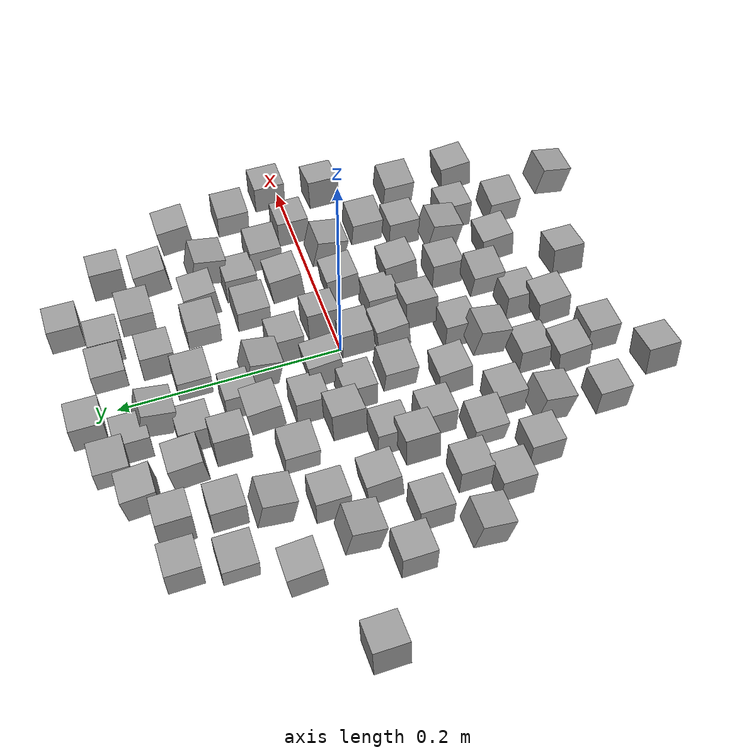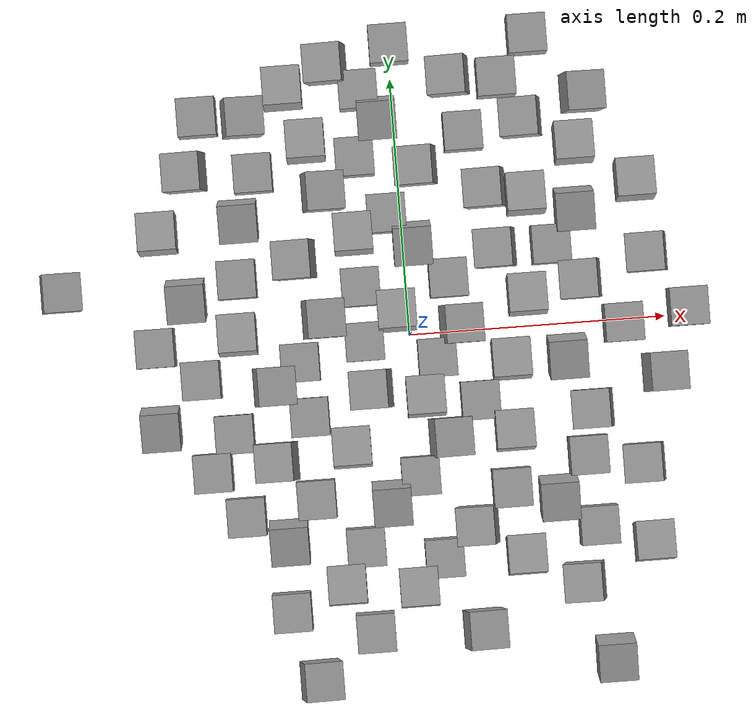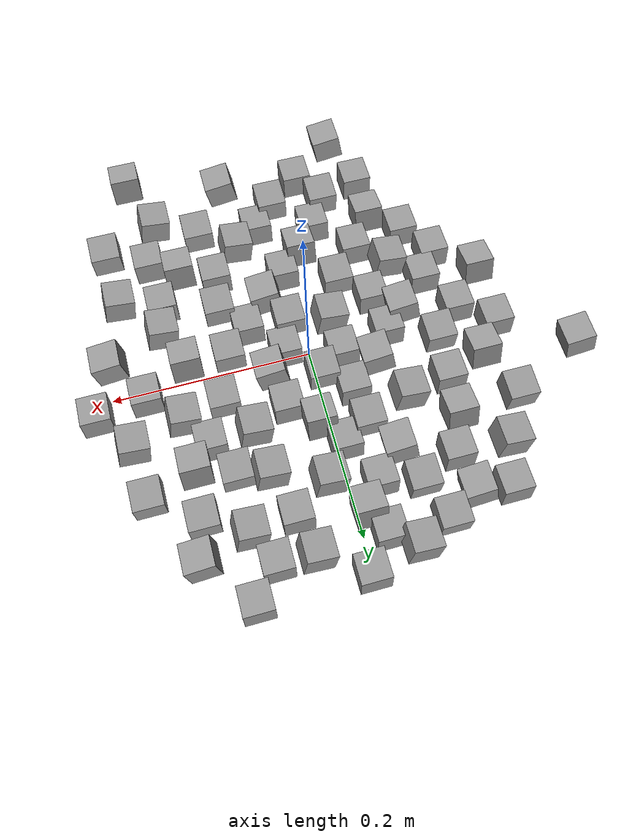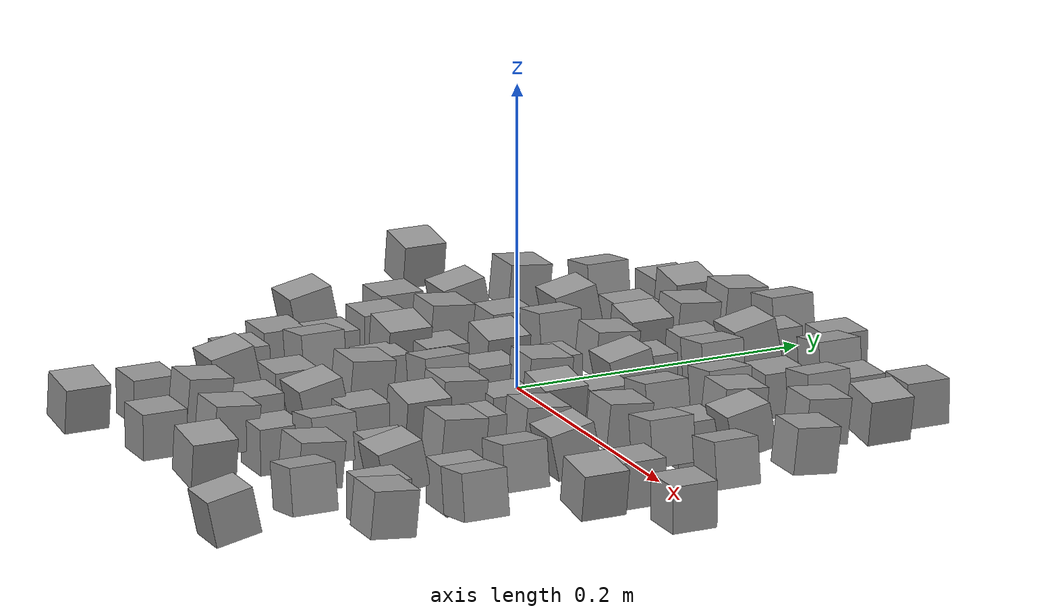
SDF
<?xml version='1.0'?>
<sdf version='1.7'>
  <model name='stone_road'>
    <link name='link_0'>
      <inertial>
        <mass>1</mass>
        <inertia>
          <ixx>0.166667</ixx>
          <ixy>0</ixy>
          <ixz>0</ixz>
          <iyy>0.166667</iyy>
          <iyz>0</iyz>
          <izz>0.166667</izz>
        </inertia>
        <pose>0 0 0 0 -0 0</pose>
      </inertial>
      <pose>-0.171827 0.03973 0.003778 0.2 -0 0</pose>
      <gravity>1</gravity>
      <self_collide>0</self_collide>
      <kinematic>1</kinematic>
      <enable_wind>0</enable_wind>
      <visual name='visual'>
        <pose>0 0 0 0 -0 0</pose>
        <geometry>
          <box>
            <size>0.03 0.03 0.03</size>
          </box>
        </geometry>
        <material>
          <lighting>1</lighting>
          <script>
            <uri>file://media/materials/scripts/gazebo.material</uri>
            <name>Gazebo/Grey</name>
          </script>
          <shader type='pixel'>
            <normal_map>__default__</normal_map>
          </shader>
          <ambient>0.3 0.3 0.3 1</ambient>
          <diffuse>0.7 0.7 0.7 1</diffuse>
          <specular>0.01 0.01 0.01 1</specular>
          <emissive>0 0 0 1</emissive>
        </material>
        <transparency>0</transparency>
        <cast_shadows>1</cast_shadows>
      </visual>
      <collision name='collision'>
        <laser_retro>0</laser_retro>
        <max_contacts>10</max_contacts>
        <pose>0 0 0 0 -0 0</pose>
        <geometry>
          <box>
            <size>0.03 0.03 0.03</size>
          </box>
        </geometry>
        <surface>
          <friction>
            <ode>
              <mu>1</mu>
              <mu2>1</mu2>
              <fdir1>0 0 0</fdir1>
              <slip1>0</slip1>
              <slip2>0</slip2>
            </ode>
            <torsional>
              <coefficient>1</coefficient>
              <patch_radius>0</patch_radius>
              <surface_radius>0</surface_radius>
              <use_patch_radius>1</use_patch_radius>
              <ode>
                <slip>0</slip>
              </ode>
            </torsional>
          </friction>
          <bounce>
            <restitution_coefficient>0</restitution_coefficient>
            <threshold>1e+06</threshold>
          </bounce>
          <contact>
            <collide_without_contact>0</collide_without_contact>
            <collide_without_contact_bitmask>1</collide_without_contact_bitmask>
            <collide_bitmask>1</collide_bitmask>
            <ode>
              <soft_cfm>0</soft_cfm>
              <soft_erp>0.2</soft_erp>
              <kp>1e+13</kp>
              <kd>1</kd>
              <max_vel>0.01</max_vel>
              <min_depth>0</min_depth>
            </ode>
            <bullet>
              <split_impulse>1</split_impulse>
              <split_impulse_penetration_threshold>-0.01</split_impulse_penetration_threshold>
              <soft_cfm>0</soft_cfm>
              <soft_erp>0.2</soft_erp>
              <kp>1e+13</kp>
              <kd>1</kd>
            </bullet>
          </contact>
        </surface>
      </collision>
    </link>
    <link name='link_0_clone_0'>
      <inertial>
        <mass>1</mass>
        <inertia>
          <ixx>0.166667</ixx>
          <ixy>0</ixy>
          <ixz>0</ixz>
          <iyy>0.166667</iyy>
          <iyz>0</iyz>
          <izz>0.166667</izz>
        </inertia>
        <pose>0 0 0 0 -0 0</pose>
      </inertial>
      <pose>-0.104982 -0.15412 0.003778 0.2 -0 0</pose>
      <gravity>1</gravity>
      <self_collide>0</self_collide>
      <kinematic>1</kinematic>
      <enable_wind>0</enable_wind>
      <visual name='visual'>
        <pose>0 0 0 0 -0 0</pose>
        <geometry>
          <box>
            <size>0.03 0.03 0.03</size>
          </box>
        </geometry>
        <material>
          <lighting>1</lighting>
          <script>
            <uri>file://media/materials/scripts/gazebo.material</uri>
            <name>Gazebo/Grey</name>
          </script>
          <shader type='pixel'>
            <normal_map>__default__</normal_map>
          </shader>
          <ambient>0.3 0.3 0.3 1</ambient>
          <diffuse>0.7 0.7 0.7 1</diffuse>
          <specular>0.01 0.01 0.01 1</specular>
          <emissive>0 0 0 1</emissive>
        </material>
        <transparency>0</transparency>
        <cast_shadows>1</cast_shadows>
      </visual>
      <collision name='collision'>
        <laser_retro>0</laser_retro>
        <max_contacts>10</max_contacts>
        <pose>0 0 0 0 -0 0</pose>
        <geometry>
          <box>
            <size>0.03 0.03 0.03</size>
          </box>
        </geometry>
        <surface>
          <friction>
            <ode>
              <mu>1</mu>
              <mu2>1</mu2>
              <fdir1>0 0 0</fdir1>
              <slip1>0</slip1>
              <slip2>0</slip2>
            </ode>
            <torsional>
              <coefficient>1</coefficient>
              <patch_radius>0</patch_radius>
              <surface_radius>0</surface_radius>
              <use_patch_radius>1</use_patch_radius>
              <ode>
                <slip>0</slip>
              </ode>
            </torsional>
          </friction>
          <bounce>
            <restitution_coefficient>0</restitution_coefficient>
            <threshold>1e+06</threshold>
          </bounce>
          <contact>
            <collide_without_contact>0</collide_without_contact>
            <collide_without_contact_bitmask>1</collide_without_contact_bitmask>
            <collide_bitmask>1</collide_bitmask>
            <ode>
              <soft_cfm>0</soft_cfm>
              <soft_erp>0.2</soft_erp>
              <kp>1e+13</kp>
              <kd>1</kd>
              <max_vel>0.01</max_vel>
              <min_depth>0</min_depth>
            </ode>
            <bullet>
              <split_impulse>1</split_impulse>
              <split_impulse_penetration_threshold>-0.01</split_impulse_penetration_threshold>
              <soft_cfm>0</soft_cfm>
              <soft_erp>0.2</soft_erp>
              <kp>1e+13</kp>
              <kd>1</kd>
            </bullet>
          </contact>
        </surface>
      </collision>
    </link>
    <link name='link_0_clone_1'>
      <inertial>
        <mass>1</mass>
        <inertia>
          <ixx>0.166667</ixx>
          <ixy>0</ixy>
          <ixz>0</ixz>
          <iyy>0.166667</iyy>
          <iyz>0</iyz>
          <izz>0.166667</izz>
        </inertia>
        <pose>0 0 0 0 -0 0</pose>
      </inertial>
      <pose>-0.022921 -0.129606 0.003778 0.2 -0 0</pose>
      <gravity>1</gravity>
      <self_collide>0</self_collide>
      <kinematic>1</kinematic>
      <enable_wind>0</enable_wind>
      <visual name='visual'>
        <pose>0 0 0 0 -0 0</pose>
        <geometry>
          <box>
            <size>0.03 0.03 0.03</size>
          </box>
        </geometry>
        <material>
          <lighting>1</lighting>
          <script>
            <uri>file://media/materials/scripts/gazebo.material</uri>
            <name>Gazebo/Grey</name>
          </script>
          <shader type='pixel'>
            <normal_map>__default__</normal_map>
          </shader>
          <ambient>0.3 0.3 0.3 1</ambient>
          <diffuse>0.7 0.7 0.7 1</diffuse>
          <specular>0.01 0.01 0.01 1</specular>
          <emissive>0 0 0 1</emissive>
        </material>
        <transparency>0</transparency>
        <cast_shadows>1</cast_shadows>
      </visual>
      <collision name='collision'>
        <laser_retro>0</laser_retro>
        <max_contacts>10</max_contacts>
        <pose>0 0 0 0 -0 0</pose>
        <geometry>
          <box>
            <size>0.03 0.03 0.03</size>
          </box>
        </geometry>
        <surface>
          <friction>
            <ode>
              <mu>1</mu>
              <mu2>1</mu2>
              <fdir1>0 0 0</fdir1>
              <slip1>0</slip1>
              <slip2>0</slip2>
            </ode>
            <torsional>
              <coefficient>1</coefficient>
              <patch_radius>0</patch_radius>
              <surface_radius>0</surface_radius>
              <use_patch_radius>1</use_patch_radius>
              <ode>
                <slip>0</slip>
              </ode>
            </torsional>
          </friction>
          <bounce>
            <restitution_coefficient>0</restitution_coefficient>
            <threshold>1e+06</threshold>
          </bounce>
          <contact>
            <collide_without_contact>0</collide_without_contact>
            <collide_without_contact_bitmask>1</collide_without_contact_bitmask>
            <collide_bitmask>1</collide_bitmask>
            <ode>
              <soft_cfm>0</soft_cfm>
              <soft_erp>0.2</soft_erp>
              <kp>1e+13</kp>
              <kd>1</kd>
              <max_vel>0.01</max_vel>
              <min_depth>0</min_depth>
            </ode>
            <bullet>
              <split_impulse>1</split_impulse>
              <split_impulse_penetration_threshold>-0.01</split_impulse_penetration_threshold>
              <soft_cfm>0</soft_cfm>
              <soft_erp>0.2</soft_erp>
              <kp>1e+13</kp>
              <kd>1</kd>
            </bullet>
          </contact>
        </surface>
      </collision>
    </link>
    <link name='link_0_clone_10'>
      <inertial>
        <mass>1</mass>
        <inertia>
          <ixx>0.166667</ixx>
          <ixy>0</ixy>
          <ixz>0</ixz>
          <iyy>0.166667</iyy>
          <iyz>0</iyz>
          <izz>0.166667</izz>
        </inertia>
        <pose>0 0 0 0 -0 0</pose>
      </inertial>
      <pose>-0.01295 0.17123 0.003778 0.2 -0 0</pose>
      <gravity>1</gravity>
      <self_collide>0</self_collide>
      <kinematic>1</kinematic>
      <enable_wind>0</enable_wind>
      <visual name='visual'>
        <pose>0 0 0 0 -0 0</pose>
        <geometry>
          <box>
            <size>0.03 0.03 0.03</size>
          </box>
        </geometry>
        <material>
          <lighting>1</lighting>
          <script>
            <uri>file://media/materials/scripts/gazebo.material</uri>
            <name>Gazebo/Grey</name>
          </script>
          <shader type='pixel'>
            <normal_map>__default__</normal_map>
          </shader>
          <ambient>0.3 0.3 0.3 1</ambient>
          <diffuse>0.7 0.7 0.7 1</diffuse>
          <specular>0.01 0.01 0.01 1</specular>
          <emissive>0 0 0 1</emissive>
        </material>
        <transparency>0</transparency>
        <cast_shadows>1</cast_shadows>
      </visual>
      <collision name='collision'>
        <laser_retro>0</laser_retro>
        <max_contacts>10</max_contacts>
        <pose>0 0 0 0 -0 0</pose>
        <geometry>
          <box>
            <size>0.03 0.03 0.03</size>
          </box>
        </geometry>
        <surface>
          <friction>
            <ode>
              <mu>1</mu>
              <mu2>1</mu2>
              <fdir1>0 0 0</fdir1>
              <slip1>0</slip1>
              <slip2>0</slip2>
            </ode>
            <torsional>
              <coefficient>1</coefficient>
              <patch_radius>0</patch_radius>
              <surface_radius>0</surface_radius>
              <use_patch_radius>1</use_patch_radius>
              <ode>
                <slip>0</slip>
              </ode>
            </torsional>
          </friction>
          <bounce>
            <restitution_coefficient>0</restitution_coefficient>
            <threshold>1e+06</threshold>
          </bounce>
          <contact>
            <collide_without_contact>0</collide_without_contact>
            <collide_without_contact_bitmask>1</collide_without_contact_bitmask>
            <collide_bitmask>1</collide_bitmask>
            <ode>
              <soft_cfm>0</soft_cfm>
              <soft_erp>0.2</soft_erp>
              <kp>1e+13</kp>
              <kd>1</kd>
              <max_vel>0.01</max_vel>
              <min_depth>0</min_depth>
            </ode>
            <bullet>
              <split_impulse>1</split_impulse>
              <split_impulse_penetration_threshold>-0.01</split_impulse_penetration_threshold>
              <soft_cfm>0</soft_cfm>
              <soft_erp>0.2</soft_erp>
              <kp>1e+13</kp>
              <kd>1</kd>
            </bullet>
          </contact>
        </surface>
      </collision>
    </link>
    <link name='link_0_clone_11'>
      <inertial>
        <mass>1</mass>
        <inertia>
          <ixx>0.166667</ixx>
          <ixy>0</ixy>
          <ixz>0</ixz>
          <iyy>0.166667</iyy>
          <iyz>0</iyz>
          <izz>0.166667</izz>
        </inertia>
        <pose>0 0 0 0 -0 0</pose>
      </inertial>
      <pose>0.007758 0.071496 0.003778 0.2 -0 0</pose>
      <gravity>1</gravity>
      <self_collide>0</self_collide>
      <kinematic>1</kinematic>
      <enable_wind>0</enable_wind>
      <visual name='visual'>
        <pose>0 0 0 0 -0 0</pose>
        <geometry>
          <box>
            <size>0.03 0.03 0.03</size>
          </box>
        </geometry>
        <material>
          <lighting>1</lighting>
          <script>
            <uri>file://media/materials/scripts/gazebo.material</uri>
            <name>Gazebo/Grey</name>
          </script>
          <shader type='pixel'>
            <normal_map>__default__</normal_map>
          </shader>
          <ambient>0.3 0.3 0.3 1</ambient>
          <diffuse>0.7 0.7 0.7 1</diffuse>
          <specular>0.01 0.01 0.01 1</specular>
          <emissive>0 0 0 1</emissive>
        </material>
        <transparency>0</transparency>
        <cast_shadows>1</cast_shadows>
      </visual>
      <collision name='collision'>
        <laser_retro>0</laser_retro>
        <max_contacts>10</max_contacts>
        <pose>0 0 0 0 -0 0</pose>
        <geometry>
          <box>
            <size>0.03 0.03 0.03</size>
          </box>
        </geometry>
        <surface>
          <friction>
            <ode>
              <mu>1</mu>
              <mu2>1</mu2>
              <fdir1>0 0 0</fdir1>
              <slip1>0</slip1>
              <slip2>0</slip2>
            </ode>
            <torsional>
              <coefficient>1</coefficient>
              <patch_radius>0</patch_radius>
              <surface_radius>0</surface_radius>
              <use_patch_radius>1</use_patch_radius>
              <ode>
                <slip>0</slip>
              </ode>
            </torsional>
          </friction>
          <bounce>
            <restitution_coefficient>0</restitution_coefficient>
            <threshold>1e+06</threshold>
          </bounce>
          <contact>
            <collide_without_contact>0</collide_without_contact>
            <collide_without_contact_bitmask>1</collide_without_contact_bitmask>
            <collide_bitmask>1</collide_bitmask>
            <ode>
              <soft_cfm>0</soft_cfm>
              <soft_erp>0.2</soft_erp>
              <kp>1e+13</kp>
              <kd>1</kd>
              <max_vel>0.01</max_vel>
              <min_depth>0</min_depth>
            </ode>
            <bullet>
              <split_impulse>1</split_impulse>
              <split_impulse_penetration_threshold>-0.01</split_impulse_penetration_threshold>
              <soft_cfm>0</soft_cfm>
              <soft_erp>0.2</soft_erp>
              <kp>1e+13</kp>
              <kd>1</kd>
            </bullet>
          </contact>
        </surface>
      </collision>
    </link>
    <link name='link_0_clone_12'>
      <inertial>
        <mass>1</mass>
        <inertia>
          <ixx>0.166667</ixx>
          <ixy>0</ixy>
          <ixz>0</ixz>
          <iyy>0.166667</iyy>
          <iyz>0</iyz>
          <izz>0.166667</izz>
        </inertia>
        <pose>0 0 0 0 -0 0</pose>
      </inertial>
      <pose>0.142624 -0.262715 0.003778 0.2 -0 0</pose>
      <gravity>1</gravity>
      <self_collide>0</self_collide>
      <kinematic>1</kinematic>
      <enable_wind>0</enable_wind>
      <visual name='visual'>
        <pose>0 0 0 0 -0 0</pose>
        <geometry>
          <box>
            <size>0.03 0.03 0.03</size>
          </box>
        </geometry>
        <material>
          <lighting>1</lighting>
          <script>
            <uri>file://media/materials/scripts/gazebo.material</uri>
            <name>Gazebo/Grey</name>
          </script>
          <shader type='pixel'>
            <normal_map>__default__</normal_map>
          </shader>
          <ambient>0.3 0.3 0.3 1</ambient>
          <diffuse>0.7 0.7 0.7 1</diffuse>
          <specular>0.01 0.01 0.01 1</specular>
          <emissive>0 0 0 1</emissive>
        </material>
        <transparency>0</transparency>
        <cast_shadows>1</cast_shadows>
      </visual>
      <collision name='collision'>
        <laser_retro>0</laser_retro>
        <max_contacts>10</max_contacts>
        <pose>0 0 0 0 -0 0</pose>
        <geometry>
          <box>
            <size>0.03 0.03 0.03</size>
          </box>
        </geometry>
        <surface>
          <friction>
            <ode>
              <mu>1</mu>
              <mu2>1</mu2>
              <fdir1>0 0 0</fdir1>
              <slip1>0</slip1>
              <slip2>0</slip2>
            </ode>
            <torsional>
              <coefficient>1</coefficient>
              <patch_radius>0</patch_radius>
              <surface_radius>0</surface_radius>
              <use_patch_radius>1</use_patch_radius>
              <ode>
                <slip>0</slip>
              </ode>
            </torsional>
          </friction>
          <bounce>
            <restitution_coefficient>0</restitution_coefficient>
            <threshold>1e+06</threshold>
          </bounce>
          <contact>
            <collide_without_contact>0</collide_without_contact>
            <collide_without_contact_bitmask>1</collide_without_contact_bitmask>
            <collide_bitmask>1</collide_bitmask>
            <ode>
              <soft_cfm>0</soft_cfm>
              <soft_erp>0.2</soft_erp>
              <kp>1e+13</kp>
              <kd>1</kd>
              <max_vel>0.01</max_vel>
              <min_depth>0</min_depth>
            </ode>
            <bullet>
              <split_impulse>1</split_impulse>
              <split_impulse_penetration_threshold>-0.01</split_impulse_penetration_threshold>
              <soft_cfm>0</soft_cfm>
              <soft_erp>0.2</soft_erp>
              <kp>1e+13</kp>
              <kd>1</kd>
            </bullet>
          </contact>
        </surface>
      </collision>
    </link>
    <link name='link_0_clone_13'>
      <inertial>
        <mass>1</mass>
        <inertia>
          <ixx>0.166667</ixx>
          <ixy>0</ixy>
          <ixz>0</ixz>
          <iyy>0.166667</iyy>
          <iyz>0</iyz>
          <izz>0.166667</izz>
        </inertia>
        <pose>0 0 0 0 -0 0</pose>
      </inertial>
      <pose>0.107601 -0.134881 0.003778 0.2 -0 0</pose>
      <gravity>1</gravity>
      <self_collide>0</self_collide>
      <kinematic>1</kinematic>
      <enable_wind>0</enable_wind>
      <visual name='visual'>
        <pose>0 0 0 0 -0 0</pose>
        <geometry>
          <box>
            <size>0.03 0.03 0.03</size>
          </box>
        </geometry>
        <material>
          <lighting>1</lighting>
          <script>
            <uri>file://media/materials/scripts/gazebo.material</uri>
            <name>Gazebo/Grey</name>
          </script>
          <shader type='pixel'>
            <normal_map>__default__</normal_map>
          </shader>
          <ambient>0.3 0.3 0.3 1</ambient>
          <diffuse>0.7 0.7 0.7 1</diffuse>
          <specular>0.01 0.01 0.01 1</specular>
          <emissive>0 0 0 1</emissive>
        </material>
        <transparency>0</transparency>
        <cast_shadows>1</cast_shadows>
      </visual>
      <collision name='collision'>
        <laser_retro>0</laser_retro>
        <max_contacts>10</max_contacts>
        <pose>0 0 0 0 -0 0</pose>
        <geometry>
          <box>
            <size>0.03 0.03 0.03</size>
          </box>
        </geometry>
        <surface>
          <friction>
            <ode>
              <mu>1</mu>
              <mu2>1</mu2>
              <fdir1>0 0 0</fdir1>
              <slip1>0</slip1>
              <slip2>0</slip2>
            </ode>
            <torsional>
              <coefficient>1</coefficient>
              <patch_radius>0</patch_radius>
              <surface_radius>0</surface_radius>
              <use_patch_radius>1</use_patch_radius>
              <ode>
                <slip>0</slip>
              </ode>
            </torsional>
          </friction>
          <bounce>
            <restitution_coefficient>0</restitution_coefficient>
            <threshold>1e+06</threshold>
          </bounce>
          <contact>
            <collide_without_contact>0</collide_without_contact>
            <collide_without_contact_bitmask>1</collide_without_contact_bitmask>
            <collide_bitmask>1</collide_bitmask>
            <ode>
              <soft_cfm>0</soft_cfm>
              <soft_erp>0.2</soft_erp>
              <kp>1e+13</kp>
              <kd>1</kd>
              <max_vel>0.01</max_vel>
              <min_depth>0</min_depth>
            </ode>
            <bullet>
              <split_impulse>1</split_impulse>
              <split_impulse_penetration_threshold>-0.01</split_impulse_penetration_threshold>
              <soft_cfm>0</soft_cfm>
              <soft_erp>0.2</soft_erp>
              <kp>1e+13</kp>
              <kd>1</kd>
            </bullet>
          </contact>
        </surface>
      </collision>
    </link>
    <link name='link_0_clone_2'>
      <inertial>
        <mass>1</mass>
        <inertia>
          <ixx>0.166667</ixx>
          <ixy>0</ixy>
          <ixz>0</ixz>
          <iyy>0.166667</iyy>
          <iyz>0</iyz>
          <izz>0.166667</izz>
        </inertia>
        <pose>0 0 0 0 -0 0</pose>
      </inertial>
      <pose>-0.065685 0.018139 0.003778 0 0.15 0</pose>
      <gravity>1</gravity>
      <self_collide>0</self_collide>
      <kinematic>1</kinematic>
      <enable_wind>0</enable_wind>
      <visual name='visual'>
        <pose>0 0 0 0 -0 0</pose>
        <geometry>
          <box>
            <size>0.03 0.03 0.03</size>
          </box>
        </geometry>
        <material>
          <lighting>1</lighting>
          <script>
            <uri>file://media/materials/scripts/gazebo.material</uri>
            <name>Gazebo/Grey</name>
          </script>
          <shader type='pixel'>
            <normal_map>__default__</normal_map>
          </shader>
          <ambient>0.3 0.3 0.3 1</ambient>
          <diffuse>0.7 0.7 0.7 1</diffuse>
          <specular>0.01 0.01 0.01 1</specular>
          <emissive>0 0 0 1</emissive>
        </material>
        <transparency>0</transparency>
        <cast_shadows>1</cast_shadows>
      </visual>
      <collision name='collision'>
        <laser_retro>0</laser_retro>
        <max_contacts>10</max_contacts>
        <pose>0 0 0 0 -0 0</pose>
        <geometry>
          <box>
            <size>0.03 0.03 0.03</size>
          </box>
        </geometry>
        <surface>
          <friction>
            <ode>
              <mu>1</mu>
              <mu2>1</mu2>
              <fdir1>0 0 0</fdir1>
              <slip1>0</slip1>
              <slip2>0</slip2>
            </ode>
            <torsional>
              <coefficient>1</coefficient>
              <patch_radius>0</patch_radius>
              <surface_radius>0</surface_radius>
              <use_patch_radius>1</use_patch_radius>
              <ode>
                <slip>0</slip>
              </ode>
            </torsional>
          </friction>
          <bounce>
            <restitution_coefficient>0</restitution_coefficient>
            <threshold>1e+06</threshold>
          </bounce>
          <contact>
            <collide_without_contact>0</collide_without_contact>
            <collide_without_contact_bitmask>1</collide_without_contact_bitmask>
            <collide_bitmask>1</collide_bitmask>
            <ode>
              <soft_cfm>0</soft_cfm>
              <soft_erp>0.2</soft_erp>
              <kp>1e+13</kp>
              <kd>1</kd>
              <max_vel>0.01</max_vel>
              <min_depth>0</min_depth>
            </ode>
            <bullet>
              <split_impulse>1</split_impulse>
              <split_impulse_penetration_threshold>-0.01</split_impulse_penetration_threshold>
              <soft_cfm>0</soft_cfm>
              <soft_erp>0.2</soft_erp>
              <kp>1e+13</kp>
              <kd>1</kd>
            </bullet>
          </contact>
        </surface>
      </collision>
    </link>
    <link name='link_0_clone_2_clone'>
      <inertial>
        <mass>1</mass>
        <inertia>
          <ixx>0.166667</ixx>
          <ixy>0</ixy>
          <ixz>0</ixz>
          <iyy>0.166667</iyy>
          <iyz>0</iyz>
          <izz>0.166667</izz>
        </inertia>
        <pose>0 0 0 0 -0 0</pose>
      </inertial>
      <pose>-0.10771 -0.03187 0.003778 0 0.15 0</pose>
      <gravity>1</gravity>
      <self_collide>0</self_collide>
      <kinematic>1</kinematic>
      <enable_wind>0</enable_wind>
      <visual name='visual'>
        <pose>0 0 0 0 -0 0</pose>
        <geometry>
          <box>
            <size>0.03 0.03 0.03</size>
          </box>
        </geometry>
        <material>
          <lighting>1</lighting>
          <script>
            <uri>file://media/materials/scripts/gazebo.material</uri>
            <name>Gazebo/Grey</name>
          </script>
          <shader type='pixel'>
            <normal_map>__default__</normal_map>
          </shader>
          <ambient>0.3 0.3 0.3 1</ambient>
          <diffuse>0.7 0.7 0.7 1</diffuse>
          <specular>0.01 0.01 0.01 1</specular>
          <emissive>0 0 0 1</emissive>
        </material>
        <transparency>0</transparency>
        <cast_shadows>1</cast_shadows>
      </visual>
      <collision name='collision'>
        <laser_retro>0</laser_retro>
        <max_contacts>10</max_contacts>
        <pose>0 0 0 0 -0 0</pose>
        <geometry>
          <box>
            <size>0.03 0.03 0.03</size>
          </box>
        </geometry>
        <surface>
          <friction>
            <ode>
              <mu>1</mu>
              <mu2>1</mu2>
              <fdir1>0 0 0</fdir1>
              <slip1>0</slip1>
              <slip2>0</slip2>
            </ode>
            <torsional>
              <coefficient>1</coefficient>
              <patch_radius>0</patch_radius>
              <surface_radius>0</surface_radius>
              <use_patch_radius>1</use_patch_radius>
              <ode>
                <slip>0</slip>
              </ode>
            </torsional>
          </friction>
          <bounce>
            <restitution_coefficient>0</restitution_coefficient>
            <threshold>1e+06</threshold>
          </bounce>
          <contact>
            <collide_without_contact>0</collide_without_contact>
            <collide_without_contact_bitmask>1</collide_without_contact_bitmask>
            <collide_bitmask>1</collide_bitmask>
            <ode>
              <soft_cfm>0</soft_cfm>
              <soft_erp>0.2</soft_erp>
              <kp>1e+13</kp>
              <kd>1</kd>
              <max_vel>0.01</max_vel>
              <min_depth>0</min_depth>
            </ode>
            <bullet>
              <split_impulse>1</split_impulse>
              <split_impulse_penetration_threshold>-0.01</split_impulse_penetration_threshold>
              <soft_cfm>0</soft_cfm>
              <soft_erp>0.2</soft_erp>
              <kp>1e+13</kp>
              <kd>1</kd>
            </bullet>
          </contact>
        </surface>
      </collision>
    </link>
    <link name='link_0_clone_2_clone_0'>
      <inertial>
        <mass>1</mass>
        <inertia>
          <ixx>0.166667</ixx>
          <ixy>0</ixy>
          <ixz>0</ixz>
          <iyy>0.166667</iyy>
          <iyz>0</iyz>
          <izz>0.166667</izz>
        </inertia>
        <pose>0 0 0 0 -0 0</pose>
      </inertial>
      <pose>0.026852 -0.0813 0.003778 0 0.15 0</pose>
      <gravity>1</gravity>
      <self_collide>0</self_collide>
      <kinematic>1</kinematic>
      <enable_wind>0</enable_wind>
      <visual name='visual'>
        <pose>0 0 0 0 -0 0</pose>
        <geometry>
          <box>
            <size>0.03 0.03 0.03</size>
          </box>
        </geometry>
        <material>
          <lighting>1</lighting>
          <script>
            <uri>file://media/materials/scripts/gazebo.material</uri>
            <name>Gazebo/Grey</name>
          </script>
          <shader type='pixel'>
            <normal_map>__default__</normal_map>
          </shader>
          <ambient>0.3 0.3 0.3 1</ambient>
          <diffuse>0.7 0.7 0.7 1</diffuse>
          <specular>0.01 0.01 0.01 1</specular>
          <emissive>0 0 0 1</emissive>
        </material>
        <transparency>0</transparency>
        <cast_shadows>1</cast_shadows>
      </visual>
      <collision name='collision'>
        <laser_retro>0</laser_retro>
        <max_contacts>10</max_contacts>
        <pose>0 0 0 0 -0 0</pose>
        <geometry>
          <box>
            <size>0.03 0.03 0.03</size>
          </box>
        </geometry>
        <surface>
          <friction>
            <ode>
              <mu>1</mu>
              <mu2>1</mu2>
              <fdir1>0 0 0</fdir1>
              <slip1>0</slip1>
              <slip2>0</slip2>
            </ode>
            <torsional>
              <coefficient>1</coefficient>
              <patch_radius>0</patch_radius>
              <surface_radius>0</surface_radius>
              <use_patch_radius>1</use_patch_radius>
              <ode>
                <slip>0</slip>
              </ode>
            </torsional>
          </friction>
          <bounce>
            <restitution_coefficient>0</restitution_coefficient>
            <threshold>1e+06</threshold>
          </bounce>
          <contact>
            <collide_without_contact>0</collide_without_contact>
            <collide_without_contact_bitmask>1</collide_without_contact_bitmask>
            <collide_bitmask>1</collide_bitmask>
            <ode>
              <soft_cfm>0</soft_cfm>
              <soft_erp>0.2</soft_erp>
              <kp>1e+13</kp>
              <kd>1</kd>
              <max_vel>0.01</max_vel>
              <min_depth>0</min_depth>
            </ode>
            <bullet>
              <split_impulse>1</split_impulse>
              <split_impulse_penetration_threshold>-0.01</split_impulse_penetration_threshold>
              <soft_cfm>0</soft_cfm>
              <soft_erp>0.2</soft_erp>
              <kp>1e+13</kp>
              <kd>1</kd>
            </bullet>
          </contact>
        </surface>
      </collision>
    </link>
    <link name='link_0_clone_2_clone_1'>
      <inertial>
        <mass>1</mass>
        <inertia>
          <ixx>0.166667</ixx>
          <ixy>0</ixy>
          <ixz>0</ixz>
          <iyy>0.166667</iyy>
          <iyz>0</iyz>
          <izz>0.166667</izz>
        </inertia>
        <pose>0 0 0 0 -0 0</pose>
      </inertial>
      <pose>0.041447 0.006316 0.003778 0 0.15 0</pose>
      <gravity>1</gravity>
      <self_collide>0</self_collide>
      <kinematic>1</kinematic>
      <enable_wind>0</enable_wind>
      <visual name='visual'>
        <pose>0 0 0 0 -0 0</pose>
        <geometry>
          <box>
            <size>0.03 0.03 0.03</size>
          </box>
        </geometry>
        <material>
          <lighting>1</lighting>
          <script>
            <uri>file://media/materials/scripts/gazebo.material</uri>
            <name>Gazebo/Grey</name>
          </script>
          <shader type='pixel'>
            <normal_map>__default__</normal_map>
          </shader>
          <ambient>0.3 0.3 0.3 1</ambient>
          <diffuse>0.7 0.7 0.7 1</diffuse>
          <specular>0.01 0.01 0.01 1</specular>
          <emissive>0 0 0 1</emissive>
        </material>
        <transparency>0</transparency>
        <cast_shadows>1</cast_shadows>
      </visual>
      <collision name='collision'>
        <laser_retro>0</laser_retro>
        <max_contacts>10</max_contacts>
        <pose>0 0 0 0 -0 0</pose>
        <geometry>
          <box>
            <size>0.03 0.03 0.03</size>
          </box>
        </geometry>
        <surface>
          <friction>
            <ode>
              <mu>1</mu>
              <mu2>1</mu2>
              <fdir1>0 0 0</fdir1>
              <slip1>0</slip1>
              <slip2>0</slip2>
            </ode>
            <torsional>
              <coefficient>1</coefficient>
              <patch_radius>0</patch_radius>
              <surface_radius>0</surface_radius>
              <use_patch_radius>1</use_patch_radius>
              <ode>
                <slip>0</slip>
              </ode>
            </torsional>
          </friction>
          <bounce>
            <restitution_coefficient>0</restitution_coefficient>
            <threshold>1e+06</threshold>
          </bounce>
          <contact>
            <collide_without_contact>0</collide_without_contact>
            <collide_without_contact_bitmask>1</collide_without_contact_bitmask>
            <collide_bitmask>1</collide_bitmask>
            <ode>
              <soft_cfm>0</soft_cfm>
              <soft_erp>0.2</soft_erp>
              <kp>1e+13</kp>
              <kd>1</kd>
              <max_vel>0.01</max_vel>
              <min_depth>0</min_depth>
            </ode>
            <bullet>
              <split_impulse>1</split_impulse>
              <split_impulse_penetration_threshold>-0.01</split_impulse_penetration_threshold>
              <soft_cfm>0</soft_cfm>
              <soft_erp>0.2</soft_erp>
              <kp>1e+13</kp>
              <kd>1</kd>
            </bullet>
          </contact>
        </surface>
      </collision>
    </link>
    <link name='link_0_clone_2_clone_2'>
      <inertial>
        <mass>1</mass>
        <inertia>
          <ixx>0.166667</ixx>
          <ixy>0</ixy>
          <ixz>0</ixz>
          <iyy>0.166667</iyy>
          <iyz>0</iyz>
          <izz>0.166667</izz>
        </inertia>
        <pose>0 0 0 0 -0 0</pose>
      </inertial>
      <pose>0.066563 0.110568 0.003778 0 -0.15 0</pose>
      <gravity>1</gravity>
      <self_collide>0</self_collide>
      <kinematic>1</kinematic>
      <enable_wind>0</enable_wind>
      <visual name='visual'>
        <pose>0 0 0 0 -0 0</pose>
        <geometry>
          <box>
            <size>0.03 0.03 0.03</size>
          </box>
        </geometry>
        <material>
          <lighting>1</lighting>
          <script>
            <uri>file://media/materials/scripts/gazebo.material</uri>
            <name>Gazebo/Grey</name>
          </script>
          <shader type='pixel'>
            <normal_map>__default__</normal_map>
          </shader>
          <ambient>0.3 0.3 0.3 1</ambient>
          <diffuse>0.7 0.7 0.7 1</diffuse>
          <specular>0.01 0.01 0.01 1</specular>
          <emissive>0 0 0 1</emissive>
        </material>
        <transparency>0</transparency>
        <cast_shadows>1</cast_shadows>
      </visual>
      <collision name='collision'>
        <laser_retro>0</laser_retro>
        <max_contacts>10</max_contacts>
        <pose>0 0 0 0 -0 0</pose>
        <geometry>
          <box>
            <size>0.03 0.03 0.03</size>
          </box>
        </geometry>
        <surface>
          <friction>
            <ode>
              <mu>1</mu>
              <mu2>1</mu2>
              <fdir1>0 0 0</fdir1>
              <slip1>0</slip1>
              <slip2>0</slip2>
            </ode>
            <torsional>
              <coefficient>1</coefficient>
              <patch_radius>0</patch_radius>
              <surface_radius>0</surface_radius>
              <use_patch_radius>1</use_patch_radius>
              <ode>
                <slip>0</slip>
              </ode>
            </torsional>
          </friction>
          <bounce>
            <restitution_coefficient>0</restitution_coefficient>
            <threshold>1e+06</threshold>
          </bounce>
          <contact>
            <collide_without_contact>0</collide_without_contact>
            <collide_without_contact_bitmask>1</collide_without_contact_bitmask>
            <collide_bitmask>1</collide_bitmask>
            <ode>
              <soft_cfm>0</soft_cfm>
              <soft_erp>0.2</soft_erp>
              <kp>1e+13</kp>
              <kd>1</kd>
              <max_vel>0.01</max_vel>
              <min_depth>0</min_depth>
            </ode>
            <bullet>
              <split_impulse>1</split_impulse>
              <split_impulse_penetration_threshold>-0.01</split_impulse_penetration_threshold>
              <soft_cfm>0</soft_cfm>
              <soft_erp>0.2</soft_erp>
              <kp>1e+13</kp>
              <kd>1</kd>
            </bullet>
          </contact>
        </surface>
      </collision>
    </link>
    <link name='link_0_clone_2_clone_2_clone'>
      <inertial>
        <mass>1</mass>
        <inertia>
          <ixx>0.166667</ixx>
          <ixy>0</ixy>
          <ixz>0</ixz>
          <iyy>0.166667</iyy>
          <iyz>0</iyz>
          <izz>0.166667</izz>
        </inertia>
        <pose>0 0 0 0 -0 0</pose>
      </inertial>
      <pose>0.189059 0.051135 0.003778 0 -0.15 0</pose>
      <gravity>1</gravity>
      <self_collide>0</self_collide>
      <kinematic>1</kinematic>
      <enable_wind>0</enable_wind>
      <visual name='visual'>
        <pose>0 0 0 0 -0 0</pose>
        <geometry>
          <box>
            <size>0.03 0.03 0.03</size>
          </box>
        </geometry>
        <material>
          <lighting>1</lighting>
          <script>
            <uri>file://media/materials/scripts/gazebo.material</uri>
            <name>Gazebo/Grey</name>
          </script>
          <shader type='pixel'>
            <normal_map>__default__</normal_map>
          </shader>
          <ambient>0.3 0.3 0.3 1</ambient>
          <diffuse>0.7 0.7 0.7 1</diffuse>
          <specular>0.01 0.01 0.01 1</specular>
          <emissive>0 0 0 1</emissive>
        </material>
        <transparency>0</transparency>
        <cast_shadows>1</cast_shadows>
      </visual>
      <collision name='collision'>
        <laser_retro>0</laser_retro>
        <max_contacts>10</max_contacts>
        <pose>0 0 0 0 -0 0</pose>
        <geometry>
          <box>
            <size>0.03 0.03 0.03</size>
          </box>
        </geometry>
        <surface>
          <friction>
            <ode>
              <mu>1</mu>
              <mu2>1</mu2>
              <fdir1>0 0 0</fdir1>
              <slip1>0</slip1>
              <slip2>0</slip2>
            </ode>
            <torsional>
              <coefficient>1</coefficient>
              <patch_radius>0</patch_radius>
              <surface_radius>0</surface_radius>
              <use_patch_radius>1</use_patch_radius>
              <ode>
                <slip>0</slip>
              </ode>
            </torsional>
          </friction>
          <bounce>
            <restitution_coefficient>0</restitution_coefficient>
            <threshold>1e+06</threshold>
          </bounce>
          <contact>
            <collide_without_contact>0</collide_without_contact>
            <collide_without_contact_bitmask>1</collide_without_contact_bitmask>
            <collide_bitmask>1</collide_bitmask>
            <ode>
              <soft_cfm>0</soft_cfm>
              <soft_erp>0.2</soft_erp>
              <kp>1e+13</kp>
              <kd>1</kd>
              <max_vel>0.01</max_vel>
              <min_depth>0</min_depth>
            </ode>
            <bullet>
              <split_impulse>1</split_impulse>
              <split_impulse_penetration_threshold>-0.01</split_impulse_penetration_threshold>
              <soft_cfm>0</soft_cfm>
              <soft_erp>0.2</soft_erp>
              <kp>1e+13</kp>
              <kd>1</kd>
            </bullet>
          </contact>
        </surface>
      </collision>
    </link>
    <link name='link_0_clone_2_clone_2_clone_0'>
      <inertial>
        <mass>1</mass>
        <inertia>
          <ixx>0.166667</ixx>
          <ixy>0</ixy>
          <ixz>0</ixz>
          <iyy>0.166667</iyy>
          <iyz>0</iyz>
          <izz>0.166667</izz>
        </inertia>
        <pose>0 0 0 0 -0 0</pose>
      </inertial>
      <pose>-0.032874 -0.039714 0.003778 0 -0.15 0</pose>
      <gravity>1</gravity>
      <self_collide>0</self_collide>
      <kinematic>1</kinematic>
      <enable_wind>0</enable_wind>
      <visual name='visual'>
        <pose>0 0 0 0 -0 0</pose>
        <geometry>
          <box>
            <size>0.03 0.03 0.03</size>
          </box>
        </geometry>
        <material>
          <lighting>1</lighting>
          <script>
            <uri>file://media/materials/scripts/gazebo.material</uri>
            <name>Gazebo/Grey</name>
          </script>
          <shader type='pixel'>
            <normal_map>__default__</normal_map>
          </shader>
          <ambient>0.3 0.3 0.3 1</ambient>
          <diffuse>0.7 0.7 0.7 1</diffuse>
          <specular>0.01 0.01 0.01 1</specular>
          <emissive>0 0 0 1</emissive>
        </material>
        <transparency>0</transparency>
        <cast_shadows>1</cast_shadows>
      </visual>
      <collision name='collision'>
        <laser_retro>0</laser_retro>
        <max_contacts>10</max_contacts>
        <pose>0 0 0 0 -0 0</pose>
        <geometry>
          <box>
            <size>0.03 0.03 0.03</size>
          </box>
        </geometry>
        <surface>
          <friction>
            <ode>
              <mu>1</mu>
              <mu2>1</mu2>
              <fdir1>0 0 0</fdir1>
              <slip1>0</slip1>
              <slip2>0</slip2>
            </ode>
            <torsional>
              <coefficient>1</coefficient>
              <patch_radius>0</patch_radius>
              <surface_radius>0</surface_radius>
              <use_patch_radius>1</use_patch_radius>
              <ode>
                <slip>0</slip>
              </ode>
            </torsional>
          </friction>
          <bounce>
            <restitution_coefficient>0</restitution_coefficient>
            <threshold>1e+06</threshold>
          </bounce>
          <contact>
            <collide_without_contact>0</collide_without_contact>
            <collide_without_contact_bitmask>1</collide_without_contact_bitmask>
            <collide_bitmask>1</collide_bitmask>
            <ode>
              <soft_cfm>0</soft_cfm>
              <soft_erp>0.2</soft_erp>
              <kp>1e+13</kp>
              <kd>1</kd>
              <max_vel>0.01</max_vel>
              <min_depth>0</min_depth>
            </ode>
            <bullet>
              <split_impulse>1</split_impulse>
              <split_impulse_penetration_threshold>-0.01</split_impulse_penetration_threshold>
              <soft_cfm>0</soft_cfm>
              <soft_erp>0.2</soft_erp>
              <kp>1e+13</kp>
              <kd>1</kd>
            </bullet>
          </contact>
        </surface>
      </collision>
    </link>
    <link name='link_0_clone_2_clone_2_clone_1'>
      <inertial>
        <mass>1</mass>
        <inertia>
          <ixx>0.166667</ixx>
          <ixy>0</ixy>
          <ixz>0</ixz>
          <iyy>0.166667</iyy>
          <iyz>0</iyz>
          <izz>0.166667</izz>
        </inertia>
        <pose>0 0 0 0 -0 0</pose>
      </inertial>
      <pose>-0.085624 0.065625 0.003778 0 -0.15 0</pose>
      <gravity>1</gravity>
      <self_collide>0</self_collide>
      <kinematic>1</kinematic>
      <enable_wind>0</enable_wind>
      <visual name='visual'>
        <pose>0 0 0 0 -0 0</pose>
        <geometry>
          <box>
            <size>0.03 0.03 0.03</size>
          </box>
        </geometry>
        <material>
          <lighting>1</lighting>
          <script>
            <uri>file://media/materials/scripts/gazebo.material</uri>
            <name>Gazebo/Grey</name>
          </script>
          <shader type='pixel'>
            <normal_map>__default__</normal_map>
          </shader>
          <ambient>0.3 0.3 0.3 1</ambient>
          <diffuse>0.7 0.7 0.7 1</diffuse>
          <specular>0.01 0.01 0.01 1</specular>
          <emissive>0 0 0 1</emissive>
        </material>
        <transparency>0</transparency>
        <cast_shadows>1</cast_shadows>
      </visual>
      <collision name='collision'>
        <laser_retro>0</laser_retro>
        <max_contacts>10</max_contacts>
        <pose>0 0 0 0 -0 0</pose>
        <geometry>
          <box>
            <size>0.03 0.03 0.03</size>
          </box>
        </geometry>
        <surface>
          <friction>
            <ode>
              <mu>1</mu>
              <mu2>1</mu2>
              <fdir1>0 0 0</fdir1>
              <slip1>0</slip1>
              <slip2>0</slip2>
            </ode>
            <torsional>
              <coefficient>1</coefficient>
              <patch_radius>0</patch_radius>
              <surface_radius>0</surface_radius>
              <use_patch_radius>1</use_patch_radius>
              <ode>
                <slip>0</slip>
              </ode>
            </torsional>
          </friction>
          <bounce>
            <restitution_coefficient>0</restitution_coefficient>
            <threshold>1e+06</threshold>
          </bounce>
          <contact>
            <collide_without_contact>0</collide_without_contact>
            <collide_without_contact_bitmask>1</collide_without_contact_bitmask>
            <collide_bitmask>1</collide_bitmask>
            <ode>
              <soft_cfm>0</soft_cfm>
              <soft_erp>0.2</soft_erp>
              <kp>1e+13</kp>
              <kd>1</kd>
              <max_vel>0.01</max_vel>
              <min_depth>0</min_depth>
            </ode>
            <bullet>
              <split_impulse>1</split_impulse>
              <split_impulse_penetration_threshold>-0.01</split_impulse_penetration_threshold>
              <soft_cfm>0</soft_cfm>
              <soft_erp>0.2</soft_erp>
              <kp>1e+13</kp>
              <kd>1</kd>
            </bullet>
          </contact>
        </surface>
      </collision>
    </link>
    <link name='link_0_clone_2_clone_2_clone_10'>
      <inertial>
        <mass>1</mass>
        <inertia>
          <ixx>0.166667</ixx>
          <ixy>0</ixy>
          <ixz>0</ixz>
          <iyy>0.166667</iyy>
          <iyz>0</iyz>
          <izz>0.166667</izz>
        </inertia>
        <pose>0 0 0 0 -0 0</pose>
      </inertial>
      <pose>0.09869 0.163436 0.003778 0 -0.15 0</pose>
      <gravity>1</gravity>
      <self_collide>0</self_collide>
      <kinematic>1</kinematic>
      <enable_wind>0</enable_wind>
      <visual name='visual'>
        <pose>0 0 0 0 -0 0</pose>
        <geometry>
          <box>
            <size>0.03 0.03 0.03</size>
          </box>
        </geometry>
        <material>
          <lighting>1</lighting>
          <script>
            <uri>file://media/materials/scripts/gazebo.material</uri>
            <name>Gazebo/Grey</name>
          </script>
          <shader type='pixel'>
            <normal_map>__default__</normal_map>
          </shader>
          <ambient>0.3 0.3 0.3 1</ambient>
          <diffuse>0.7 0.7 0.7 1</diffuse>
          <specular>0.01 0.01 0.01 1</specular>
          <emissive>0 0 0 1</emissive>
        </material>
        <transparency>0</transparency>
        <cast_shadows>1</cast_shadows>
      </visual>
      <collision name='collision'>
        <laser_retro>0</laser_retro>
        <max_contacts>10</max_contacts>
        <pose>0 0 0 0 -0 0</pose>
        <geometry>
          <box>
            <size>0.03 0.03 0.03</size>
          </box>
        </geometry>
        <surface>
          <friction>
            <ode>
              <mu>1</mu>
              <mu2>1</mu2>
              <fdir1>0 0 0</fdir1>
              <slip1>0</slip1>
              <slip2>0</slip2>
            </ode>
            <torsional>
              <coefficient>1</coefficient>
              <patch_radius>0</patch_radius>
              <surface_radius>0</surface_radius>
              <use_patch_radius>1</use_patch_radius>
              <ode>
                <slip>0</slip>
              </ode>
            </torsional>
          </friction>
          <bounce>
            <restitution_coefficient>0</restitution_coefficient>
            <threshold>1e+06</threshold>
          </bounce>
          <contact>
            <collide_without_contact>0</collide_without_contact>
            <collide_without_contact_bitmask>1</collide_without_contact_bitmask>
            <collide_bitmask>1</collide_bitmask>
            <ode>
              <soft_cfm>0</soft_cfm>
              <soft_erp>0.2</soft_erp>
              <kp>1e+13</kp>
              <kd>1</kd>
              <max_vel>0.01</max_vel>
              <min_depth>0</min_depth>
            </ode>
            <bullet>
              <split_impulse>1</split_impulse>
              <split_impulse_penetration_threshold>-0.01</split_impulse_penetration_threshold>
              <soft_cfm>0</soft_cfm>
              <soft_erp>0.2</soft_erp>
              <kp>1e+13</kp>
              <kd>1</kd>
            </bullet>
          </contact>
        </surface>
      </collision>
    </link>
    <link name='link_0_clone_2_clone_2_clone_11'>
      <inertial>
        <mass>1</mass>
        <inertia>
          <ixx>0.166667</ixx>
          <ixy>0</ixy>
          <ixz>0</ixz>
          <iyy>0.166667</iyy>
          <iyz>0</iyz>
          <izz>0.166667</izz>
        </inertia>
        <pose>0 0 0 0 -0 0</pose>
      </inertial>
      <pose>-0.050382 0.216558 0.003778 0 -0.15 0</pose>
      <gravity>1</gravity>
      <self_collide>0</self_collide>
      <kinematic>1</kinematic>
      <enable_wind>0</enable_wind>
      <visual name='visual'>
        <pose>0 0 0 0 -0 0</pose>
        <geometry>
          <box>
            <size>0.03 0.03 0.03</size>
          </box>
        </geometry>
        <material>
          <lighting>1</lighting>
          <script>
            <uri>file://media/materials/scripts/gazebo.material</uri>
            <name>Gazebo/Grey</name>
          </script>
          <shader type='pixel'>
            <normal_map>__default__</normal_map>
          </shader>
          <ambient>0.3 0.3 0.3 1</ambient>
          <diffuse>0.7 0.7 0.7 1</diffuse>
          <specular>0.01 0.01 0.01 1</specular>
          <emissive>0 0 0 1</emissive>
        </material>
        <transparency>0</transparency>
        <cast_shadows>1</cast_shadows>
      </visual>
      <collision name='collision'>
        <laser_retro>0</laser_retro>
        <max_contacts>10</max_contacts>
        <pose>0 0 0 0 -0 0</pose>
        <geometry>
          <box>
            <size>0.03 0.03 0.03</size>
          </box>
        </geometry>
        <surface>
          <friction>
            <ode>
              <mu>1</mu>
              <mu2>1</mu2>
              <fdir1>0 0 0</fdir1>
              <slip1>0</slip1>
              <slip2>0</slip2>
            </ode>
            <torsional>
              <coefficient>1</coefficient>
              <patch_radius>0</patch_radius>
              <surface_radius>0</surface_radius>
              <use_patch_radius>1</use_patch_radius>
              <ode>
                <slip>0</slip>
              </ode>
            </torsional>
          </friction>
          <bounce>
            <restitution_coefficient>0</restitution_coefficient>
            <threshold>1e+06</threshold>
          </bounce>
          <contact>
            <collide_without_contact>0</collide_without_contact>
            <collide_without_contact_bitmask>1</collide_without_contact_bitmask>
            <collide_bitmask>1</collide_bitmask>
            <ode>
              <soft_cfm>0</soft_cfm>
              <soft_erp>0.2</soft_erp>
              <kp>1e+13</kp>
              <kd>1</kd>
              <max_vel>0.01</max_vel>
              <min_depth>0</min_depth>
            </ode>
            <bullet>
              <split_impulse>1</split_impulse>
              <split_impulse_penetration_threshold>-0.01</split_impulse_penetration_threshold>
              <soft_cfm>0</soft_cfm>
              <soft_erp>0.2</soft_erp>
              <kp>1e+13</kp>
              <kd>1</kd>
            </bullet>
          </contact>
        </surface>
      </collision>
    </link>
    <link name='link_0_clone_2_clone_2_clone_12'>
      <inertial>
        <mass>1</mass>
        <inertia>
          <ixx>0.166667</ixx>
          <ixy>0</ixy>
          <ixz>0</ixz>
          <iyy>0.166667</iyy>
          <iyz>0</iyz>
          <izz>0.166667</izz>
        </inertia>
        <pose>0 0 0 0 -0 0</pose>
      </inertial>
      <pose>0.044693 0.200081 0.003778 0 -0.15 0</pose>
      <gravity>1</gravity>
      <self_collide>0</self_collide>
      <kinematic>1</kinematic>
      <enable_wind>0</enable_wind>
      <visual name='visual'>
        <pose>0 0 0 0 -0 0</pose>
        <geometry>
          <box>
            <size>0.03 0.03 0.03</size>
          </box>
        </geometry>
        <material>
          <lighting>1</lighting>
          <script>
            <uri>file://media/materials/scripts/gazebo.material</uri>
            <name>Gazebo/Grey</name>
          </script>
          <shader type='pixel'>
            <normal_map>__default__</normal_map>
          </shader>
          <ambient>0.3 0.3 0.3 1</ambient>
          <diffuse>0.7 0.7 0.7 1</diffuse>
          <specular>0.01 0.01 0.01 1</specular>
          <emissive>0 0 0 1</emissive>
        </material>
        <transparency>0</transparency>
        <cast_shadows>1</cast_shadows>
      </visual>
      <collision name='collision'>
        <laser_retro>0</laser_retro>
        <max_contacts>10</max_contacts>
        <pose>0 0 0 0 -0 0</pose>
        <geometry>
          <box>
            <size>0.03 0.03 0.03</size>
          </box>
        </geometry>
        <surface>
          <friction>
            <ode>
              <mu>1</mu>
              <mu2>1</mu2>
              <fdir1>0 0 0</fdir1>
              <slip1>0</slip1>
              <slip2>0</slip2>
            </ode>
            <torsional>
              <coefficient>1</coefficient>
              <patch_radius>0</patch_radius>
              <surface_radius>0</surface_radius>
              <use_patch_radius>1</use_patch_radius>
              <ode>
                <slip>0</slip>
              </ode>
            </torsional>
          </friction>
          <bounce>
            <restitution_coefficient>0</restitution_coefficient>
            <threshold>1e+06</threshold>
          </bounce>
          <contact>
            <collide_without_contact>0</collide_without_contact>
            <collide_without_contact_bitmask>1</collide_without_contact_bitmask>
            <collide_bitmask>1</collide_bitmask>
            <ode>
              <soft_cfm>0</soft_cfm>
              <soft_erp>0.2</soft_erp>
              <kp>1e+13</kp>
              <kd>1</kd>
              <max_vel>0.01</max_vel>
              <min_depth>0</min_depth>
            </ode>
            <bullet>
              <split_impulse>1</split_impulse>
              <split_impulse_penetration_threshold>-0.01</split_impulse_penetration_threshold>
              <soft_cfm>0</soft_cfm>
              <soft_erp>0.2</soft_erp>
              <kp>1e+13</kp>
              <kd>1</kd>
            </bullet>
          </contact>
        </surface>
      </collision>
    </link>
    <link name='link_0_clone_2_clone_2_clone_13'>
      <inertial>
        <mass>1</mass>
        <inertia>
          <ixx>0.166667</ixx>
          <ixy>0</ixy>
          <ixz>0</ixz>
          <iyy>0.166667</iyy>
          <iyz>0</iyz>
          <izz>0.166667</izz>
        </inertia>
        <pose>0 0 0 0 -0 0</pose>
      </inertial>
      <pose>0.014407 0.13189 0.003778 0 -0.15 0</pose>
      <gravity>1</gravity>
      <self_collide>0</self_collide>
      <kinematic>1</kinematic>
      <enable_wind>0</enable_wind>
      <visual name='visual'>
        <pose>0 0 0 0 -0 0</pose>
        <geometry>
          <box>
            <size>0.03 0.03 0.03</size>
          </box>
        </geometry>
        <material>
          <lighting>1</lighting>
          <script>
            <uri>file://media/materials/scripts/gazebo.material</uri>
            <name>Gazebo/Grey</name>
          </script>
          <shader type='pixel'>
            <normal_map>__default__</normal_map>
          </shader>
          <ambient>0.3 0.3 0.3 1</ambient>
          <diffuse>0.7 0.7 0.7 1</diffuse>
          <specular>0.01 0.01 0.01 1</specular>
          <emissive>0 0 0 1</emissive>
        </material>
        <transparency>0</transparency>
        <cast_shadows>1</cast_shadows>
      </visual>
      <collision name='collision'>
        <laser_retro>0</laser_retro>
        <max_contacts>10</max_contacts>
        <pose>0 0 0 0 -0 0</pose>
        <geometry>
          <box>
            <size>0.03 0.03 0.03</size>
          </box>
        </geometry>
        <surface>
          <friction>
            <ode>
              <mu>1</mu>
              <mu2>1</mu2>
              <fdir1>0 0 0</fdir1>
              <slip1>0</slip1>
              <slip2>0</slip2>
            </ode>
            <torsional>
              <coefficient>1</coefficient>
              <patch_radius>0</patch_radius>
              <surface_radius>0</surface_radius>
              <use_patch_radius>1</use_patch_radius>
              <ode>
                <slip>0</slip>
              </ode>
            </torsional>
          </friction>
          <bounce>
            <restitution_coefficient>0</restitution_coefficient>
            <threshold>1e+06</threshold>
          </bounce>
          <contact>
            <collide_without_contact>0</collide_without_contact>
            <collide_without_contact_bitmask>1</collide_without_contact_bitmask>
            <collide_bitmask>1</collide_bitmask>
            <ode>
              <soft_cfm>0</soft_cfm>
              <soft_erp>0.2</soft_erp>
              <kp>1e+13</kp>
              <kd>1</kd>
              <max_vel>0.01</max_vel>
              <min_depth>0</min_depth>
            </ode>
            <bullet>
              <split_impulse>1</split_impulse>
              <split_impulse_penetration_threshold>-0.01</split_impulse_penetration_threshold>
              <soft_cfm>0</soft_cfm>
              <soft_erp>0.2</soft_erp>
              <kp>1e+13</kp>
              <kd>1</kd>
            </bullet>
          </contact>
        </surface>
      </collision>
    </link>
    <link name='link_0_clone_2_clone_2_clone_13_clone'>
      <inertial>
        <mass>1</mass>
        <inertia>
          <ixx>0.166667</ixx>
          <ixy>0</ixy>
          <ixz>0</ixz>
          <iyy>0.166667</iyy>
          <iyz>0</iyz>
          <izz>0.166667</izz>
        </inertia>
        <pose>0 0 0 0 -0 0</pose>
      </inertial>
      <pose>0.138846 0.140956 0.003778 -0.1 0 0</pose>
      <gravity>1</gravity>
      <self_collide>0</self_collide>
      <kinematic>1</kinematic>
      <enable_wind>0</enable_wind>
      <visual name='visual'>
        <pose>0 0 0 0 -0 0</pose>
        <geometry>
          <box>
            <size>0.03 0.03 0.03</size>
          </box>
        </geometry>
        <material>
          <lighting>1</lighting>
          <script>
            <uri>file://media/materials/scripts/gazebo.material</uri>
            <name>Gazebo/Grey</name>
          </script>
          <shader type='pixel'>
            <normal_map>__default__</normal_map>
          </shader>
          <ambient>0.3 0.3 0.3 1</ambient>
          <diffuse>0.7 0.7 0.7 1</diffuse>
          <specular>0.01 0.01 0.01 1</specular>
          <emissive>0 0 0 1</emissive>
        </material>
        <transparency>0</transparency>
        <cast_shadows>1</cast_shadows>
      </visual>
      <collision name='collision'>
        <laser_retro>0</laser_retro>
        <max_contacts>10</max_contacts>
        <pose>0 0 0 0 -0 0</pose>
        <geometry>
          <box>
            <size>0.03 0.03 0.03</size>
          </box>
        </geometry>
        <surface>
          <friction>
            <ode>
              <mu>1</mu>
              <mu2>1</mu2>
              <fdir1>0 0 0</fdir1>
              <slip1>0</slip1>
              <slip2>0</slip2>
            </ode>
            <torsional>
              <coefficient>1</coefficient>
              <patch_radius>0</patch_radius>
              <surface_radius>0</surface_radius>
              <use_patch_radius>1</use_patch_radius>
              <ode>
                <slip>0</slip>
              </ode>
            </torsional>
          </friction>
          <bounce>
            <restitution_coefficient>0</restitution_coefficient>
            <threshold>1e+06</threshold>
          </bounce>
          <contact>
            <collide_without_contact>0</collide_without_contact>
            <collide_without_contact_bitmask>1</collide_without_contact_bitmask>
            <collide_bitmask>1</collide_bitmask>
            <ode>
              <soft_cfm>0</soft_cfm>
              <soft_erp>0.2</soft_erp>
              <kp>1e+13</kp>
              <kd>1</kd>
              <max_vel>0.01</max_vel>
              <min_depth>0</min_depth>
            </ode>
            <bullet>
              <split_impulse>1</split_impulse>
              <split_impulse_penetration_threshold>-0.01</split_impulse_penetration_threshold>
              <soft_cfm>0</soft_cfm>
              <soft_erp>0.2</soft_erp>
              <kp>1e+13</kp>
              <kd>1</kd>
            </bullet>
          </contact>
        </surface>
      </collision>
    </link>
    <link name='link_0_clone_2_clone_2_clone_13_clone_clone'>
      <inertial>
        <mass>1</mass>
        <inertia>
          <ixx>0.166667</ixx>
          <ixy>0</ixy>
          <ixz>0</ixz>
          <iyy>0.166667</iyy>
          <iyz>0</iyz>
          <izz>0.166667</izz>
        </inertia>
        <pose>0 0 0 0 -0 0</pose>
      </inertial>
      <pose>0.184456 0.108712 0.003778 -0.1 0 0</pose>
      <gravity>1</gravity>
      <self_collide>0</self_collide>
      <kinematic>1</kinematic>
      <enable_wind>0</enable_wind>
      <visual name='visual'>
        <pose>0 0 0 0 -0 0</pose>
        <geometry>
          <box>
            <size>0.03 0.03 0.03</size>
          </box>
        </geometry>
        <material>
          <lighting>1</lighting>
          <script>
            <uri>file://media/materials/scripts/gazebo.material</uri>
            <name>Gazebo/Grey</name>
          </script>
          <shader type='pixel'>
            <normal_map>__default__</normal_map>
          </shader>
          <ambient>0.3 0.3 0.3 1</ambient>
          <diffuse>0.7 0.7 0.7 1</diffuse>
          <specular>0.01 0.01 0.01 1</specular>
          <emissive>0 0 0 1</emissive>
        </material>
        <transparency>0</transparency>
        <cast_shadows>1</cast_shadows>
      </visual>
      <collision name='collision'>
        <laser_retro>0</laser_retro>
        <max_contacts>10</max_contacts>
        <pose>0 0 0 0 -0 0</pose>
        <geometry>
          <box>
            <size>0.03 0.03 0.03</size>
          </box>
        </geometry>
        <surface>
          <friction>
            <ode>
              <mu>1</mu>
              <mu2>1</mu2>
              <fdir1>0 0 0</fdir1>
              <slip1>0</slip1>
              <slip2>0</slip2>
            </ode>
            <torsional>
              <coefficient>1</coefficient>
              <patch_radius>0</patch_radius>
              <surface_radius>0</surface_radius>
              <use_patch_radius>1</use_patch_radius>
              <ode>
                <slip>0</slip>
              </ode>
            </torsional>
          </friction>
          <bounce>
            <restitution_coefficient>0</restitution_coefficient>
            <threshold>1e+06</threshold>
          </bounce>
          <contact>
            <collide_without_contact>0</collide_without_contact>
            <collide_without_contact_bitmask>1</collide_without_contact_bitmask>
            <collide_bitmask>1</collide_bitmask>
            <ode>
              <soft_cfm>0</soft_cfm>
              <soft_erp>0.2</soft_erp>
              <kp>1e+13</kp>
              <kd>1</kd>
              <max_vel>0.01</max_vel>
              <min_depth>0</min_depth>
            </ode>
            <bullet>
              <split_impulse>1</split_impulse>
              <split_impulse_penetration_threshold>-0.01</split_impulse_penetration_threshold>
              <soft_cfm>0</soft_cfm>
              <soft_erp>0.2</soft_erp>
              <kp>1e+13</kp>
              <kd>1</kd>
            </bullet>
          </contact>
        </surface>
      </collision>
    </link>
    <link name='link_0_clone_2_clone_2_clone_13_clone_clone_0'>
      <inertial>
        <mass>1</mass>
        <inertia>
          <ixx>0.166667</ixx>
          <ixy>0</ixy>
          <ixz>0</ixz>
          <iyy>0.166667</iyy>
          <iyz>0</iyz>
          <izz>0.166667</izz>
        </inertia>
        <pose>0 0 0 0 -0 0</pose>
      </inertial>
      <pose>0.094072 0.02539 0.003778 -0.1 0 0</pose>
      <gravity>1</gravity>
      <self_collide>0</self_collide>
      <kinematic>1</kinematic>
      <enable_wind>0</enable_wind>
      <visual name='visual'>
        <pose>0 0 0 0 -0 0</pose>
        <geometry>
          <box>
            <size>0.03 0.03 0.03</size>
          </box>
        </geometry>
        <material>
          <lighting>1</lighting>
          <script>
            <uri>file://media/materials/scripts/gazebo.material</uri>
            <name>Gazebo/Grey</name>
          </script>
          <shader type='pixel'>
            <normal_map>__default__</normal_map>
          </shader>
          <ambient>0.3 0.3 0.3 1</ambient>
          <diffuse>0.7 0.7 0.7 1</diffuse>
          <specular>0.01 0.01 0.01 1</specular>
          <emissive>0 0 0 1</emissive>
        </material>
        <transparency>0</transparency>
        <cast_shadows>1</cast_shadows>
      </visual>
      <collision name='collision'>
        <laser_retro>0</laser_retro>
        <max_contacts>10</max_contacts>
        <pose>0 0 0 0 -0 0</pose>
        <geometry>
          <box>
            <size>0.03 0.03 0.03</size>
          </box>
        </geometry>
        <surface>
          <friction>
            <ode>
              <mu>1</mu>
              <mu2>1</mu2>
              <fdir1>0 0 0</fdir1>
              <slip1>0</slip1>
              <slip2>0</slip2>
            </ode>
            <torsional>
              <coefficient>1</coefficient>
              <patch_radius>0</patch_radius>
              <surface_radius>0</surface_radius>
              <use_patch_radius>1</use_patch_radius>
              <ode>
                <slip>0</slip>
              </ode>
            </torsional>
          </friction>
          <bounce>
            <restitution_coefficient>0</restitution_coefficient>
            <threshold>1e+06</threshold>
          </bounce>
          <contact>
            <collide_without_contact>0</collide_without_contact>
            <collide_without_contact_bitmask>1</collide_without_contact_bitmask>
            <collide_bitmask>1</collide_bitmask>
            <ode>
              <soft_cfm>0</soft_cfm>
              <soft_erp>0.2</soft_erp>
              <kp>1e+13</kp>
              <kd>1</kd>
              <max_vel>0.01</max_vel>
              <min_depth>0</min_depth>
            </ode>
            <bullet>
              <split_impulse>1</split_impulse>
              <split_impulse_penetration_threshold>-0.01</split_impulse_penetration_threshold>
              <soft_cfm>0</soft_cfm>
              <soft_erp>0.2</soft_erp>
              <kp>1e+13</kp>
              <kd>1</kd>
            </bullet>
          </contact>
        </surface>
      </collision>
    </link>
    <link name='link_0_clone_2_clone_2_clone_13_clone_clone_1'>
      <inertial>
        <mass>1</mass>
        <inertia>
          <ixx>0.166667</ixx>
          <ixy>0</ixy>
          <ixz>0</ixz>
          <iyy>0.166667</iyy>
          <iyz>0</iyz>
          <izz>0.166667</izz>
        </inertia>
        <pose>0 0 0 0 -0 0</pose>
      </inertial>
      <pose>0.098415 0.103772 0.003778 -0.1 0 0</pose>
      <gravity>1</gravity>
      <self_collide>0</self_collide>
      <kinematic>1</kinematic>
      <enable_wind>0</enable_wind>
      <visual name='visual'>
        <pose>0 0 0 0 -0 0</pose>
        <geometry>
          <box>
            <size>0.03 0.03 0.03</size>
          </box>
        </geometry>
        <material>
          <lighting>1</lighting>
          <script>
            <uri>file://media/materials/scripts/gazebo.material</uri>
            <name>Gazebo/Grey</name>
          </script>
          <shader type='pixel'>
            <normal_map>__default__</normal_map>
          </shader>
          <ambient>0.3 0.3 0.3 1</ambient>
          <diffuse>0.7 0.7 0.7 1</diffuse>
          <specular>0.01 0.01 0.01 1</specular>
          <emissive>0 0 0 1</emissive>
        </material>
        <transparency>0</transparency>
        <cast_shadows>1</cast_shadows>
      </visual>
      <collision name='collision'>
        <laser_retro>0</laser_retro>
        <max_contacts>10</max_contacts>
        <pose>0 0 0 0 -0 0</pose>
        <geometry>
          <box>
            <size>0.03 0.03 0.03</size>
          </box>
        </geometry>
        <surface>
          <friction>
            <ode>
              <mu>1</mu>
              <mu2>1</mu2>
              <fdir1>0 0 0</fdir1>
              <slip1>0</slip1>
              <slip2>0</slip2>
            </ode>
            <torsional>
              <coefficient>1</coefficient>
              <patch_radius>0</patch_radius>
              <surface_radius>0</surface_radius>
              <use_patch_radius>1</use_patch_radius>
              <ode>
                <slip>0</slip>
              </ode>
            </torsional>
          </friction>
          <bounce>
            <restitution_coefficient>0</restitution_coefficient>
            <threshold>1e+06</threshold>
          </bounce>
          <contact>
            <collide_without_contact>0</collide_without_contact>
            <collide_without_contact_bitmask>1</collide_without_contact_bitmask>
            <collide_bitmask>1</collide_bitmask>
            <ode>
              <soft_cfm>0</soft_cfm>
              <soft_erp>0.2</soft_erp>
              <kp>1e+13</kp>
              <kd>1</kd>
              <max_vel>0.01</max_vel>
              <min_depth>0</min_depth>
            </ode>
            <bullet>
              <split_impulse>1</split_impulse>
              <split_impulse_penetration_threshold>-0.01</split_impulse_penetration_threshold>
              <soft_cfm>0</soft_cfm>
              <soft_erp>0.2</soft_erp>
              <kp>1e+13</kp>
              <kd>1</kd>
            </bullet>
          </contact>
        </surface>
      </collision>
    </link>
    <link name='link_0_clone_2_clone_2_clone_13_clone_clone_10'>
      <inertial>
        <mass>1</mass>
        <inertia>
          <ixx>0.166667</ixx>
          <ixy>0</ixy>
          <ixz>0</ixz>
          <iyy>0.166667</iyy>
          <iyz>0</iyz>
          <izz>0.166667</izz>
        </inertia>
        <pose>0 0 0 0 -0 0</pose>
      </inertial>
      <pose>-0.006825 -0.196489 0.003778 -0.1 0 0</pose>
      <gravity>1</gravity>
      <self_collide>0</self_collide>
      <kinematic>1</kinematic>
      <enable_wind>0</enable_wind>
      <visual name='visual'>
        <pose>0 0 0 0 -0 0</pose>
        <geometry>
          <box>
            <size>0.03 0.03 0.03</size>
          </box>
        </geometry>
        <material>
          <lighting>1</lighting>
          <script>
            <uri>file://media/materials/scripts/gazebo.material</uri>
            <name>Gazebo/Grey</name>
          </script>
          <shader type='pixel'>
            <normal_map>__default__</normal_map>
          </shader>
          <ambient>0.3 0.3 0.3 1</ambient>
          <diffuse>0.7 0.7 0.7 1</diffuse>
          <specular>0.01 0.01 0.01 1</specular>
          <emissive>0 0 0 1</emissive>
        </material>
        <transparency>0</transparency>
        <cast_shadows>1</cast_shadows>
      </visual>
      <collision name='collision'>
        <laser_retro>0</laser_retro>
        <max_contacts>10</max_contacts>
        <pose>0 0 0 0 -0 0</pose>
        <geometry>
          <box>
            <size>0.03 0.03 0.03</size>
          </box>
        </geometry>
        <surface>
          <friction>
            <ode>
              <mu>1</mu>
              <mu2>1</mu2>
              <fdir1>0 0 0</fdir1>
              <slip1>0</slip1>
              <slip2>0</slip2>
            </ode>
            <torsional>
              <coefficient>1</coefficient>
              <patch_radius>0</patch_radius>
              <surface_radius>0</surface_radius>
              <use_patch_radius>1</use_patch_radius>
              <ode>
                <slip>0</slip>
              </ode>
            </torsional>
          </friction>
          <bounce>
            <restitution_coefficient>0</restitution_coefficient>
            <threshold>1e+06</threshold>
          </bounce>
          <contact>
            <collide_without_contact>0</collide_without_contact>
            <collide_without_contact_bitmask>1</collide_without_contact_bitmask>
            <collide_bitmask>1</collide_bitmask>
            <ode>
              <soft_cfm>0</soft_cfm>
              <soft_erp>0.2</soft_erp>
              <kp>1e+13</kp>
              <kd>1</kd>
              <max_vel>0.01</max_vel>
              <min_depth>0</min_depth>
            </ode>
            <bullet>
              <split_impulse>1</split_impulse>
              <split_impulse_penetration_threshold>-0.01</split_impulse_penetration_threshold>
              <soft_cfm>0</soft_cfm>
              <soft_erp>0.2</soft_erp>
              <kp>1e+13</kp>
              <kd>1</kd>
            </bullet>
          </contact>
        </surface>
      </collision>
    </link>
    <link name='link_0_clone_2_clone_2_clone_13_clone_clone_11'>
      <inertial>
        <mass>1</mass>
        <inertia>
          <ixx>0.166667</ixx>
          <ixy>0</ixy>
          <ixz>0</ixz>
          <iyy>0.166667</iyy>
          <iyz>0</iyz>
          <izz>0.166667</izz>
        </inertia>
        <pose>0 0 0 0 -0 0</pose>
      </inertial>
      <pose>0.178889 -0.173779 0.003778 -0.1 0 0</pose>
      <gravity>1</gravity>
      <self_collide>0</self_collide>
      <kinematic>1</kinematic>
      <enable_wind>0</enable_wind>
      <visual name='visual'>
        <pose>0 0 0 0 -0 0</pose>
        <geometry>
          <box>
            <size>0.03 0.03 0.03</size>
          </box>
        </geometry>
        <material>
          <lighting>1</lighting>
          <script>
            <uri>file://media/materials/scripts/gazebo.material</uri>
            <name>Gazebo/Grey</name>
          </script>
          <shader type='pixel'>
            <normal_map>__default__</normal_map>
          </shader>
          <ambient>0.3 0.3 0.3 1</ambient>
          <diffuse>0.7 0.7 0.7 1</diffuse>
          <specular>0.01 0.01 0.01 1</specular>
          <emissive>0 0 0 1</emissive>
        </material>
        <transparency>0</transparency>
        <cast_shadows>1</cast_shadows>
      </visual>
      <collision name='collision'>
        <laser_retro>0</laser_retro>
        <max_contacts>10</max_contacts>
        <pose>0 0 0 0 -0 0</pose>
        <geometry>
          <box>
            <size>0.03 0.03 0.03</size>
          </box>
        </geometry>
        <surface>
          <friction>
            <ode>
              <mu>1</mu>
              <mu2>1</mu2>
              <fdir1>0 0 0</fdir1>
              <slip1>0</slip1>
              <slip2>0</slip2>
            </ode>
            <torsional>
              <coefficient>1</coefficient>
              <patch_radius>0</patch_radius>
              <surface_radius>0</surface_radius>
              <use_patch_radius>1</use_patch_radius>
              <ode>
                <slip>0</slip>
              </ode>
            </torsional>
          </friction>
          <bounce>
            <restitution_coefficient>0</restitution_coefficient>
            <threshold>1e+06</threshold>
          </bounce>
          <contact>
            <collide_without_contact>0</collide_without_contact>
            <collide_without_contact_bitmask>1</collide_without_contact_bitmask>
            <collide_bitmask>1</collide_bitmask>
            <ode>
              <soft_cfm>0</soft_cfm>
              <soft_erp>0.2</soft_erp>
              <kp>1e+13</kp>
              <kd>1</kd>
              <max_vel>0.01</max_vel>
              <min_depth>0</min_depth>
            </ode>
            <bullet>
              <split_impulse>1</split_impulse>
              <split_impulse_penetration_threshold>-0.01</split_impulse_penetration_threshold>
              <soft_cfm>0</soft_cfm>
              <soft_erp>0.2</soft_erp>
              <kp>1e+13</kp>
              <kd>1</kd>
            </bullet>
          </contact>
        </surface>
      </collision>
    </link>
    <link name='link_0_clone_2_clone_2_clone_13_clone_clone_12'>
      <inertial>
        <mass>1</mass>
        <inertia>
          <ixx>0.166667</ixx>
          <ixy>0</ixy>
          <ixz>0</ixz>
          <iyy>0.166667</iyy>
          <iyz>0</iyz>
          <izz>0.166667</izz>
        </inertia>
        <pose>0 0 0 0 -0 0</pose>
      </inertial>
      <pose>0.078701 -0.177208 0.003778 -0.1 0 0</pose>
      <gravity>1</gravity>
      <self_collide>0</self_collide>
      <kinematic>1</kinematic>
      <enable_wind>0</enable_wind>
      <visual name='visual'>
        <pose>0 0 0 0 -0 0</pose>
        <geometry>
          <box>
            <size>0.03 0.03 0.03</size>
          </box>
        </geometry>
        <material>
          <lighting>1</lighting>
          <script>
            <uri>file://media/materials/scripts/gazebo.material</uri>
            <name>Gazebo/Grey</name>
          </script>
          <shader type='pixel'>
            <normal_map>__default__</normal_map>
          </shader>
          <ambient>0.3 0.3 0.3 1</ambient>
          <diffuse>0.7 0.7 0.7 1</diffuse>
          <specular>0.01 0.01 0.01 1</specular>
          <emissive>0 0 0 1</emissive>
        </material>
        <transparency>0</transparency>
        <cast_shadows>1</cast_shadows>
      </visual>
      <collision name='collision'>
        <laser_retro>0</laser_retro>
        <max_contacts>10</max_contacts>
        <pose>0 0 0 0 -0 0</pose>
        <geometry>
          <box>
            <size>0.03 0.03 0.03</size>
          </box>
        </geometry>
        <surface>
          <friction>
            <ode>
              <mu>1</mu>
              <mu2>1</mu2>
              <fdir1>0 0 0</fdir1>
              <slip1>0</slip1>
              <slip2>0</slip2>
            </ode>
            <torsional>
              <coefficient>1</coefficient>
              <patch_radius>0</patch_radius>
              <surface_radius>0</surface_radius>
              <use_patch_radius>1</use_patch_radius>
              <ode>
                <slip>0</slip>
              </ode>
            </torsional>
          </friction>
          <bounce>
            <restitution_coefficient>0</restitution_coefficient>
            <threshold>1e+06</threshold>
          </bounce>
          <contact>
            <collide_without_contact>0</collide_without_contact>
            <collide_without_contact_bitmask>1</collide_without_contact_bitmask>
            <collide_bitmask>1</collide_bitmask>
            <ode>
              <soft_cfm>0</soft_cfm>
              <soft_erp>0.2</soft_erp>
              <kp>1e+13</kp>
              <kd>1</kd>
              <max_vel>0.01</max_vel>
              <min_depth>0</min_depth>
            </ode>
            <bullet>
              <split_impulse>1</split_impulse>
              <split_impulse_penetration_threshold>-0.01</split_impulse_penetration_threshold>
              <soft_cfm>0</soft_cfm>
              <soft_erp>0.2</soft_erp>
              <kp>1e+13</kp>
              <kd>1</kd>
            </bullet>
          </contact>
        </surface>
      </collision>
    </link>
    <link name='link_0_clone_2_clone_2_clone_13_clone_clone_13'>
      <inertial>
        <mass>1</mass>
        <inertia>
          <ixx>0.166667</ixx>
          <ixy>0</ixy>
          <ixz>0</ixz>
          <iyy>0.166667</iyy>
          <iyz>0</iyz>
          <izz>0.166667</izz>
        </inertia>
        <pose>0 0 0 0 -0 0</pose>
      </inertial>
      <pose>-0.069861 0.157394 0.003778 -0.1 0 0</pose>
      <gravity>1</gravity>
      <self_collide>0</self_collide>
      <kinematic>1</kinematic>
      <enable_wind>0</enable_wind>
      <visual name='visual'>
        <pose>0 0 0 0 -0 0</pose>
        <geometry>
          <box>
            <size>0.03 0.03 0.03</size>
          </box>
        </geometry>
        <material>
          <lighting>1</lighting>
          <script>
            <uri>file://media/materials/scripts/gazebo.material</uri>
            <name>Gazebo/Grey</name>
          </script>
          <shader type='pixel'>
            <normal_map>__default__</normal_map>
          </shader>
          <ambient>0.3 0.3 0.3 1</ambient>
          <diffuse>0.7 0.7 0.7 1</diffuse>
          <specular>0.01 0.01 0.01 1</specular>
          <emissive>0 0 0 1</emissive>
        </material>
        <transparency>0</transparency>
        <cast_shadows>1</cast_shadows>
      </visual>
      <collision name='collision'>
        <laser_retro>0</laser_retro>
        <max_contacts>10</max_contacts>
        <pose>0 0 0 0 -0 0</pose>
        <geometry>
          <box>
            <size>0.03 0.03 0.03</size>
          </box>
        </geometry>
        <surface>
          <friction>
            <ode>
              <mu>1</mu>
              <mu2>1</mu2>
              <fdir1>0 0 0</fdir1>
              <slip1>0</slip1>
              <slip2>0</slip2>
            </ode>
            <torsional>
              <coefficient>1</coefficient>
              <patch_radius>0</patch_radius>
              <surface_radius>0</surface_radius>
              <use_patch_radius>1</use_patch_radius>
              <ode>
                <slip>0</slip>
              </ode>
            </torsional>
          </friction>
          <bounce>
            <restitution_coefficient>0</restitution_coefficient>
            <threshold>1e+06</threshold>
          </bounce>
          <contact>
            <collide_without_contact>0</collide_without_contact>
            <collide_without_contact_bitmask>1</collide_without_contact_bitmask>
            <collide_bitmask>1</collide_bitmask>
            <ode>
              <soft_cfm>0</soft_cfm>
              <soft_erp>0.2</soft_erp>
              <kp>1e+13</kp>
              <kd>1</kd>
              <max_vel>0.01</max_vel>
              <min_depth>0</min_depth>
            </ode>
            <bullet>
              <split_impulse>1</split_impulse>
              <split_impulse_penetration_threshold>-0.01</split_impulse_penetration_threshold>
              <soft_cfm>0</soft_cfm>
              <soft_erp>0.2</soft_erp>
              <kp>1e+13</kp>
              <kd>1</kd>
            </bullet>
          </contact>
        </surface>
      </collision>
    </link>
    <link name='link_0_clone_2_clone_2_clone_13_clone_clone_14'>
      <inertial>
        <mass>1</mass>
        <inertia>
          <ixx>0.166667</ixx>
          <ixy>0</ixy>
          <ixz>0</ixz>
          <iyy>0.166667</iyy>
          <iyz>0</iyz>
          <izz>0.166667</izz>
        </inertia>
        <pose>0 0 0 0 -0 0</pose>
      </inertial>
      <pose>-0.190578 0.093923 0.003778 -0.1 0 0</pose>
      <gravity>1</gravity>
      <self_collide>0</self_collide>
      <kinematic>1</kinematic>
      <enable_wind>0</enable_wind>
      <visual name='visual'>
        <pose>0 0 0 0 -0 0</pose>
        <geometry>
          <box>
            <size>0.03 0.03 0.03</size>
          </box>
        </geometry>
        <material>
          <lighting>1</lighting>
          <script>
            <uri>file://media/materials/scripts/gazebo.material</uri>
            <name>Gazebo/Grey</name>
          </script>
          <shader type='pixel'>
            <normal_map>__default__</normal_map>
          </shader>
          <ambient>0.3 0.3 0.3 1</ambient>
          <diffuse>0.7 0.7 0.7 1</diffuse>
          <specular>0.01 0.01 0.01 1</specular>
          <emissive>0 0 0 1</emissive>
        </material>
        <transparency>0</transparency>
        <cast_shadows>1</cast_shadows>
      </visual>
      <collision name='collision'>
        <laser_retro>0</laser_retro>
        <max_contacts>10</max_contacts>
        <pose>0 0 0 0 -0 0</pose>
        <geometry>
          <box>
            <size>0.03 0.03 0.03</size>
          </box>
        </geometry>
        <surface>
          <friction>
            <ode>
              <mu>1</mu>
              <mu2>1</mu2>
              <fdir1>0 0 0</fdir1>
              <slip1>0</slip1>
              <slip2>0</slip2>
            </ode>
            <torsional>
              <coefficient>1</coefficient>
              <patch_radius>0</patch_radius>
              <surface_radius>0</surface_radius>
              <use_patch_radius>1</use_patch_radius>
              <ode>
                <slip>0</slip>
              </ode>
            </torsional>
          </friction>
          <bounce>
            <restitution_coefficient>0</restitution_coefficient>
            <threshold>1e+06</threshold>
          </bounce>
          <contact>
            <collide_without_contact>0</collide_without_contact>
            <collide_without_contact_bitmask>1</collide_without_contact_bitmask>
            <collide_bitmask>1</collide_bitmask>
            <ode>
              <soft_cfm>0</soft_cfm>
              <soft_erp>0.2</soft_erp>
              <kp>1e+13</kp>
              <kd>1</kd>
              <max_vel>0.01</max_vel>
              <min_depth>0</min_depth>
            </ode>
            <bullet>
              <split_impulse>1</split_impulse>
              <split_impulse_penetration_threshold>-0.01</split_impulse_penetration_threshold>
              <soft_cfm>0</soft_cfm>
              <soft_erp>0.2</soft_erp>
              <kp>1e+13</kp>
              <kd>1</kd>
            </bullet>
          </contact>
        </surface>
      </collision>
    </link>
    <link name='link_0_clone_2_clone_2_clone_13_clone_clone_15'>
      <inertial>
        <mass>1</mass>
        <inertia>
          <ixx>0.166667</ixx>
          <ixy>0</ixy>
          <ixz>0</ixz>
          <iyy>0.166667</iyy>
          <iyz>0</iyz>
          <izz>0.166667</izz>
        </inertia>
        <pose>0 0 0 0 -0 0</pose>
      </inertial>
      <pose>-0.084893 0.19984 0.003778 -0.1 0 0</pose>
      <gravity>1</gravity>
      <self_collide>0</self_collide>
      <kinematic>1</kinematic>
      <enable_wind>0</enable_wind>
      <visual name='visual'>
        <pose>0 0 0 0 -0 0</pose>
        <geometry>
          <box>
            <size>0.03 0.03 0.03</size>
          </box>
        </geometry>
        <material>
          <lighting>1</lighting>
          <script>
            <uri>file://media/materials/scripts/gazebo.material</uri>
            <name>Gazebo/Grey</name>
          </script>
          <shader type='pixel'>
            <normal_map>__default__</normal_map>
          </shader>
          <ambient>0.3 0.3 0.3 1</ambient>
          <diffuse>0.7 0.7 0.7 1</diffuse>
          <specular>0.01 0.01 0.01 1</specular>
          <emissive>0 0 0 1</emissive>
        </material>
        <transparency>0</transparency>
        <cast_shadows>1</cast_shadows>
      </visual>
      <collision name='collision'>
        <laser_retro>0</laser_retro>
        <max_contacts>10</max_contacts>
        <pose>0 0 0 0 -0 0</pose>
        <geometry>
          <box>
            <size>0.03 0.03 0.03</size>
          </box>
        </geometry>
        <surface>
          <friction>
            <ode>
              <mu>1</mu>
              <mu2>1</mu2>
              <fdir1>0 0 0</fdir1>
              <slip1>0</slip1>
              <slip2>0</slip2>
            </ode>
            <torsional>
              <coefficient>1</coefficient>
              <patch_radius>0</patch_radius>
              <surface_radius>0</surface_radius>
              <use_patch_radius>1</use_patch_radius>
              <ode>
                <slip>0</slip>
              </ode>
            </torsional>
          </friction>
          <bounce>
            <restitution_coefficient>0</restitution_coefficient>
            <threshold>1e+06</threshold>
          </bounce>
          <contact>
            <collide_without_contact>0</collide_without_contact>
            <collide_without_contact_bitmask>1</collide_without_contact_bitmask>
            <collide_bitmask>1</collide_bitmask>
            <ode>
              <soft_cfm>0</soft_cfm>
              <soft_erp>0.2</soft_erp>
              <kp>1e+13</kp>
              <kd>1</kd>
              <max_vel>0.01</max_vel>
              <min_depth>0</min_depth>
            </ode>
            <bullet>
              <split_impulse>1</split_impulse>
              <split_impulse_penetration_threshold>-0.01</split_impulse_penetration_threshold>
              <soft_cfm>0</soft_cfm>
              <soft_erp>0.2</soft_erp>
              <kp>1e+13</kp>
              <kd>1</kd>
            </bullet>
          </contact>
        </surface>
      </collision>
    </link>
    <link name='link_0_clone_2_clone_2_clone_13_clone_clone_16'>
      <inertial>
        <mass>1</mass>
        <inertia>
          <ixx>0.166667</ixx>
          <ixy>0</ixy>
          <ixz>0</ixz>
          <iyy>0.166667</iyy>
          <iyz>0</iyz>
          <izz>0.166667</izz>
        </inertia>
        <pose>0 0 0 0 -0 0</pose>
      </inertial>
      <pose>0.108948 0.22849 -0.006222 0 -0 0</pose>
      <gravity>1</gravity>
      <self_collide>0</self_collide>
      <kinematic>1</kinematic>
      <enable_wind>0</enable_wind>
      <visual name='visual'>
        <pose>0 0 0 0 -0 0</pose>
        <geometry>
          <box>
            <size>0.03 0.03 0.03</size>
          </box>
        </geometry>
        <material>
          <lighting>1</lighting>
          <script>
            <uri>file://media/materials/scripts/gazebo.material</uri>
            <name>Gazebo/Grey</name>
          </script>
          <shader type='pixel'>
            <normal_map>__default__</normal_map>
          </shader>
          <ambient>0.3 0.3 0.3 1</ambient>
          <diffuse>0.7 0.7 0.7 1</diffuse>
          <specular>0.01 0.01 0.01 1</specular>
          <emissive>0 0 0 1</emissive>
        </material>
        <transparency>0</transparency>
        <cast_shadows>1</cast_shadows>
      </visual>
      <collision name='collision'>
        <laser_retro>0</laser_retro>
        <max_contacts>10</max_contacts>
        <pose>0 0 0 0 -0 0</pose>
        <geometry>
          <box>
            <size>0.03 0.03 0.03</size>
          </box>
        </geometry>
        <surface>
          <friction>
            <ode>
              <mu>1</mu>
              <mu2>1</mu2>
              <fdir1>0 0 0</fdir1>
              <slip1>0</slip1>
              <slip2>0</slip2>
            </ode>
            <torsional>
              <coefficient>1</coefficient>
              <patch_radius>0</patch_radius>
              <surface_radius>0</surface_radius>
              <use_patch_radius>1</use_patch_radius>
              <ode>
                <slip>0</slip>
              </ode>
            </torsional>
          </friction>
          <bounce>
            <restitution_coefficient>0</restitution_coefficient>
            <threshold>1e+06</threshold>
          </bounce>
          <contact>
            <collide_without_contact>0</collide_without_contact>
            <collide_without_contact_bitmask>1</collide_without_contact_bitmask>
            <collide_bitmask>1</collide_bitmask>
            <ode>
              <soft_cfm>0</soft_cfm>
              <soft_erp>0.2</soft_erp>
              <kp>1e+13</kp>
              <kd>1</kd>
              <max_vel>0.01</max_vel>
              <min_depth>0</min_depth>
            </ode>
            <bullet>
              <split_impulse>1</split_impulse>
              <split_impulse_penetration_threshold>-0.01</split_impulse_penetration_threshold>
              <soft_cfm>0</soft_cfm>
              <soft_erp>0.2</soft_erp>
              <kp>1e+13</kp>
              <kd>1</kd>
            </bullet>
          </contact>
        </surface>
      </collision>
    </link>
    <link name='link_0_clone_2_clone_2_clone_13_clone_clone_16_clone'>
      <inertial>
        <mass>1</mass>
        <inertia>
          <ixx>0.166667</ixx>
          <ixy>0</ixy>
          <ixz>0</ixz>
          <iyy>0.166667</iyy>
          <iyz>0</iyz>
          <izz>0.166667</izz>
        </inertia>
        <pose>0 0 0 0 -0 0</pose>
      </inertial>
      <pose>0.0535 0.156403 -0.006222 0 -0 0</pose>
      <gravity>1</gravity>
      <self_collide>0</self_collide>
      <kinematic>1</kinematic>
      <enable_wind>0</enable_wind>
      <visual name='visual'>
        <pose>0 0 0 0 -0 0</pose>
        <geometry>
          <box>
            <size>0.03 0.03 0.03</size>
          </box>
        </geometry>
        <material>
          <lighting>1</lighting>
          <script>
            <uri>file://media/materials/scripts/gazebo.material</uri>
            <name>Gazebo/Grey</name>
          </script>
          <shader type='pixel'>
            <normal_map>__default__</normal_map>
          </shader>
          <ambient>0.3 0.3 0.3 1</ambient>
          <diffuse>0.7 0.7 0.7 1</diffuse>
          <specular>0.01 0.01 0.01 1</specular>
          <emissive>0 0 0 1</emissive>
        </material>
        <transparency>0</transparency>
        <cast_shadows>1</cast_shadows>
      </visual>
      <collision name='collision'>
        <laser_retro>0</laser_retro>
        <max_contacts>10</max_contacts>
        <pose>0 0 0 0 -0 0</pose>
        <geometry>
          <box>
            <size>0.03 0.03 0.03</size>
          </box>
        </geometry>
        <surface>
          <friction>
            <ode>
              <mu>1</mu>
              <mu2>1</mu2>
              <fdir1>0 0 0</fdir1>
              <slip1>0</slip1>
              <slip2>0</slip2>
            </ode>
            <torsional>
              <coefficient>1</coefficient>
              <patch_radius>0</patch_radius>
              <surface_radius>0</surface_radius>
              <use_patch_radius>1</use_patch_radius>
              <ode>
                <slip>0</slip>
              </ode>
            </torsional>
          </friction>
          <bounce>
            <restitution_coefficient>0</restitution_coefficient>
            <threshold>1e+06</threshold>
          </bounce>
          <contact>
            <collide_without_contact>0</collide_without_contact>
            <collide_without_contact_bitmask>1</collide_without_contact_bitmask>
            <collide_bitmask>1</collide_bitmask>
            <ode>
              <soft_cfm>0</soft_cfm>
              <soft_erp>0.2</soft_erp>
              <kp>1e+13</kp>
              <kd>1</kd>
              <max_vel>0.01</max_vel>
              <min_depth>0</min_depth>
            </ode>
            <bullet>
              <split_impulse>1</split_impulse>
              <split_impulse_penetration_threshold>-0.01</split_impulse_penetration_threshold>
              <soft_cfm>0</soft_cfm>
              <soft_erp>0.2</soft_erp>
              <kp>1e+13</kp>
              <kd>1</kd>
            </bullet>
          </contact>
        </surface>
      </collision>
    </link>
    <link name='link_0_clone_2_clone_2_clone_13_clone_clone_16_clone_0'>
      <inertial>
        <mass>1</mass>
        <inertia>
          <ixx>0.166667</ixx>
          <ixy>0</ixy>
          <ixz>0</ixz>
          <iyy>0.166667</iyy>
          <iyz>0</iyz>
          <izz>0.166667</izz>
        </inertia>
        <pose>0 0 0 0 -0 0</pose>
      </inertial>
      <pose>-0.010782 0.09679 -0.006222 0 -0 0</pose>
      <gravity>1</gravity>
      <self_collide>0</self_collide>
      <kinematic>1</kinematic>
      <enable_wind>0</enable_wind>
      <visual name='visual'>
        <pose>0 0 0 0 -0 0</pose>
        <geometry>
          <box>
            <size>0.03 0.03 0.03</size>
          </box>
        </geometry>
        <material>
          <lighting>1</lighting>
          <script>
            <uri>file://media/materials/scripts/gazebo.material</uri>
            <name>Gazebo/Grey</name>
          </script>
          <shader type='pixel'>
            <normal_map>__default__</normal_map>
          </shader>
          <ambient>0.3 0.3 0.3 1</ambient>
          <diffuse>0.7 0.7 0.7 1</diffuse>
          <specular>0.01 0.01 0.01 1</specular>
          <emissive>0 0 0 1</emissive>
        </material>
        <transparency>0</transparency>
        <cast_shadows>1</cast_shadows>
      </visual>
      <collision name='collision'>
        <laser_retro>0</laser_retro>
        <max_contacts>10</max_contacts>
        <pose>0 0 0 0 -0 0</pose>
        <geometry>
          <box>
            <size>0.03 0.03 0.03</size>
          </box>
        </geometry>
        <surface>
          <friction>
            <ode>
              <mu>1</mu>
              <mu2>1</mu2>
              <fdir1>0 0 0</fdir1>
              <slip1>0</slip1>
              <slip2>0</slip2>
            </ode>
            <torsional>
              <coefficient>1</coefficient>
              <patch_radius>0</patch_radius>
              <surface_radius>0</surface_radius>
              <use_patch_radius>1</use_patch_radius>
              <ode>
                <slip>0</slip>
              </ode>
            </torsional>
          </friction>
          <bounce>
            <restitution_coefficient>0</restitution_coefficient>
            <threshold>1e+06</threshold>
          </bounce>
          <contact>
            <collide_without_contact>0</collide_without_contact>
            <collide_without_contact_bitmask>1</collide_without_contact_bitmask>
            <collide_bitmask>1</collide_bitmask>
            <ode>
              <soft_cfm>0</soft_cfm>
              <soft_erp>0.2</soft_erp>
              <kp>1e+13</kp>
              <kd>1</kd>
              <max_vel>0.01</max_vel>
              <min_depth>0</min_depth>
            </ode>
            <bullet>
              <split_impulse>1</split_impulse>
              <split_impulse_penetration_threshold>-0.01</split_impulse_penetration_threshold>
              <soft_cfm>0</soft_cfm>
              <soft_erp>0.2</soft_erp>
              <kp>1e+13</kp>
              <kd>1</kd>
            </bullet>
          </contact>
        </surface>
      </collision>
    </link>
    <link name='link_0_clone_2_clone_2_clone_13_clone_clone_16_clone_1'>
      <inertial>
        <mass>1</mass>
        <inertia>
          <ixx>0.166667</ixx>
          <ixy>0</ixy>
          <ixz>0</ixz>
          <iyy>0.166667</iyy>
          <iyz>0</iyz>
          <izz>0.166667</izz>
        </inertia>
        <pose>0 0 0 0 -0 0</pose>
      </inertial>
      <pose>0.033787 0.042837 -0.006222 0 -0 0</pose>
      <gravity>1</gravity>
      <self_collide>0</self_collide>
      <kinematic>1</kinematic>
      <enable_wind>0</enable_wind>
      <visual name='visual'>
        <pose>0 0 0 0 -0 0</pose>
        <geometry>
          <box>
            <size>0.03 0.03 0.03</size>
          </box>
        </geometry>
        <material>
          <lighting>1</lighting>
          <script>
            <uri>file://media/materials/scripts/gazebo.material</uri>
            <name>Gazebo/Grey</name>
          </script>
          <shader type='pixel'>
            <normal_map>__default__</normal_map>
          </shader>
          <ambient>0.3 0.3 0.3 1</ambient>
          <diffuse>0.7 0.7 0.7 1</diffuse>
          <specular>0.01 0.01 0.01 1</specular>
          <emissive>0 0 0 1</emissive>
        </material>
        <transparency>0</transparency>
        <cast_shadows>1</cast_shadows>
      </visual>
      <collision name='collision'>
        <laser_retro>0</laser_retro>
        <max_contacts>10</max_contacts>
        <pose>0 0 0 0 -0 0</pose>
        <geometry>
          <box>
            <size>0.03 0.03 0.03</size>
          </box>
        </geometry>
        <surface>
          <friction>
            <ode>
              <mu>1</mu>
              <mu2>1</mu2>
              <fdir1>0 0 0</fdir1>
              <slip1>0</slip1>
              <slip2>0</slip2>
            </ode>
            <torsional>
              <coefficient>1</coefficient>
              <patch_radius>0</patch_radius>
              <surface_radius>0</surface_radius>
              <use_patch_radius>1</use_patch_radius>
              <ode>
                <slip>0</slip>
              </ode>
            </torsional>
          </friction>
          <bounce>
            <restitution_coefficient>0</restitution_coefficient>
            <threshold>1e+06</threshold>
          </bounce>
          <contact>
            <collide_without_contact>0</collide_without_contact>
            <collide_without_contact_bitmask>1</collide_without_contact_bitmask>
            <collide_bitmask>1</collide_bitmask>
            <ode>
              <soft_cfm>0</soft_cfm>
              <soft_erp>0.2</soft_erp>
              <kp>1e+13</kp>
              <kd>1</kd>
              <max_vel>0.01</max_vel>
              <min_depth>0</min_depth>
            </ode>
            <bullet>
              <split_impulse>1</split_impulse>
              <split_impulse_penetration_threshold>-0.01</split_impulse_penetration_threshold>
              <soft_cfm>0</soft_cfm>
              <soft_erp>0.2</soft_erp>
              <kp>1e+13</kp>
              <kd>1</kd>
            </bullet>
          </contact>
        </surface>
      </collision>
    </link>
    <link name='link_0_clone_2_clone_2_clone_13_clone_clone_16_clone_10'>
      <inertial>
        <mass>1</mass>
        <inertia>
          <ixx>0.166667</ixx>
          <ixy>0</ixy>
          <ixz>0</ixz>
          <iyy>0.166667</iyy>
          <iyz>0</iyz>
          <izz>0.166667</izz>
        </inertia>
        <pose>0 0 0 0 -0 0</pose>
      </inertial>
      <pose>-0.082186 -0.05781 -0.006222 0 -0 0</pose>
      <gravity>1</gravity>
      <self_collide>0</self_collide>
      <kinematic>1</kinematic>
      <enable_wind>0</enable_wind>
      <visual name='visual'>
        <pose>0 0 0 0 -0 0</pose>
        <geometry>
          <box>
            <size>0.03 0.03 0.03</size>
          </box>
        </geometry>
        <material>
          <lighting>1</lighting>
          <script>
            <uri>file://media/materials/scripts/gazebo.material</uri>
            <name>Gazebo/Grey</name>
          </script>
          <shader type='pixel'>
            <normal_map>__default__</normal_map>
          </shader>
          <ambient>0.3 0.3 0.3 1</ambient>
          <diffuse>0.7 0.7 0.7 1</diffuse>
          <specular>0.01 0.01 0.01 1</specular>
          <emissive>0 0 0 1</emissive>
        </material>
        <transparency>0</transparency>
        <cast_shadows>1</cast_shadows>
      </visual>
      <collision name='collision'>
        <laser_retro>0</laser_retro>
        <max_contacts>10</max_contacts>
        <pose>0 0 0 0 -0 0</pose>
        <geometry>
          <box>
            <size>0.03 0.03 0.03</size>
          </box>
        </geometry>
        <surface>
          <friction>
            <ode>
              <mu>1</mu>
              <mu2>1</mu2>
              <fdir1>0 0 0</fdir1>
              <slip1>0</slip1>
              <slip2>0</slip2>
            </ode>
            <torsional>
              <coefficient>1</coefficient>
              <patch_radius>0</patch_radius>
              <surface_radius>0</surface_radius>
              <use_patch_radius>1</use_patch_radius>
              <ode>
                <slip>0</slip>
              </ode>
            </torsional>
          </friction>
          <bounce>
            <restitution_coefficient>0</restitution_coefficient>
            <threshold>1e+06</threshold>
          </bounce>
          <contact>
            <collide_without_contact>0</collide_without_contact>
            <collide_without_contact_bitmask>1</collide_without_contact_bitmask>
            <collide_bitmask>1</collide_bitmask>
            <ode>
              <soft_cfm>0</soft_cfm>
              <soft_erp>0.2</soft_erp>
              <kp>1e+13</kp>
              <kd>1</kd>
              <max_vel>0.01</max_vel>
              <min_depth>0</min_depth>
            </ode>
            <bullet>
              <split_impulse>1</split_impulse>
              <split_impulse_penetration_threshold>-0.01</split_impulse_penetration_threshold>
              <soft_cfm>0</soft_cfm>
              <soft_erp>0.2</soft_erp>
              <kp>1e+13</kp>
              <kd>1</kd>
            </bullet>
          </contact>
        </surface>
      </collision>
    </link>
    <link name='link_0_clone_2_clone_2_clone_13_clone_clone_16_clone_11'>
      <inertial>
        <mass>1</mass>
        <inertia>
          <ixx>0.166667</ixx>
          <ixy>0</ixy>
          <ixz>0</ixz>
          <iyy>0.166667</iyy>
          <iyz>0</iyz>
          <izz>0.166667</izz>
        </inertia>
        <pose>0 0 0 0 -0 0</pose>
      </inertial>
      <pose>-0.141844 -0.066911 -0.006222 0 -0 0</pose>
      <gravity>1</gravity>
      <self_collide>0</self_collide>
      <kinematic>1</kinematic>
      <enable_wind>0</enable_wind>
      <visual name='visual'>
        <pose>0 0 0 0 -0 0</pose>
        <geometry>
          <box>
            <size>0.03 0.03 0.03</size>
          </box>
        </geometry>
        <material>
          <lighting>1</lighting>
          <script>
            <uri>file://media/materials/scripts/gazebo.material</uri>
            <name>Gazebo/Grey</name>
          </script>
          <shader type='pixel'>
            <normal_map>__default__</normal_map>
          </shader>
          <ambient>0.3 0.3 0.3 1</ambient>
          <diffuse>0.7 0.7 0.7 1</diffuse>
          <specular>0.01 0.01 0.01 1</specular>
          <emissive>0 0 0 1</emissive>
        </material>
        <transparency>0</transparency>
        <cast_shadows>1</cast_shadows>
      </visual>
      <collision name='collision'>
        <laser_retro>0</laser_retro>
        <max_contacts>10</max_contacts>
        <pose>0 0 0 0 -0 0</pose>
        <geometry>
          <box>
            <size>0.03 0.03 0.03</size>
          </box>
        </geometry>
        <surface>
          <friction>
            <ode>
              <mu>1</mu>
              <mu2>1</mu2>
              <fdir1>0 0 0</fdir1>
              <slip1>0</slip1>
              <slip2>0</slip2>
            </ode>
            <torsional>
              <coefficient>1</coefficient>
              <patch_radius>0</patch_radius>
              <surface_radius>0</surface_radius>
              <use_patch_radius>1</use_patch_radius>
              <ode>
                <slip>0</slip>
              </ode>
            </torsional>
          </friction>
          <bounce>
            <restitution_coefficient>0</restitution_coefficient>
            <threshold>1e+06</threshold>
          </bounce>
          <contact>
            <collide_without_contact>0</collide_without_contact>
            <collide_without_contact_bitmask>1</collide_without_contact_bitmask>
            <collide_bitmask>1</collide_bitmask>
            <ode>
              <soft_cfm>0</soft_cfm>
              <soft_erp>0.2</soft_erp>
              <kp>1e+13</kp>
              <kd>1</kd>
              <max_vel>0.01</max_vel>
              <min_depth>0</min_depth>
            </ode>
            <bullet>
              <split_impulse>1</split_impulse>
              <split_impulse_penetration_threshold>-0.01</split_impulse_penetration_threshold>
              <soft_cfm>0</soft_cfm>
              <soft_erp>0.2</soft_erp>
              <kp>1e+13</kp>
              <kd>1</kd>
            </bullet>
          </contact>
        </surface>
      </collision>
    </link>
    <link name='link_0_clone_2_clone_2_clone_13_clone_clone_16_clone_12'>
      <inertial>
        <mass>1</mass>
        <inertia>
          <ixx>0.166667</ixx>
          <ixy>0</ixy>
          <ixz>0</ixz>
          <iyy>0.166667</iyy>
          <iyz>0</iyz>
          <izz>0.166667</izz>
        </inertia>
        <pose>0 0 0 0 -0 0</pose>
      </inertial>
      <pose>-0.164908 -0.022947 -0.006222 0 -0 0</pose>
      <gravity>1</gravity>
      <self_collide>0</self_collide>
      <kinematic>1</kinematic>
      <enable_wind>0</enable_wind>
      <visual name='visual'>
        <pose>0 0 0 0 -0 0</pose>
        <geometry>
          <box>
            <size>0.03 0.03 0.03</size>
          </box>
        </geometry>
        <material>
          <lighting>1</lighting>
          <script>
            <uri>file://media/materials/scripts/gazebo.material</uri>
            <name>Gazebo/Grey</name>
          </script>
          <shader type='pixel'>
            <normal_map>__default__</normal_map>
          </shader>
          <ambient>0.3 0.3 0.3 1</ambient>
          <diffuse>0.7 0.7 0.7 1</diffuse>
          <specular>0.01 0.01 0.01 1</specular>
          <emissive>0 0 0 1</emissive>
        </material>
        <transparency>0</transparency>
        <cast_shadows>1</cast_shadows>
      </visual>
      <collision name='collision'>
        <laser_retro>0</laser_retro>
        <max_contacts>10</max_contacts>
        <pose>0 0 0 0 -0 0</pose>
        <geometry>
          <box>
            <size>0.03 0.03 0.03</size>
          </box>
        </geometry>
        <surface>
          <friction>
            <ode>
              <mu>1</mu>
              <mu2>1</mu2>
              <fdir1>0 0 0</fdir1>
              <slip1>0</slip1>
              <slip2>0</slip2>
            </ode>
            <torsional>
              <coefficient>1</coefficient>
              <patch_radius>0</patch_radius>
              <surface_radius>0</surface_radius>
              <use_patch_radius>1</use_patch_radius>
              <ode>
                <slip>0</slip>
              </ode>
            </torsional>
          </friction>
          <bounce>
            <restitution_coefficient>0</restitution_coefficient>
            <threshold>1e+06</threshold>
          </bounce>
          <contact>
            <collide_without_contact>0</collide_without_contact>
            <collide_without_contact_bitmask>1</collide_without_contact_bitmask>
            <collide_bitmask>1</collide_bitmask>
            <ode>
              <soft_cfm>0</soft_cfm>
              <soft_erp>0.2</soft_erp>
              <kp>1e+13</kp>
              <kd>1</kd>
              <max_vel>0.01</max_vel>
              <min_depth>0</min_depth>
            </ode>
            <bullet>
              <split_impulse>1</split_impulse>
              <split_impulse_penetration_threshold>-0.01</split_impulse_penetration_threshold>
              <soft_cfm>0</soft_cfm>
              <soft_erp>0.2</soft_erp>
              <kp>1e+13</kp>
              <kd>1</kd>
            </bullet>
          </contact>
        </surface>
      </collision>
    </link>
    <link name='link_0_clone_2_clone_2_clone_13_clone_clone_16_clone_13'>
      <inertial>
        <mass>1</mass>
        <inertia>
          <ixx>0.166667</ixx>
          <ixy>0</ixy>
          <ixz>0</ixz>
          <iyy>0.166667</iyy>
          <iyz>0</iyz>
          <izz>0.166667</izz>
        </inertia>
        <pose>0 0 0 0 -0 0</pose>
      </inertial>
      <pose>0.168013 -0.00203 -0.006222 0 -0 0</pose>
      <gravity>1</gravity>
      <self_collide>0</self_collide>
      <kinematic>1</kinematic>
      <enable_wind>0</enable_wind>
      <visual name='visual'>
        <pose>0 0 0 0 -0 0</pose>
        <geometry>
          <box>
            <size>0.03 0.03 0.03</size>
          </box>
        </geometry>
        <material>
          <lighting>1</lighting>
          <script>
            <uri>file://media/materials/scripts/gazebo.material</uri>
            <name>Gazebo/Grey</name>
          </script>
          <shader type='pixel'>
            <normal_map>__default__</normal_map>
          </shader>
          <ambient>0.3 0.3 0.3 1</ambient>
          <diffuse>0.7 0.7 0.7 1</diffuse>
          <specular>0.01 0.01 0.01 1</specular>
          <emissive>0 0 0 1</emissive>
        </material>
        <transparency>0</transparency>
        <cast_shadows>1</cast_shadows>
      </visual>
      <collision name='collision'>
        <laser_retro>0</laser_retro>
        <max_contacts>10</max_contacts>
        <pose>0 0 0 0 -0 0</pose>
        <geometry>
          <box>
            <size>0.03 0.03 0.03</size>
          </box>
        </geometry>
        <surface>
          <friction>
            <ode>
              <mu>1</mu>
              <mu2>1</mu2>
              <fdir1>0 0 0</fdir1>
              <slip1>0</slip1>
              <slip2>0</slip2>
            </ode>
            <torsional>
              <coefficient>1</coefficient>
              <patch_radius>0</patch_radius>
              <surface_radius>0</surface_radius>
              <use_patch_radius>1</use_patch_radius>
              <ode>
                <slip>0</slip>
              </ode>
            </torsional>
          </friction>
          <bounce>
            <restitution_coefficient>0</restitution_coefficient>
            <threshold>1e+06</threshold>
          </bounce>
          <contact>
            <collide_without_contact>0</collide_without_contact>
            <collide_without_contact_bitmask>1</collide_without_contact_bitmask>
            <collide_bitmask>1</collide_bitmask>
            <ode>
              <soft_cfm>0</soft_cfm>
              <soft_erp>0.2</soft_erp>
              <kp>1e+13</kp>
              <kd>1</kd>
              <max_vel>0.01</max_vel>
              <min_depth>0</min_depth>
            </ode>
            <bullet>
              <split_impulse>1</split_impulse>
              <split_impulse_penetration_threshold>-0.01</split_impulse_penetration_threshold>
              <soft_cfm>0</soft_cfm>
              <soft_erp>0.2</soft_erp>
              <kp>1e+13</kp>
              <kd>1</kd>
            </bullet>
          </contact>
        </surface>
      </collision>
    </link>
    <link name='link_0_clone_2_clone_2_clone_13_clone_clone_16_clone_14'>
      <inertial>
        <mass>1</mass>
        <inertia>
          <ixx>0.166667</ixx>
          <ixy>0</ixy>
          <ixz>0</ixz>
          <iyy>0.166667</iyy>
          <iyz>0</iyz>
          <izz>0.166667</izz>
        </inertia>
        <pose>0 0 0 0 -0 0</pose>
      </inertial>
      <pose>0.051911 -0.054424 -0.006222 0 -0 0</pose>
      <gravity>1</gravity>
      <self_collide>0</self_collide>
      <kinematic>1</kinematic>
      <enable_wind>0</enable_wind>
      <visual name='visual'>
        <pose>0 0 0 0 -0 0</pose>
        <geometry>
          <box>
            <size>0.03 0.03 0.03</size>
          </box>
        </geometry>
        <material>
          <lighting>1</lighting>
          <script>
            <uri>file://media/materials/scripts/gazebo.material</uri>
            <name>Gazebo/Grey</name>
          </script>
          <shader type='pixel'>
            <normal_map>__default__</normal_map>
          </shader>
          <ambient>0.3 0.3 0.3 1</ambient>
          <diffuse>0.7 0.7 0.7 1</diffuse>
          <specular>0.01 0.01 0.01 1</specular>
          <emissive>0 0 0 1</emissive>
        </material>
        <transparency>0</transparency>
        <cast_shadows>1</cast_shadows>
      </visual>
      <collision name='collision'>
        <laser_retro>0</laser_retro>
        <max_contacts>10</max_contacts>
        <pose>0 0 0 0 -0 0</pose>
        <geometry>
          <box>
            <size>0.03 0.03 0.03</size>
          </box>
        </geometry>
        <surface>
          <friction>
            <ode>
              <mu>1</mu>
              <mu2>1</mu2>
              <fdir1>0 0 0</fdir1>
              <slip1>0</slip1>
              <slip2>0</slip2>
            </ode>
            <torsional>
              <coefficient>1</coefficient>
              <patch_radius>0</patch_radius>
              <surface_radius>0</surface_radius>
              <use_patch_radius>1</use_patch_radius>
              <ode>
                <slip>0</slip>
              </ode>
            </torsional>
          </friction>
          <bounce>
            <restitution_coefficient>0</restitution_coefficient>
            <threshold>1e+06</threshold>
          </bounce>
          <contact>
            <collide_without_contact>0</collide_without_contact>
            <collide_without_contact_bitmask>1</collide_without_contact_bitmask>
            <collide_bitmask>1</collide_bitmask>
            <ode>
              <soft_cfm>0</soft_cfm>
              <soft_erp>0.2</soft_erp>
              <kp>1e+13</kp>
              <kd>1</kd>
              <max_vel>0.01</max_vel>
              <min_depth>0</min_depth>
            </ode>
            <bullet>
              <split_impulse>1</split_impulse>
              <split_impulse_penetration_threshold>-0.01</split_impulse_penetration_threshold>
              <soft_cfm>0</soft_cfm>
              <soft_erp>0.2</soft_erp>
              <kp>1e+13</kp>
              <kd>1</kd>
            </bullet>
          </contact>
        </surface>
      </collision>
    </link>
    <link name='link_0_clone_2_clone_2_clone_13_clone_clone_16_clone_15'>
      <inertial>
        <mass>1</mass>
        <inertia>
          <ixx>0.166667</ixx>
          <ixy>0</ixy>
          <ixz>0</ixz>
          <iyy>0.166667</iyy>
          <iyz>0</iyz>
          <izz>0.166667</izz>
        </inertia>
        <pose>0 0 0 0 -0 0</pose>
      </inertial>
      <pose>0.133032 -0.103459 -0.006222 0 -0 0</pose>
      <gravity>1</gravity>
      <self_collide>0</self_collide>
      <kinematic>1</kinematic>
      <enable_wind>0</enable_wind>
      <visual name='visual'>
        <pose>0 0 0 0 -0 0</pose>
        <geometry>
          <box>
            <size>0.03 0.03 0.03</size>
          </box>
        </geometry>
        <material>
          <lighting>1</lighting>
          <script>
            <uri>file://media/materials/scripts/gazebo.material</uri>
            <name>Gazebo/Grey</name>
          </script>
          <shader type='pixel'>
            <normal_map>__default__</normal_map>
          </shader>
          <ambient>0.3 0.3 0.3 1</ambient>
          <diffuse>0.7 0.7 0.7 1</diffuse>
          <specular>0.01 0.01 0.01 1</specular>
          <emissive>0 0 0 1</emissive>
        </material>
        <transparency>0</transparency>
        <cast_shadows>1</cast_shadows>
      </visual>
      <collision name='collision'>
        <laser_retro>0</laser_retro>
        <max_contacts>10</max_contacts>
        <pose>0 0 0 0 -0 0</pose>
        <geometry>
          <box>
            <size>0.03 0.03 0.03</size>
          </box>
        </geometry>
        <surface>
          <friction>
            <ode>
              <mu>1</mu>
              <mu2>1</mu2>
              <fdir1>0 0 0</fdir1>
              <slip1>0</slip1>
              <slip2>0</slip2>
            </ode>
            <torsional>
              <coefficient>1</coefficient>
              <patch_radius>0</patch_radius>
              <surface_radius>0</surface_radius>
              <use_patch_radius>1</use_patch_radius>
              <ode>
                <slip>0</slip>
              </ode>
            </torsional>
          </friction>
          <bounce>
            <restitution_coefficient>0</restitution_coefficient>
            <threshold>1e+06</threshold>
          </bounce>
          <contact>
            <collide_without_contact>0</collide_without_contact>
            <collide_without_contact_bitmask>1</collide_without_contact_bitmask>
            <collide_bitmask>1</collide_bitmask>
            <ode>
              <soft_cfm>0</soft_cfm>
              <soft_erp>0.2</soft_erp>
              <kp>1e+13</kp>
              <kd>1</kd>
              <max_vel>0.01</max_vel>
              <min_depth>0</min_depth>
            </ode>
            <bullet>
              <split_impulse>1</split_impulse>
              <split_impulse_penetration_threshold>-0.01</split_impulse_penetration_threshold>
              <soft_cfm>0</soft_cfm>
              <soft_erp>0.2</soft_erp>
              <kp>1e+13</kp>
              <kd>1</kd>
            </bullet>
          </contact>
        </surface>
      </collision>
    </link>
    <link name='link_0_clone_2_clone_2_clone_13_clone_clone_16_clone_16'>
      <inertial>
        <mass>1</mass>
        <inertia>
          <ixx>0.166667</ixx>
          <ixy>0</ixy>
          <ixz>0</ixz>
          <iyy>0.166667</iyy>
          <iyz>0</iyz>
          <izz>0.166667</izz>
        </inertia>
        <pose>0 0 0 0 -0 0</pose>
      </inertial>
      <pose>0.071475 -0.124425 -0.006222 0 -0 0</pose>
      <gravity>1</gravity>
      <self_collide>0</self_collide>
      <kinematic>1</kinematic>
      <enable_wind>0</enable_wind>
      <visual name='visual'>
        <pose>0 0 0 0 -0 0</pose>
        <geometry>
          <box>
            <size>0.03 0.03 0.03</size>
          </box>
        </geometry>
        <material>
          <lighting>1</lighting>
          <script>
            <uri>file://media/materials/scripts/gazebo.material</uri>
            <name>Gazebo/Grey</name>
          </script>
          <shader type='pixel'>
            <normal_map>__default__</normal_map>
          </shader>
          <ambient>0.3 0.3 0.3 1</ambient>
          <diffuse>0.7 0.7 0.7 1</diffuse>
          <specular>0.01 0.01 0.01 1</specular>
          <emissive>0 0 0 1</emissive>
        </material>
        <transparency>0</transparency>
        <cast_shadows>1</cast_shadows>
      </visual>
      <collision name='collision'>
        <laser_retro>0</laser_retro>
        <max_contacts>10</max_contacts>
        <pose>0 0 0 0 -0 0</pose>
        <geometry>
          <box>
            <size>0.03 0.03 0.03</size>
          </box>
        </geometry>
        <surface>
          <friction>
            <ode>
              <mu>1</mu>
              <mu2>1</mu2>
              <fdir1>0 0 0</fdir1>
              <slip1>0</slip1>
              <slip2>0</slip2>
            </ode>
            <torsional>
              <coefficient>1</coefficient>
              <patch_radius>0</patch_radius>
              <surface_radius>0</surface_radius>
              <use_patch_radius>1</use_patch_radius>
              <ode>
                <slip>0</slip>
              </ode>
            </torsional>
          </friction>
          <bounce>
            <restitution_coefficient>0</restitution_coefficient>
            <threshold>1e+06</threshold>
          </bounce>
          <contact>
            <collide_without_contact>0</collide_without_contact>
            <collide_without_contact_bitmask>1</collide_without_contact_bitmask>
            <collide_bitmask>1</collide_bitmask>
            <ode>
              <soft_cfm>0</soft_cfm>
              <soft_erp>0.2</soft_erp>
              <kp>1e+13</kp>
              <kd>1</kd>
              <max_vel>0.01</max_vel>
              <min_depth>0</min_depth>
            </ode>
            <bullet>
              <split_impulse>1</split_impulse>
              <split_impulse_penetration_threshold>-0.01</split_impulse_penetration_threshold>
              <soft_cfm>0</soft_cfm>
              <soft_erp>0.2</soft_erp>
              <kp>1e+13</kp>
              <kd>1</kd>
            </bullet>
          </contact>
        </surface>
      </collision>
    </link>
    <link name='link_0_clone_2_clone_2_clone_13_clone_clone_16_clone_17'>
      <inertial>
        <mass>1</mass>
        <inertia>
          <ixx>0.166667</ixx>
          <ixy>0</ixy>
          <ixz>0</ixz>
          <iyy>0.166667</iyy>
          <iyz>0</iyz>
          <izz>0.166667</izz>
        </inertia>
        <pose>0 0 0 0 -0 0</pose>
      </inertial>
      <pose>0.014877 -0.175392 -0.006222 0 -0 0</pose>
      <gravity>1</gravity>
      <self_collide>0</self_collide>
      <kinematic>1</kinematic>
      <enable_wind>0</enable_wind>
      <visual name='visual'>
        <pose>0 0 0 0 -0 0</pose>
        <geometry>
          <box>
            <size>0.03 0.03 0.03</size>
          </box>
        </geometry>
        <material>
          <lighting>1</lighting>
          <script>
            <uri>file://media/materials/scripts/gazebo.material</uri>
            <name>Gazebo/Grey</name>
          </script>
          <shader type='pixel'>
            <normal_map>__default__</normal_map>
          </shader>
          <ambient>0.3 0.3 0.3 1</ambient>
          <diffuse>0.7 0.7 0.7 1</diffuse>
          <specular>0.01 0.01 0.01 1</specular>
          <emissive>0 0 0 1</emissive>
        </material>
        <transparency>0</transparency>
        <cast_shadows>1</cast_shadows>
      </visual>
      <collision name='collision'>
        <laser_retro>0</laser_retro>
        <max_contacts>10</max_contacts>
        <pose>0 0 0 0 -0 0</pose>
        <geometry>
          <box>
            <size>0.03 0.03 0.03</size>
          </box>
        </geometry>
        <surface>
          <friction>
            <ode>
              <mu>1</mu>
              <mu2>1</mu2>
              <fdir1>0 0 0</fdir1>
              <slip1>0</slip1>
              <slip2>0</slip2>
            </ode>
            <torsional>
              <coefficient>1</coefficient>
              <patch_radius>0</patch_radius>
              <surface_radius>0</surface_radius>
              <use_patch_radius>1</use_patch_radius>
              <ode>
                <slip>0</slip>
              </ode>
            </torsional>
          </friction>
          <bounce>
            <restitution_coefficient>0</restitution_coefficient>
            <threshold>1e+06</threshold>
          </bounce>
          <contact>
            <collide_without_contact>0</collide_without_contact>
            <collide_without_contact_bitmask>1</collide_without_contact_bitmask>
            <collide_bitmask>1</collide_bitmask>
            <ode>
              <soft_cfm>0</soft_cfm>
              <soft_erp>0.2</soft_erp>
              <kp>1e+13</kp>
              <kd>1</kd>
              <max_vel>0.01</max_vel>
              <min_depth>0</min_depth>
            </ode>
            <bullet>
              <split_impulse>1</split_impulse>
              <split_impulse_penetration_threshold>-0.01</split_impulse_penetration_threshold>
              <soft_cfm>0</soft_cfm>
              <soft_erp>0.2</soft_erp>
              <kp>1e+13</kp>
              <kd>1</kd>
            </bullet>
          </contact>
        </surface>
      </collision>
    </link>
    <link name='link_0_clone_2_clone_2_clone_13_clone_clone_16_clone_18'>
      <inertial>
        <mass>1</mass>
        <inertia>
          <ixx>0.166667</ixx>
          <ixy>0</ixy>
          <ixz>0</ixz>
          <iyy>0.166667</iyy>
          <iyz>0</iyz>
          <izz>0.166667</izz>
        </inertia>
        <pose>0 0 0 0 -0 0</pose>
      </inertial>
      <pose>0.137197 -0.158693 -0.006222 0 -0 0</pose>
      <gravity>1</gravity>
      <self_collide>0</self_collide>
      <kinematic>1</kinematic>
      <enable_wind>0</enable_wind>
      <visual name='visual'>
        <pose>0 0 0 0 -0 0</pose>
        <geometry>
          <box>
            <size>0.03 0.03 0.03</size>
          </box>
        </geometry>
        <material>
          <lighting>1</lighting>
          <script>
            <uri>file://media/materials/scripts/gazebo.material</uri>
            <name>Gazebo/Grey</name>
          </script>
          <shader type='pixel'>
            <normal_map>__default__</normal_map>
          </shader>
          <ambient>0.3 0.3 0.3 1</ambient>
          <diffuse>0.7 0.7 0.7 1</diffuse>
          <specular>0.01 0.01 0.01 1</specular>
          <emissive>0 0 0 1</emissive>
        </material>
        <transparency>0</transparency>
        <cast_shadows>1</cast_shadows>
      </visual>
      <collision name='collision'>
        <laser_retro>0</laser_retro>
        <max_contacts>10</max_contacts>
        <pose>0 0 0 0 -0 0</pose>
        <geometry>
          <box>
            <size>0.03 0.03 0.03</size>
          </box>
        </geometry>
        <surface>
          <friction>
            <ode>
              <mu>1</mu>
              <mu2>1</mu2>
              <fdir1>0 0 0</fdir1>
              <slip1>0</slip1>
              <slip2>0</slip2>
            </ode>
            <torsional>
              <coefficient>1</coefficient>
              <patch_radius>0</patch_radius>
              <surface_radius>0</surface_radius>
              <use_patch_radius>1</use_patch_radius>
              <ode>
                <slip>0</slip>
              </ode>
            </torsional>
          </friction>
          <bounce>
            <restitution_coefficient>0</restitution_coefficient>
            <threshold>1e+06</threshold>
          </bounce>
          <contact>
            <collide_without_contact>0</collide_without_contact>
            <collide_without_contact_bitmask>1</collide_without_contact_bitmask>
            <collide_bitmask>1</collide_bitmask>
            <ode>
              <soft_cfm>0</soft_cfm>
              <soft_erp>0.2</soft_erp>
              <kp>1e+13</kp>
              <kd>1</kd>
              <max_vel>0.01</max_vel>
              <min_depth>0</min_depth>
            </ode>
            <bullet>
              <split_impulse>1</split_impulse>
              <split_impulse_penetration_threshold>-0.01</split_impulse_penetration_threshold>
              <soft_cfm>0</soft_cfm>
              <soft_erp>0.2</soft_erp>
              <kp>1e+13</kp>
              <kd>1</kd>
            </bullet>
          </contact>
        </surface>
      </collision>
    </link>
    <link name='link_0_clone_2_clone_2_clone_13_clone_clone_16_clone_19'>
      <inertial>
        <mass>1</mass>
        <inertia>
          <ixx>0.166667</ixx>
          <ixy>0</ixy>
          <ixz>0</ixz>
          <iyy>0.166667</iyy>
          <iyz>0</iyz>
          <izz>0.166667</izz>
        </inertia>
        <pose>0 0 0 0 -0 0</pose>
      </inertial>
      <pose>0.219442 0.006622 -0.006222 0 -0 0</pose>
      <gravity>1</gravity>
      <self_collide>0</self_collide>
      <kinematic>1</kinematic>
      <enable_wind>0</enable_wind>
      <visual name='visual'>
        <pose>0 0 0 0 -0 0</pose>
        <geometry>
          <box>
            <size>0.03 0.03 0.03</size>
          </box>
        </geometry>
        <material>
          <lighting>1</lighting>
          <script>
            <uri>file://media/materials/scripts/gazebo.material</uri>
            <name>Gazebo/Grey</name>
          </script>
          <shader type='pixel'>
            <normal_map>__default__</normal_map>
          </shader>
          <ambient>0.3 0.3 0.3 1</ambient>
          <diffuse>0.7 0.7 0.7 1</diffuse>
          <specular>0.01 0.01 0.01 1</specular>
          <emissive>0 0 0 1</emissive>
        </material>
        <transparency>0</transparency>
        <cast_shadows>1</cast_shadows>
      </visual>
      <collision name='collision'>
        <laser_retro>0</laser_retro>
        <max_contacts>10</max_contacts>
        <pose>0 0 0 0 -0 0</pose>
        <geometry>
          <box>
            <size>0.03 0.03 0.03</size>
          </box>
        </geometry>
        <surface>
          <friction>
            <ode>
              <mu>1</mu>
              <mu2>1</mu2>
              <fdir1>0 0 0</fdir1>
              <slip1>0</slip1>
              <slip2>0</slip2>
            </ode>
            <torsional>
              <coefficient>1</coefficient>
              <patch_radius>0</patch_radius>
              <surface_radius>0</surface_radius>
              <use_patch_radius>1</use_patch_radius>
              <ode>
                <slip>0</slip>
              </ode>
            </torsional>
          </friction>
          <bounce>
            <restitution_coefficient>0</restitution_coefficient>
            <threshold>1e+06</threshold>
          </bounce>
          <contact>
            <collide_without_contact>0</collide_without_contact>
            <collide_without_contact_bitmask>1</collide_without_contact_bitmask>
            <collide_bitmask>1</collide_bitmask>
            <ode>
              <soft_cfm>0</soft_cfm>
              <soft_erp>0.2</soft_erp>
              <kp>1e+13</kp>
              <kd>1</kd>
              <max_vel>0.01</max_vel>
              <min_depth>0</min_depth>
            </ode>
            <bullet>
              <split_impulse>1</split_impulse>
              <split_impulse_penetration_threshold>-0.01</split_impulse_penetration_threshold>
              <soft_cfm>0</soft_cfm>
              <soft_erp>0.2</soft_erp>
              <kp>1e+13</kp>
              <kd>1</kd>
            </bullet>
          </contact>
        </surface>
      </collision>
    </link>
    <link name='link_0_clone_2_clone_2_clone_13_clone_clone_16_clone_2'>
      <inertial>
        <mass>1</mass>
        <inertia>
          <ixx>0.166667</ixx>
          <ixy>0</ixy>
          <ixz>0</ixz>
          <iyy>0.166667</iyy>
          <iyz>0</iyz>
          <izz>0.166667</izz>
        </inertia>
        <pose>0 0 0 0 -0 0</pose>
      </inertial>
      <pose>-0.035128 0.040728 -0.006222 0 -0 0</pose>
      <gravity>1</gravity>
      <self_collide>0</self_collide>
      <kinematic>1</kinematic>
      <enable_wind>0</enable_wind>
      <visual name='visual'>
        <pose>0 0 0 0 -0 0</pose>
        <geometry>
          <box>
            <size>0.03 0.03 0.03</size>
          </box>
        </geometry>
        <material>
          <lighting>1</lighting>
          <script>
            <uri>file://media/materials/scripts/gazebo.material</uri>
            <name>Gazebo/Grey</name>
          </script>
          <shader type='pixel'>
            <normal_map>__default__</normal_map>
          </shader>
          <ambient>0.3 0.3 0.3 1</ambient>
          <diffuse>0.7 0.7 0.7 1</diffuse>
          <specular>0.01 0.01 0.01 1</specular>
          <emissive>0 0 0 1</emissive>
        </material>
        <transparency>0</transparency>
        <cast_shadows>1</cast_shadows>
      </visual>
      <collision name='collision'>
        <laser_retro>0</laser_retro>
        <max_contacts>10</max_contacts>
        <pose>0 0 0 0 -0 0</pose>
        <geometry>
          <box>
            <size>0.03 0.03 0.03</size>
          </box>
        </geometry>
        <surface>
          <friction>
            <ode>
              <mu>1</mu>
              <mu2>1</mu2>
              <fdir1>0 0 0</fdir1>
              <slip1>0</slip1>
              <slip2>0</slip2>
            </ode>
            <torsional>
              <coefficient>1</coefficient>
              <patch_radius>0</patch_radius>
              <surface_radius>0</surface_radius>
              <use_patch_radius>1</use_patch_radius>
              <ode>
                <slip>0</slip>
              </ode>
            </torsional>
          </friction>
          <bounce>
            <restitution_coefficient>0</restitution_coefficient>
            <threshold>1e+06</threshold>
          </bounce>
          <contact>
            <collide_without_contact>0</collide_without_contact>
            <collide_without_contact_bitmask>1</collide_without_contact_bitmask>
            <collide_bitmask>1</collide_bitmask>
            <ode>
              <soft_cfm>0</soft_cfm>
              <soft_erp>0.2</soft_erp>
              <kp>1e+13</kp>
              <kd>1</kd>
              <max_vel>0.01</max_vel>
              <min_depth>0</min_depth>
            </ode>
            <bullet>
              <split_impulse>1</split_impulse>
              <split_impulse_penetration_threshold>-0.01</split_impulse_penetration_threshold>
              <soft_cfm>0</soft_cfm>
              <soft_erp>0.2</soft_erp>
              <kp>1e+13</kp>
              <kd>1</kd>
            </bullet>
          </contact>
        </surface>
      </collision>
    </link>
    <link name='link_0_clone_2_clone_2_clone_13_clone_clone_16_clone_20'>
      <inertial>
        <mass>1</mass>
        <inertia>
          <ixx>0.166667</ixx>
          <ixy>0</ixy>
          <ixz>0</ixz>
          <iyy>0.166667</iyy>
          <iyz>0</iyz>
          <izz>0.166667</izz>
        </inertia>
        <pose>0 0 0 0 -0 0</pose>
      </inertial>
      <pose>0.115763 0.063063 -0.006222 0 -0 0</pose>
      <gravity>1</gravity>
      <self_collide>0</self_collide>
      <kinematic>1</kinematic>
      <enable_wind>0</enable_wind>
      <visual name='visual'>
        <pose>0 0 0 0 -0 0</pose>
        <geometry>
          <box>
            <size>0.03 0.03 0.03</size>
          </box>
        </geometry>
        <material>
          <lighting>1</lighting>
          <script>
            <uri>file://media/materials/scripts/gazebo.material</uri>
            <name>Gazebo/Grey</name>
          </script>
          <shader type='pixel'>
            <normal_map>__default__</normal_map>
          </shader>
          <ambient>0.3 0.3 0.3 1</ambient>
          <diffuse>0.7 0.7 0.7 1</diffuse>
          <specular>0.01 0.01 0.01 1</specular>
          <emissive>0 0 0 1</emissive>
        </material>
        <transparency>0</transparency>
        <cast_shadows>1</cast_shadows>
      </visual>
      <collision name='collision'>
        <laser_retro>0</laser_retro>
        <max_contacts>10</max_contacts>
        <pose>0 0 0 0 -0 0</pose>
        <geometry>
          <box>
            <size>0.03 0.03 0.03</size>
          </box>
        </geometry>
        <surface>
          <friction>
            <ode>
              <mu>1</mu>
              <mu2>1</mu2>
              <fdir1>0 0 0</fdir1>
              <slip1>0</slip1>
              <slip2>0</slip2>
            </ode>
            <torsional>
              <coefficient>1</coefficient>
              <patch_radius>0</patch_radius>
              <surface_radius>0</surface_radius>
              <use_patch_radius>1</use_patch_radius>
              <ode>
                <slip>0</slip>
              </ode>
            </torsional>
          </friction>
          <bounce>
            <restitution_coefficient>0</restitution_coefficient>
            <threshold>1e+06</threshold>
          </bounce>
          <contact>
            <collide_without_contact>0</collide_without_contact>
            <collide_without_contact_bitmask>1</collide_without_contact_bitmask>
            <collide_bitmask>1</collide_bitmask>
            <ode>
              <soft_cfm>0</soft_cfm>
              <soft_erp>0.2</soft_erp>
              <kp>1e+13</kp>
              <kd>1</kd>
              <max_vel>0.01</max_vel>
              <min_depth>0</min_depth>
            </ode>
            <bullet>
              <split_impulse>1</split_impulse>
              <split_impulse_penetration_threshold>-0.01</split_impulse_penetration_threshold>
              <soft_cfm>0</soft_cfm>
              <soft_erp>0.2</soft_erp>
              <kp>1e+13</kp>
              <kd>1</kd>
            </bullet>
          </contact>
        </surface>
      </collision>
    </link>
    <link name='link_0_clone_2_clone_2_clone_13_clone_clone_16_clone_21'>
      <inertial>
        <mass>1</mass>
        <inertia>
          <ixx>0.166667</ixx>
          <ixy>0</ixy>
          <ixz>0</ixz>
          <iyy>0.166667</iyy>
          <iyz>0</iyz>
          <izz>0.166667</izz>
        </inertia>
        <pose>0 0 0 0 -0 0</pose>
      </inertial>
      <pose>-0.032398 0.142589 -0.006222 0 -0 0</pose>
      <gravity>1</gravity>
      <self_collide>0</self_collide>
      <kinematic>1</kinematic>
      <enable_wind>0</enable_wind>
      <visual name='visual'>
        <pose>0 0 0 0 -0 0</pose>
        <geometry>
          <box>
            <size>0.03 0.03 0.03</size>
          </box>
        </geometry>
        <material>
          <lighting>1</lighting>
          <script>
            <uri>file://media/materials/scripts/gazebo.material</uri>
            <name>Gazebo/Grey</name>
          </script>
          <shader type='pixel'>
            <normal_map>__default__</normal_map>
          </shader>
          <ambient>0.3 0.3 0.3 1</ambient>
          <diffuse>0.7 0.7 0.7 1</diffuse>
          <specular>0.01 0.01 0.01 1</specular>
          <emissive>0 0 0 1</emissive>
        </material>
        <transparency>0</transparency>
        <cast_shadows>1</cast_shadows>
      </visual>
      <collision name='collision'>
        <laser_retro>0</laser_retro>
        <max_contacts>10</max_contacts>
        <pose>0 0 0 0 -0 0</pose>
        <geometry>
          <box>
            <size>0.03 0.03 0.03</size>
          </box>
        </geometry>
        <surface>
          <friction>
            <ode>
              <mu>1</mu>
              <mu2>1</mu2>
              <fdir1>0 0 0</fdir1>
              <slip1>0</slip1>
              <slip2>0</slip2>
            </ode>
            <torsional>
              <coefficient>1</coefficient>
              <patch_radius>0</patch_radius>
              <surface_radius>0</surface_radius>
              <use_patch_radius>1</use_patch_radius>
              <ode>
                <slip>0</slip>
              </ode>
            </torsional>
          </friction>
          <bounce>
            <restitution_coefficient>0</restitution_coefficient>
            <threshold>1e+06</threshold>
          </bounce>
          <contact>
            <collide_without_contact>0</collide_without_contact>
            <collide_without_contact_bitmask>1</collide_without_contact_bitmask>
            <collide_bitmask>1</collide_bitmask>
            <ode>
              <soft_cfm>0</soft_cfm>
              <soft_erp>0.2</soft_erp>
              <kp>1e+13</kp>
              <kd>1</kd>
              <max_vel>0.01</max_vel>
              <min_depth>0</min_depth>
            </ode>
            <bullet>
              <split_impulse>1</split_impulse>
              <split_impulse_penetration_threshold>-0.01</split_impulse_penetration_threshold>
              <soft_cfm>0</soft_cfm>
              <soft_erp>0.2</soft_erp>
              <kp>1e+13</kp>
              <kd>1</kd>
            </bullet>
          </contact>
        </surface>
      </collision>
    </link>
    <link name='link_0_clone_2_clone_2_clone_13_clone_clone_16_clone_22'>
      <inertial>
        <mass>1</mass>
        <inertia>
          <ixx>0.166667</ixx>
          <ixy>0</ixy>
          <ixz>0</ixz>
          <iyy>0.166667</iyy>
          <iyz>0</iyz>
          <izz>0.166667</izz>
        </inertia>
        <pose>0 0 0 0 -0 0</pose>
      </inertial>
      <pose>-0.025872 0.194724 -0.006222 0 -0 0</pose>
      <gravity>1</gravity>
      <self_collide>0</self_collide>
      <kinematic>1</kinematic>
      <enable_wind>0</enable_wind>
      <visual name='visual'>
        <pose>0 0 0 0 -0 0</pose>
        <geometry>
          <box>
            <size>0.03 0.03 0.03</size>
          </box>
        </geometry>
        <material>
          <lighting>1</lighting>
          <script>
            <uri>file://media/materials/scripts/gazebo.material</uri>
            <name>Gazebo/Grey</name>
          </script>
          <shader type='pixel'>
            <normal_map>__default__</normal_map>
          </shader>
          <ambient>0.3 0.3 0.3 1</ambient>
          <diffuse>0.7 0.7 0.7 1</diffuse>
          <specular>0.01 0.01 0.01 1</specular>
          <emissive>0 0 0 1</emissive>
        </material>
        <transparency>0</transparency>
        <cast_shadows>1</cast_shadows>
      </visual>
      <collision name='collision'>
        <laser_retro>0</laser_retro>
        <max_contacts>10</max_contacts>
        <pose>0 0 0 0 -0 0</pose>
        <geometry>
          <box>
            <size>0.03 0.03 0.03</size>
          </box>
        </geometry>
        <surface>
          <friction>
            <ode>
              <mu>1</mu>
              <mu2>1</mu2>
              <fdir1>0 0 0</fdir1>
              <slip1>0</slip1>
              <slip2>0</slip2>
            </ode>
            <torsional>
              <coefficient>1</coefficient>
              <patch_radius>0</patch_radius>
              <surface_radius>0</surface_radius>
              <use_patch_radius>1</use_patch_radius>
              <ode>
                <slip>0</slip>
              </ode>
            </torsional>
          </friction>
          <bounce>
            <restitution_coefficient>0</restitution_coefficient>
            <threshold>1e+06</threshold>
          </bounce>
          <contact>
            <collide_without_contact>0</collide_without_contact>
            <collide_without_contact_bitmask>1</collide_without_contact_bitmask>
            <collide_bitmask>1</collide_bitmask>
            <ode>
              <soft_cfm>0</soft_cfm>
              <soft_erp>0.2</soft_erp>
              <kp>1e+13</kp>
              <kd>1</kd>
              <max_vel>0.01</max_vel>
              <min_depth>0</min_depth>
            </ode>
            <bullet>
              <split_impulse>1</split_impulse>
              <split_impulse_penetration_threshold>-0.01</split_impulse_penetration_threshold>
              <soft_cfm>0</soft_cfm>
              <soft_erp>0.2</soft_erp>
              <kp>1e+13</kp>
              <kd>1</kd>
            </bullet>
          </contact>
        </surface>
      </collision>
    </link>
    <link name='link_0_clone_2_clone_2_clone_13_clone_clone_16_clone_23'>
      <inertial>
        <mass>1</mass>
        <inertia>
          <ixx>0.166667</ixx>
          <ixy>0</ixy>
          <ixz>0</ixz>
          <iyy>0.166667</iyy>
          <iyz>0</iyz>
          <izz>0.166667</izz>
        </inertia>
        <pose>0 0 0 0 -0 0</pose>
      </inertial>
      <pose>0.000385 0.228664 -0.006222 0 -0 0</pose>
      <gravity>1</gravity>
      <self_collide>0</self_collide>
      <kinematic>1</kinematic>
      <enable_wind>0</enable_wind>
      <visual name='visual'>
        <pose>0 0 0 0 -0 0</pose>
        <geometry>
          <box>
            <size>0.03 0.03 0.03</size>
          </box>
        </geometry>
        <material>
          <lighting>1</lighting>
          <script>
            <uri>file://media/materials/scripts/gazebo.material</uri>
            <name>Gazebo/Grey</name>
          </script>
          <shader type='pixel'>
            <normal_map>__default__</normal_map>
          </shader>
          <ambient>0.3 0.3 0.3 1</ambient>
          <diffuse>0.7 0.7 0.7 1</diffuse>
          <specular>0.01 0.01 0.01 1</specular>
          <emissive>0 0 0 1</emissive>
        </material>
        <transparency>0</transparency>
        <cast_shadows>1</cast_shadows>
      </visual>
      <collision name='collision'>
        <laser_retro>0</laser_retro>
        <max_contacts>10</max_contacts>
        <pose>0 0 0 0 -0 0</pose>
        <geometry>
          <box>
            <size>0.03 0.03 0.03</size>
          </box>
        </geometry>
        <surface>
          <friction>
            <ode>
              <mu>1</mu>
              <mu2>1</mu2>
              <fdir1>0 0 0</fdir1>
              <slip1>0</slip1>
              <slip2>0</slip2>
            </ode>
            <torsional>
              <coefficient>1</coefficient>
              <patch_radius>0</patch_radius>
              <surface_radius>0</surface_radius>
              <use_patch_radius>1</use_patch_radius>
              <ode>
                <slip>0</slip>
              </ode>
            </torsional>
          </friction>
          <bounce>
            <restitution_coefficient>0</restitution_coefficient>
            <threshold>1e+06</threshold>
          </bounce>
          <contact>
            <collide_without_contact>0</collide_without_contact>
            <collide_without_contact_bitmask>1</collide_without_contact_bitmask>
            <collide_bitmask>1</collide_bitmask>
            <ode>
              <soft_cfm>0</soft_cfm>
              <soft_erp>0.2</soft_erp>
              <kp>1e+13</kp>
              <kd>1</kd>
              <max_vel>0.01</max_vel>
              <min_depth>0</min_depth>
            </ode>
            <bullet>
              <split_impulse>1</split_impulse>
              <split_impulse_penetration_threshold>-0.01</split_impulse_penetration_threshold>
              <soft_cfm>0</soft_cfm>
              <soft_erp>0.2</soft_erp>
              <kp>1e+13</kp>
              <kd>1</kd>
            </bullet>
          </contact>
        </surface>
      </collision>
    </link>
    <link name='link_0_clone_2_clone_2_clone_13_clone_clone_16_clone_24'>
      <inertial>
        <mass>1</mass>
        <inertia>
          <ixx>0.166667</ixx>
          <ixy>0</ixy>
          <ixz>0</ixz>
          <iyy>0.166667</iyy>
          <iyz>0</iyz>
          <izz>0.166667</izz>
        </inertia>
        <pose>0 0 0 0 -0 0</pose>
      </inertial>
      <pose>0.08246 0.196776 -0.006222 0 -0 0</pose>
      <gravity>1</gravity>
      <self_collide>0</self_collide>
      <kinematic>1</kinematic>
      <enable_wind>0</enable_wind>
      <visual name='visual'>
        <pose>0 0 0 0 -0 0</pose>
        <geometry>
          <box>
            <size>0.03 0.03 0.03</size>
          </box>
        </geometry>
        <material>
          <lighting>1</lighting>
          <script>
            <uri>file://media/materials/scripts/gazebo.material</uri>
            <name>Gazebo/Grey</name>
          </script>
          <shader type='pixel'>
            <normal_map>__default__</normal_map>
          </shader>
          <ambient>0.3 0.3 0.3 1</ambient>
          <diffuse>0.7 0.7 0.7 1</diffuse>
          <specular>0.01 0.01 0.01 1</specular>
          <emissive>0 0 0 1</emissive>
        </material>
        <transparency>0</transparency>
        <cast_shadows>1</cast_shadows>
      </visual>
      <collision name='collision'>
        <laser_retro>0</laser_retro>
        <max_contacts>10</max_contacts>
        <pose>0 0 0 0 -0 0</pose>
        <geometry>
          <box>
            <size>0.03 0.03 0.03</size>
          </box>
        </geometry>
        <surface>
          <friction>
            <ode>
              <mu>1</mu>
              <mu2>1</mu2>
              <fdir1>0 0 0</fdir1>
              <slip1>0</slip1>
              <slip2>0</slip2>
            </ode>
            <torsional>
              <coefficient>1</coefficient>
              <patch_radius>0</patch_radius>
              <surface_radius>0</surface_radius>
              <use_patch_radius>1</use_patch_radius>
              <ode>
                <slip>0</slip>
              </ode>
            </torsional>
          </friction>
          <bounce>
            <restitution_coefficient>0</restitution_coefficient>
            <threshold>1e+06</threshold>
          </bounce>
          <contact>
            <collide_without_contact>0</collide_without_contact>
            <collide_without_contact_bitmask>1</collide_without_contact_bitmask>
            <collide_bitmask>1</collide_bitmask>
            <ode>
              <soft_cfm>0</soft_cfm>
              <soft_erp>0.2</soft_erp>
              <kp>1e+13</kp>
              <kd>1</kd>
              <max_vel>0.01</max_vel>
              <min_depth>0</min_depth>
            </ode>
            <bullet>
              <split_impulse>1</split_impulse>
              <split_impulse_penetration_threshold>-0.01</split_impulse_penetration_threshold>
              <soft_cfm>0</soft_cfm>
              <soft_erp>0.2</soft_erp>
              <kp>1e+13</kp>
              <kd>1</kd>
            </bullet>
          </contact>
        </surface>
      </collision>
    </link>
    <link name='link_0_clone_2_clone_2_clone_13_clone_clone_16_clone_25'>
      <inertial>
        <mass>1</mass>
        <inertia>
          <ixx>0.166667</ixx>
          <ixy>0</ixy>
          <ixz>0</ixz>
          <iyy>0.166667</iyy>
          <iyz>0</iyz>
          <izz>0.166667</izz>
        </inertia>
        <pose>0 0 0 0 -0 0</pose>
      </inertial>
      <pose>-0.15326 0.182661 -0.006222 0 -0 0</pose>
      <gravity>1</gravity>
      <self_collide>0</self_collide>
      <kinematic>1</kinematic>
      <enable_wind>0</enable_wind>
      <visual name='visual'>
        <pose>0 0 0 0 -0 0</pose>
        <geometry>
          <box>
            <size>0.03 0.03 0.03</size>
          </box>
        </geometry>
        <material>
          <lighting>1</lighting>
          <script>
            <uri>file://media/materials/scripts/gazebo.material</uri>
            <name>Gazebo/Grey</name>
          </script>
          <shader type='pixel'>
            <normal_map>__default__</normal_map>
          </shader>
          <ambient>0.3 0.3 0.3 1</ambient>
          <diffuse>0.7 0.7 0.7 1</diffuse>
          <specular>0.01 0.01 0.01 1</specular>
          <emissive>0 0 0 1</emissive>
        </material>
        <transparency>0</transparency>
        <cast_shadows>1</cast_shadows>
      </visual>
      <collision name='collision'>
        <laser_retro>0</laser_retro>
        <max_contacts>10</max_contacts>
        <pose>0 0 0 0 -0 0</pose>
        <geometry>
          <box>
            <size>0.03 0.03 0.03</size>
          </box>
        </geometry>
        <surface>
          <friction>
            <ode>
              <mu>1</mu>
              <mu2>1</mu2>
              <fdir1>0 0 0</fdir1>
              <slip1>0</slip1>
              <slip2>0</slip2>
            </ode>
            <torsional>
              <coefficient>1</coefficient>
              <patch_radius>0</patch_radius>
              <surface_radius>0</surface_radius>
              <use_patch_radius>1</use_patch_radius>
              <ode>
                <slip>0</slip>
              </ode>
            </torsional>
          </friction>
          <bounce>
            <restitution_coefficient>0</restitution_coefficient>
            <threshold>1e+06</threshold>
          </bounce>
          <contact>
            <collide_without_contact>0</collide_without_contact>
            <collide_without_contact_bitmask>1</collide_without_contact_bitmask>
            <collide_bitmask>1</collide_bitmask>
            <ode>
              <soft_cfm>0</soft_cfm>
              <soft_erp>0.2</soft_erp>
              <kp>1e+13</kp>
              <kd>1</kd>
              <max_vel>0.01</max_vel>
              <min_depth>0</min_depth>
            </ode>
            <bullet>
              <split_impulse>1</split_impulse>
              <split_impulse_penetration_threshold>-0.01</split_impulse_penetration_threshold>
              <soft_cfm>0</soft_cfm>
              <soft_erp>0.2</soft_erp>
              <kp>1e+13</kp>
              <kd>1</kd>
            </bullet>
          </contact>
        </surface>
      </collision>
    </link>
    <link name='link_0_clone_2_clone_2_clone_13_clone_clone_16_clone_26'>
      <inertial>
        <mass>1</mass>
        <inertia>
          <ixx>0.166667</ixx>
          <ixy>0</ixy>
          <ixz>0</ixz>
          <iyy>0.166667</iyy>
          <iyz>0</iyz>
          <izz>0.166667</izz>
        </inertia>
        <pose>0 0 0 0 -0 0</pose>
      </inertial>
      <pose>-0.035162 -0.002247 -0.006222 0 -0 0</pose>
      <gravity>1</gravity>
      <self_collide>0</self_collide>
      <kinematic>1</kinematic>
      <enable_wind>0</enable_wind>
      <visual name='visual'>
        <pose>0 0 0 0 -0 0</pose>
        <geometry>
          <box>
            <size>0.03 0.03 0.03</size>
          </box>
        </geometry>
        <material>
          <lighting>1</lighting>
          <script>
            <uri>file://media/materials/scripts/gazebo.material</uri>
            <name>Gazebo/Grey</name>
          </script>
          <shader type='pixel'>
            <normal_map>__default__</normal_map>
          </shader>
          <ambient>0.3 0.3 0.3 1</ambient>
          <diffuse>0.7 0.7 0.7 1</diffuse>
          <specular>0.01 0.01 0.01 1</specular>
          <emissive>0 0 0 1</emissive>
        </material>
        <transparency>0</transparency>
        <cast_shadows>1</cast_shadows>
      </visual>
      <collision name='collision'>
        <laser_retro>0</laser_retro>
        <max_contacts>10</max_contacts>
        <pose>0 0 0 0 -0 0</pose>
        <geometry>
          <box>
            <size>0.03 0.03 0.03</size>
          </box>
        </geometry>
        <surface>
          <friction>
            <ode>
              <mu>1</mu>
              <mu2>1</mu2>
              <fdir1>0 0 0</fdir1>
              <slip1>0</slip1>
              <slip2>0</slip2>
            </ode>
            <torsional>
              <coefficient>1</coefficient>
              <patch_radius>0</patch_radius>
              <surface_radius>0</surface_radius>
              <use_patch_radius>1</use_patch_radius>
              <ode>
                <slip>0</slip>
              </ode>
            </torsional>
          </friction>
          <bounce>
            <restitution_coefficient>0</restitution_coefficient>
            <threshold>1e+06</threshold>
          </bounce>
          <contact>
            <collide_without_contact>0</collide_without_contact>
            <collide_without_contact_bitmask>1</collide_without_contact_bitmask>
            <collide_bitmask>1</collide_bitmask>
            <ode>
              <soft_cfm>0</soft_cfm>
              <soft_erp>0.2</soft_erp>
              <kp>1e+13</kp>
              <kd>1</kd>
              <max_vel>0.01</max_vel>
              <min_depth>0</min_depth>
            </ode>
            <bullet>
              <split_impulse>1</split_impulse>
              <split_impulse_penetration_threshold>-0.01</split_impulse_penetration_threshold>
              <soft_cfm>0</soft_cfm>
              <soft_erp>0.2</soft_erp>
              <kp>1e+13</kp>
              <kd>1</kd>
            </bullet>
          </contact>
        </surface>
      </collision>
    </link>
    <link name='link_0_clone_2_clone_2_clone_13_clone_clone_16_clone_27'>
      <inertial>
        <mass>1</mass>
        <inertia>
          <ixx>0.166667</ixx>
          <ixy>0</ixy>
          <ixz>0</ixz>
          <iyy>0.166667</iyy>
          <iyz>0</iyz>
          <izz>0.166667</izz>
        </inertia>
        <pose>0 0 0 0 -0 0</pose>
      </inertial>
      <pose>-0.137316 -0.132225 -0.006222 0 -0 0</pose>
      <gravity>1</gravity>
      <self_collide>0</self_collide>
      <kinematic>1</kinematic>
      <enable_wind>0</enable_wind>
      <visual name='visual'>
        <pose>0 0 0 0 -0 0</pose>
        <geometry>
          <box>
            <size>0.03 0.03 0.03</size>
          </box>
        </geometry>
        <material>
          <lighting>1</lighting>
          <script>
            <uri>file://media/materials/scripts/gazebo.material</uri>
            <name>Gazebo/Grey</name>
          </script>
          <shader type='pixel'>
            <normal_map>__default__</normal_map>
          </shader>
          <ambient>0.3 0.3 0.3 1</ambient>
          <diffuse>0.7 0.7 0.7 1</diffuse>
          <specular>0.01 0.01 0.01 1</specular>
          <emissive>0 0 0 1</emissive>
        </material>
        <transparency>0</transparency>
        <cast_shadows>1</cast_shadows>
      </visual>
      <collision name='collision'>
        <laser_retro>0</laser_retro>
        <max_contacts>10</max_contacts>
        <pose>0 0 0 0 -0 0</pose>
        <geometry>
          <box>
            <size>0.03 0.03 0.03</size>
          </box>
        </geometry>
        <surface>
          <friction>
            <ode>
              <mu>1</mu>
              <mu2>1</mu2>
              <fdir1>0 0 0</fdir1>
              <slip1>0</slip1>
              <slip2>0</slip2>
            </ode>
            <torsional>
              <coefficient>1</coefficient>
              <patch_radius>0</patch_radius>
              <surface_radius>0</surface_radius>
              <use_patch_radius>1</use_patch_radius>
              <ode>
                <slip>0</slip>
              </ode>
            </torsional>
          </friction>
          <bounce>
            <restitution_coefficient>0</restitution_coefficient>
            <threshold>1e+06</threshold>
          </bounce>
          <contact>
            <collide_without_contact>0</collide_without_contact>
            <collide_without_contact_bitmask>1</collide_without_contact_bitmask>
            <collide_bitmask>1</collide_bitmask>
            <ode>
              <soft_cfm>0</soft_cfm>
              <soft_erp>0.2</soft_erp>
              <kp>1e+13</kp>
              <kd>1</kd>
              <max_vel>0.01</max_vel>
              <min_depth>0</min_depth>
            </ode>
            <bullet>
              <split_impulse>1</split_impulse>
              <split_impulse_penetration_threshold>-0.01</split_impulse_penetration_threshold>
              <soft_cfm>0</soft_cfm>
              <soft_erp>0.2</soft_erp>
              <kp>1e+13</kp>
              <kd>1</kd>
            </bullet>
          </contact>
        </surface>
      </collision>
    </link>
    <link name='link_0_clone_2_clone_2_clone_13_clone_clone_16_clone_28'>
      <inertial>
        <mass>1</mass>
        <inertia>
          <ixx>0.166667</ixx>
          <ixy>0</ixy>
          <ixz>0</ixz>
          <iyy>0.166667</iyy>
          <iyz>0</iyz>
          <izz>0.166667</izz>
        </inertia>
        <pose>0 0 0 0 -0 0</pose>
      </inertial>
      <pose>-0.10708 -0.209042 -0.006222 0 -0 0</pose>
      <gravity>1</gravity>
      <self_collide>0</self_collide>
      <kinematic>1</kinematic>
      <enable_wind>0</enable_wind>
      <visual name='visual'>
        <pose>0 0 0 0 -0 0</pose>
        <geometry>
          <box>
            <size>0.03 0.03 0.03</size>
          </box>
        </geometry>
        <material>
          <lighting>1</lighting>
          <script>
            <uri>file://media/materials/scripts/gazebo.material</uri>
            <name>Gazebo/Grey</name>
          </script>
          <shader type='pixel'>
            <normal_map>__default__</normal_map>
          </shader>
          <ambient>0.3 0.3 0.3 1</ambient>
          <diffuse>0.7 0.7 0.7 1</diffuse>
          <specular>0.01 0.01 0.01 1</specular>
          <emissive>0 0 0 1</emissive>
        </material>
        <transparency>0</transparency>
        <cast_shadows>1</cast_shadows>
      </visual>
      <collision name='collision'>
        <laser_retro>0</laser_retro>
        <max_contacts>10</max_contacts>
        <pose>0 0 0 0 -0 0</pose>
        <geometry>
          <box>
            <size>0.03 0.03 0.03</size>
          </box>
        </geometry>
        <surface>
          <friction>
            <ode>
              <mu>1</mu>
              <mu2>1</mu2>
              <fdir1>0 0 0</fdir1>
              <slip1>0</slip1>
              <slip2>0</slip2>
            </ode>
            <torsional>
              <coefficient>1</coefficient>
              <patch_radius>0</patch_radius>
              <surface_radius>0</surface_radius>
              <use_patch_radius>1</use_patch_radius>
              <ode>
                <slip>0</slip>
              </ode>
            </torsional>
          </friction>
          <bounce>
            <restitution_coefficient>0</restitution_coefficient>
            <threshold>1e+06</threshold>
          </bounce>
          <contact>
            <collide_without_contact>0</collide_without_contact>
            <collide_without_contact_bitmask>1</collide_without_contact_bitmask>
            <collide_bitmask>1</collide_bitmask>
            <ode>
              <soft_cfm>0</soft_cfm>
              <soft_erp>0.2</soft_erp>
              <kp>1e+13</kp>
              <kd>1</kd>
              <max_vel>0.01</max_vel>
              <min_depth>0</min_depth>
            </ode>
            <bullet>
              <split_impulse>1</split_impulse>
              <split_impulse_penetration_threshold>-0.01</split_impulse_penetration_threshold>
              <soft_cfm>0</soft_cfm>
              <soft_erp>0.2</soft_erp>
              <kp>1e+13</kp>
              <kd>1</kd>
            </bullet>
          </contact>
        </surface>
      </collision>
    </link>
    <link name='link_0_clone_2_clone_2_clone_13_clone_clone_16_clone_29'>
      <inertial>
        <mass>1</mass>
        <inertia>
          <ixx>0.166667</ixx>
          <ixy>0</ixy>
          <ixz>0</ixz>
          <iyy>0.166667</iyy>
          <iyz>0</iyz>
          <izz>0.166667</izz>
        </inertia>
        <pose>0 0 0 0 -0 0</pose>
      </inertial>
      <pose>-0.042964 -0.229632 -0.006222 0 -0 0</pose>
      <gravity>1</gravity>
      <self_collide>0</self_collide>
      <kinematic>1</kinematic>
      <enable_wind>0</enable_wind>
      <visual name='visual'>
        <pose>0 0 0 0 -0 0</pose>
        <geometry>
          <box>
            <size>0.03 0.03 0.03</size>
          </box>
        </geometry>
        <material>
          <lighting>1</lighting>
          <script>
            <uri>file://media/materials/scripts/gazebo.material</uri>
            <name>Gazebo/Grey</name>
          </script>
          <shader type='pixel'>
            <normal_map>__default__</normal_map>
          </shader>
          <ambient>0.3 0.3 0.3 1</ambient>
          <diffuse>0.7 0.7 0.7 1</diffuse>
          <specular>0.01 0.01 0.01 1</specular>
          <emissive>0 0 0 1</emissive>
        </material>
        <transparency>0</transparency>
        <cast_shadows>1</cast_shadows>
      </visual>
      <collision name='collision'>
        <laser_retro>0</laser_retro>
        <max_contacts>10</max_contacts>
        <pose>0 0 0 0 -0 0</pose>
        <geometry>
          <box>
            <size>0.03 0.03 0.03</size>
          </box>
        </geometry>
        <surface>
          <friction>
            <ode>
              <mu>1</mu>
              <mu2>1</mu2>
              <fdir1>0 0 0</fdir1>
              <slip1>0</slip1>
              <slip2>0</slip2>
            </ode>
            <torsional>
              <coefficient>1</coefficient>
              <patch_radius>0</patch_radius>
              <surface_radius>0</surface_radius>
              <use_patch_radius>1</use_patch_radius>
              <ode>
                <slip>0</slip>
              </ode>
            </torsional>
          </friction>
          <bounce>
            <restitution_coefficient>0</restitution_coefficient>
            <threshold>1e+06</threshold>
          </bounce>
          <contact>
            <collide_without_contact>0</collide_without_contact>
            <collide_without_contact_bitmask>1</collide_without_contact_bitmask>
            <collide_bitmask>1</collide_bitmask>
            <ode>
              <soft_cfm>0</soft_cfm>
              <soft_erp>0.2</soft_erp>
              <kp>1e+13</kp>
              <kd>1</kd>
              <max_vel>0.01</max_vel>
              <min_depth>0</min_depth>
            </ode>
            <bullet>
              <split_impulse>1</split_impulse>
              <split_impulse_penetration_threshold>-0.01</split_impulse_penetration_threshold>
              <soft_cfm>0</soft_cfm>
              <soft_erp>0.2</soft_erp>
              <kp>1e+13</kp>
              <kd>1</kd>
            </bullet>
          </contact>
        </surface>
      </collision>
    </link>
    <link name='link_0_clone_2_clone_2_clone_13_clone_clone_16_clone_3'>
      <inertial>
        <mass>1</mass>
        <inertia>
          <ixx>0.166667</ixx>
          <ixy>0</ixy>
          <ixz>0</ixz>
          <iyy>0.166667</iyy>
          <iyz>0</iyz>
          <izz>0.166667</izz>
        </inertia>
        <pose>0 0 0 0 -0 0</pose>
      </inertial>
      <pose>-0.112739 0.135576 -0.006222 0 -0 0</pose>
      <gravity>1</gravity>
      <self_collide>0</self_collide>
      <kinematic>1</kinematic>
      <enable_wind>0</enable_wind>
      <visual name='visual'>
        <pose>0 0 0 0 -0 0</pose>
        <geometry>
          <box>
            <size>0.03 0.03 0.03</size>
          </box>
        </geometry>
        <material>
          <lighting>1</lighting>
          <script>
            <uri>file://media/materials/scripts/gazebo.material</uri>
            <name>Gazebo/Grey</name>
          </script>
          <shader type='pixel'>
            <normal_map>__default__</normal_map>
          </shader>
          <ambient>0.3 0.3 0.3 1</ambient>
          <diffuse>0.7 0.7 0.7 1</diffuse>
          <specular>0.01 0.01 0.01 1</specular>
          <emissive>0 0 0 1</emissive>
        </material>
        <transparency>0</transparency>
        <cast_shadows>1</cast_shadows>
      </visual>
      <collision name='collision'>
        <laser_retro>0</laser_retro>
        <max_contacts>10</max_contacts>
        <pose>0 0 0 0 -0 0</pose>
        <geometry>
          <box>
            <size>0.03 0.03 0.03</size>
          </box>
        </geometry>
        <surface>
          <friction>
            <ode>
              <mu>1</mu>
              <mu2>1</mu2>
              <fdir1>0 0 0</fdir1>
              <slip1>0</slip1>
              <slip2>0</slip2>
            </ode>
            <torsional>
              <coefficient>1</coefficient>
              <patch_radius>0</patch_radius>
              <surface_radius>0</surface_radius>
              <use_patch_radius>1</use_patch_radius>
              <ode>
                <slip>0</slip>
              </ode>
            </torsional>
          </friction>
          <bounce>
            <restitution_coefficient>0</restitution_coefficient>
            <threshold>1e+06</threshold>
          </bounce>
          <contact>
            <collide_without_contact>0</collide_without_contact>
            <collide_without_contact_bitmask>1</collide_without_contact_bitmask>
            <collide_bitmask>1</collide_bitmask>
            <ode>
              <soft_cfm>0</soft_cfm>
              <soft_erp>0.2</soft_erp>
              <kp>1e+13</kp>
              <kd>1</kd>
              <max_vel>0.01</max_vel>
              <min_depth>0</min_depth>
            </ode>
            <bullet>
              <split_impulse>1</split_impulse>
              <split_impulse_penetration_threshold>-0.01</split_impulse_penetration_threshold>
              <soft_cfm>0</soft_cfm>
              <soft_erp>0.2</soft_erp>
              <kp>1e+13</kp>
              <kd>1</kd>
            </bullet>
          </contact>
        </surface>
      </collision>
    </link>
    <link name='link_0_clone_2_clone_2_clone_13_clone_clone_16_clone_30'>
      <inertial>
        <mass>1</mass>
        <inertia>
          <ixx>0.166667</ixx>
          <ixy>0</ixy>
          <ixz>0</ixz>
          <iyy>0.166667</iyy>
          <iyz>0</iyz>
          <izz>0.166667</izz>
        </inertia>
        <pose>0 0 0 0 -0 0</pose>
      </inertial>
      <pose>-0.160879 -0.095951 -0.006222 0 -0 0</pose>
      <gravity>1</gravity>
      <self_collide>0</self_collide>
      <kinematic>1</kinematic>
      <enable_wind>0</enable_wind>
      <visual name='visual'>
        <pose>0 0 0 0 -0 0</pose>
        <geometry>
          <box>
            <size>0.03 0.03 0.03</size>
          </box>
        </geometry>
        <material>
          <lighting>1</lighting>
          <script>
            <uri>file://media/materials/scripts/gazebo.material</uri>
            <name>Gazebo/Grey</name>
          </script>
          <shader type='pixel'>
            <normal_map>__default__</normal_map>
          </shader>
          <ambient>0.3 0.3 0.3 1</ambient>
          <diffuse>0.7 0.7 0.7 1</diffuse>
          <specular>0.01 0.01 0.01 1</specular>
          <emissive>0 0 0 1</emissive>
        </material>
        <transparency>0</transparency>
        <cast_shadows>1</cast_shadows>
      </visual>
      <collision name='collision'>
        <laser_retro>0</laser_retro>
        <max_contacts>10</max_contacts>
        <pose>0 0 0 0 -0 0</pose>
        <geometry>
          <box>
            <size>0.03 0.03 0.03</size>
          </box>
        </geometry>
        <surface>
          <friction>
            <ode>
              <mu>1</mu>
              <mu2>1</mu2>
              <fdir1>0 0 0</fdir1>
              <slip1>0</slip1>
              <slip2>0</slip2>
            </ode>
            <torsional>
              <coefficient>1</coefficient>
              <patch_radius>0</patch_radius>
              <surface_radius>0</surface_radius>
              <use_patch_radius>1</use_patch_radius>
              <ode>
                <slip>0</slip>
              </ode>
            </torsional>
          </friction>
          <bounce>
            <restitution_coefficient>0</restitution_coefficient>
            <threshold>1e+06</threshold>
          </bounce>
          <contact>
            <collide_without_contact>0</collide_without_contact>
            <collide_without_contact_bitmask>1</collide_without_contact_bitmask>
            <collide_bitmask>1</collide_bitmask>
            <ode>
              <soft_cfm>0</soft_cfm>
              <soft_erp>0.2</soft_erp>
              <kp>1e+13</kp>
              <kd>1</kd>
              <max_vel>0.01</max_vel>
              <min_depth>0</min_depth>
            </ode>
            <bullet>
              <split_impulse>1</split_impulse>
              <split_impulse_penetration_threshold>-0.01</split_impulse_penetration_threshold>
              <soft_cfm>0</soft_cfm>
              <soft_erp>0.2</soft_erp>
              <kp>1e+13</kp>
              <kd>1</kd>
            </bullet>
          </contact>
        </surface>
      </collision>
    </link>
    <link name='link_0_clone_2_clone_2_clone_13_clone_clone_16_clone_31'>
      <inertial>
        <mass>1</mass>
        <inertia>
          <ixx>0.166667</ixx>
          <ixy>0</ixy>
          <ixz>0</ixz>
          <iyy>0.166667</iyy>
          <iyz>0</iyz>
          <izz>0.166667</izz>
        </inertia>
        <pose>0 0 0 0 -0 0</pose>
      </inertial>
      <pose>-0.198811 0.004584 -0.006222 0 -0 0</pose>
      <gravity>1</gravity>
      <self_collide>0</self_collide>
      <kinematic>1</kinematic>
      <enable_wind>0</enable_wind>
      <visual name='visual'>
        <pose>0 0 0 0 -0 0</pose>
        <geometry>
          <box>
            <size>0.03 0.03 0.03</size>
          </box>
        </geometry>
        <material>
          <lighting>1</lighting>
          <script>
            <uri>file://media/materials/scripts/gazebo.material</uri>
            <name>Gazebo/Grey</name>
          </script>
          <shader type='pixel'>
            <normal_map>__default__</normal_map>
          </shader>
          <ambient>0.3 0.3 0.3 1</ambient>
          <diffuse>0.7 0.7 0.7 1</diffuse>
          <specular>0.01 0.01 0.01 1</specular>
          <emissive>0 0 0 1</emissive>
        </material>
        <transparency>0</transparency>
        <cast_shadows>1</cast_shadows>
      </visual>
      <collision name='collision'>
        <laser_retro>0</laser_retro>
        <max_contacts>10</max_contacts>
        <pose>0 0 0 0 -0 0</pose>
        <geometry>
          <box>
            <size>0.03 0.03 0.03</size>
          </box>
        </geometry>
        <surface>
          <friction>
            <ode>
              <mu>1</mu>
              <mu2>1</mu2>
              <fdir1>0 0 0</fdir1>
              <slip1>0</slip1>
              <slip2>0</slip2>
            </ode>
            <torsional>
              <coefficient>1</coefficient>
              <patch_radius>0</patch_radius>
              <surface_radius>0</surface_radius>
              <use_patch_radius>1</use_patch_radius>
              <ode>
                <slip>0</slip>
              </ode>
            </torsional>
          </friction>
          <bounce>
            <restitution_coefficient>0</restitution_coefficient>
            <threshold>1e+06</threshold>
          </bounce>
          <contact>
            <collide_without_contact>0</collide_without_contact>
            <collide_without_contact_bitmask>1</collide_without_contact_bitmask>
            <collide_bitmask>1</collide_bitmask>
            <ode>
              <soft_cfm>0</soft_cfm>
              <soft_erp>0.2</soft_erp>
              <kp>1e+13</kp>
              <kd>1</kd>
              <max_vel>0.01</max_vel>
              <min_depth>0</min_depth>
            </ode>
            <bullet>
              <split_impulse>1</split_impulse>
              <split_impulse_penetration_threshold>-0.01</split_impulse_penetration_threshold>
              <soft_cfm>0</soft_cfm>
              <soft_erp>0.2</soft_erp>
              <kp>1e+13</kp>
              <kd>1</kd>
            </bullet>
          </contact>
        </surface>
      </collision>
    </link>
    <link name='link_0_clone_2_clone_2_clone_13_clone_clone_16_clone_4'>
      <inertial>
        <mass>1</mass>
        <inertia>
          <ixx>0.166667</ixx>
          <ixy>0</ixy>
          <ixz>0</ixz>
          <iyy>0.166667</iyy>
          <iyz>0</iyz>
          <izz>0.166667</izz>
        </inertia>
        <pose>0 0 0 0 -0 0</pose>
      </inertial>
      <pose>-0.131411 0.053677 -0.006222 0 -0 0</pose>
      <gravity>1</gravity>
      <self_collide>0</self_collide>
      <kinematic>1</kinematic>
      <enable_wind>0</enable_wind>
      <visual name='visual'>
        <pose>0 0 0 0 -0 0</pose>
        <geometry>
          <box>
            <size>0.03 0.03 0.03</size>
          </box>
        </geometry>
        <material>
          <lighting>1</lighting>
          <script>
            <uri>file://media/materials/scripts/gazebo.material</uri>
            <name>Gazebo/Grey</name>
          </script>
          <shader type='pixel'>
            <normal_map>__default__</normal_map>
          </shader>
          <ambient>0.3 0.3 0.3 1</ambient>
          <diffuse>0.7 0.7 0.7 1</diffuse>
          <specular>0.01 0.01 0.01 1</specular>
          <emissive>0 0 0 1</emissive>
        </material>
        <transparency>0</transparency>
        <cast_shadows>1</cast_shadows>
      </visual>
      <collision name='collision'>
        <laser_retro>0</laser_retro>
        <max_contacts>10</max_contacts>
        <pose>0 0 0 0 -0 0</pose>
        <geometry>
          <box>
            <size>0.03 0.03 0.03</size>
          </box>
        </geometry>
        <surface>
          <friction>
            <ode>
              <mu>1</mu>
              <mu2>1</mu2>
              <fdir1>0 0 0</fdir1>
              <slip1>0</slip1>
              <slip2>0</slip2>
            </ode>
            <torsional>
              <coefficient>1</coefficient>
              <patch_radius>0</patch_radius>
              <surface_radius>0</surface_radius>
              <use_patch_radius>1</use_patch_radius>
              <ode>
                <slip>0</slip>
              </ode>
            </torsional>
          </friction>
          <bounce>
            <restitution_coefficient>0</restitution_coefficient>
            <threshold>1e+06</threshold>
          </bounce>
          <contact>
            <collide_without_contact>0</collide_without_contact>
            <collide_without_contact_bitmask>1</collide_without_contact_bitmask>
            <collide_bitmask>1</collide_bitmask>
            <ode>
              <soft_cfm>0</soft_cfm>
              <soft_erp>0.2</soft_erp>
              <kp>1e+13</kp>
              <kd>1</kd>
              <max_vel>0.01</max_vel>
              <min_depth>0</min_depth>
            </ode>
            <bullet>
              <split_impulse>1</split_impulse>
              <split_impulse_penetration_threshold>-0.01</split_impulse_penetration_threshold>
              <soft_cfm>0</soft_cfm>
              <soft_erp>0.2</soft_erp>
              <kp>1e+13</kp>
              <kd>1</kd>
            </bullet>
          </contact>
        </surface>
      </collision>
    </link>
    <link name='link_0_clone_2_clone_2_clone_13_clone_clone_16_clone_5'>
      <inertial>
        <mass>1</mass>
        <inertia>
          <ixx>0.166667</ixx>
          <ixy>0</ixy>
          <ixz>0</ixz>
          <iyy>0.166667</iyy>
          <iyz>0</iyz>
          <izz>0.166667</izz>
        </inertia>
        <pose>0 0 0 0 -0 0</pose>
      </inertial>
      <pose>-0.086674 -0.014784 -0.006222 0 -0 0</pose>
      <gravity>1</gravity>
      <self_collide>0</self_collide>
      <kinematic>1</kinematic>
      <enable_wind>0</enable_wind>
      <visual name='visual'>
        <pose>0 0 0 0 -0 0</pose>
        <geometry>
          <box>
            <size>0.03 0.03 0.03</size>
          </box>
        </geometry>
        <material>
          <lighting>1</lighting>
          <script>
            <uri>file://media/materials/scripts/gazebo.material</uri>
            <name>Gazebo/Grey</name>
          </script>
          <shader type='pixel'>
            <normal_map>__default__</normal_map>
          </shader>
          <ambient>0.3 0.3 0.3 1</ambient>
          <diffuse>0.7 0.7 0.7 1</diffuse>
          <specular>0.01 0.01 0.01 1</specular>
          <emissive>0 0 0 1</emissive>
        </material>
        <transparency>0</transparency>
        <cast_shadows>1</cast_shadows>
      </visual>
      <collision name='collision'>
        <laser_retro>0</laser_retro>
        <max_contacts>10</max_contacts>
        <pose>0 0 0 0 -0 0</pose>
        <geometry>
          <box>
            <size>0.03 0.03 0.03</size>
          </box>
        </geometry>
        <surface>
          <friction>
            <ode>
              <mu>1</mu>
              <mu2>1</mu2>
              <fdir1>0 0 0</fdir1>
              <slip1>0</slip1>
              <slip2>0</slip2>
            </ode>
            <torsional>
              <coefficient>1</coefficient>
              <patch_radius>0</patch_radius>
              <surface_radius>0</surface_radius>
              <use_patch_radius>1</use_patch_radius>
              <ode>
                <slip>0</slip>
              </ode>
            </torsional>
          </friction>
          <bounce>
            <restitution_coefficient>0</restitution_coefficient>
            <threshold>1e+06</threshold>
          </bounce>
          <contact>
            <collide_without_contact>0</collide_without_contact>
            <collide_without_contact_bitmask>1</collide_without_contact_bitmask>
            <collide_bitmask>1</collide_bitmask>
            <ode>
              <soft_cfm>0</soft_cfm>
              <soft_erp>0.2</soft_erp>
              <kp>1e+13</kp>
              <kd>1</kd>
              <max_vel>0.01</max_vel>
              <min_depth>0</min_depth>
            </ode>
            <bullet>
              <split_impulse>1</split_impulse>
              <split_impulse_penetration_threshold>-0.01</split_impulse_penetration_threshold>
              <soft_cfm>0</soft_cfm>
              <soft_erp>0.2</soft_erp>
              <kp>1e+13</kp>
              <kd>1</kd>
            </bullet>
          </contact>
        </surface>
      </collision>
    </link>
    <link name='link_0_clone_2_clone_2_clone_13_clone_clone_16_clone_6'>
      <inertial>
        <mass>1</mass>
        <inertia>
          <ixx>0.166667</ixx>
          <ixy>0</ixy>
          <ixz>0</ixz>
          <iyy>0.166667</iyy>
          <iyz>0</iyz>
          <izz>0.166667</izz>
        </inertia>
        <pose>0 0 0 0 -0 0</pose>
      </inertial>
      <pose>0.020774 -0.018727 -0.006222 0 -0 0</pose>
      <gravity>1</gravity>
      <self_collide>0</self_collide>
      <kinematic>1</kinematic>
      <enable_wind>0</enable_wind>
      <visual name='visual'>
        <pose>0 0 0 0 -0 0</pose>
        <geometry>
          <box>
            <size>0.03 0.03 0.03</size>
          </box>
        </geometry>
        <material>
          <lighting>1</lighting>
          <script>
            <uri>file://media/materials/scripts/gazebo.material</uri>
            <name>Gazebo/Grey</name>
          </script>
          <shader type='pixel'>
            <normal_map>__default__</normal_map>
          </shader>
          <ambient>0.3 0.3 0.3 1</ambient>
          <diffuse>0.7 0.7 0.7 1</diffuse>
          <specular>0.01 0.01 0.01 1</specular>
          <emissive>0 0 0 1</emissive>
        </material>
        <transparency>0</transparency>
        <cast_shadows>1</cast_shadows>
      </visual>
      <collision name='collision'>
        <laser_retro>0</laser_retro>
        <max_contacts>10</max_contacts>
        <pose>0 0 0 0 -0 0</pose>
        <geometry>
          <box>
            <size>0.03 0.03 0.03</size>
          </box>
        </geometry>
        <surface>
          <friction>
            <ode>
              <mu>1</mu>
              <mu2>1</mu2>
              <fdir1>0 0 0</fdir1>
              <slip1>0</slip1>
              <slip2>0</slip2>
            </ode>
            <torsional>
              <coefficient>1</coefficient>
              <patch_radius>0</patch_radius>
              <surface_radius>0</surface_radius>
              <use_patch_radius>1</use_patch_radius>
              <ode>
                <slip>0</slip>
              </ode>
            </torsional>
          </friction>
          <bounce>
            <restitution_coefficient>0</restitution_coefficient>
            <threshold>1e+06</threshold>
          </bounce>
          <contact>
            <collide_without_contact>0</collide_without_contact>
            <collide_without_contact_bitmask>1</collide_without_contact_bitmask>
            <collide_bitmask>1</collide_bitmask>
            <ode>
              <soft_cfm>0</soft_cfm>
              <soft_erp>0.2</soft_erp>
              <kp>1e+13</kp>
              <kd>1</kd>
              <max_vel>0.01</max_vel>
              <min_depth>0</min_depth>
            </ode>
            <bullet>
              <split_impulse>1</split_impulse>
              <split_impulse_penetration_threshold>-0.01</split_impulse_penetration_threshold>
              <soft_cfm>0</soft_cfm>
              <soft_erp>0.2</soft_erp>
              <kp>1e+13</kp>
              <kd>1</kd>
            </bullet>
          </contact>
        </surface>
      </collision>
    </link>
    <link name='link_0_clone_2_clone_2_clone_13_clone_clone_16_clone_7'>
      <inertial>
        <mass>1</mass>
        <inertia>
          <ixx>0.166667</ixx>
          <ixy>0</ixy>
          <ixz>0</ixz>
          <iyy>0.166667</iyy>
          <iyz>0</iyz>
          <izz>0.166667</izz>
        </inertia>
        <pose>0 0 0 0 -0 0</pose>
      </inertial>
      <pose>0.000883 -0.109959 -0.006222 0 -0 0</pose>
      <gravity>1</gravity>
      <self_collide>0</self_collide>
      <kinematic>1</kinematic>
      <enable_wind>0</enable_wind>
      <visual name='visual'>
        <pose>0 0 0 0 -0 0</pose>
        <geometry>
          <box>
            <size>0.03 0.03 0.03</size>
          </box>
        </geometry>
        <material>
          <lighting>1</lighting>
          <script>
            <uri>file://media/materials/scripts/gazebo.material</uri>
            <name>Gazebo/Grey</name>
          </script>
          <shader type='pixel'>
            <normal_map>__default__</normal_map>
          </shader>
          <ambient>0.3 0.3 0.3 1</ambient>
          <diffuse>0.7 0.7 0.7 1</diffuse>
          <specular>0.01 0.01 0.01 1</specular>
          <emissive>0 0 0 1</emissive>
        </material>
        <transparency>0</transparency>
        <cast_shadows>1</cast_shadows>
      </visual>
      <collision name='collision'>
        <laser_retro>0</laser_retro>
        <max_contacts>10</max_contacts>
        <pose>0 0 0 0 -0 0</pose>
        <geometry>
          <box>
            <size>0.03 0.03 0.03</size>
          </box>
        </geometry>
        <surface>
          <friction>
            <ode>
              <mu>1</mu>
              <mu2>1</mu2>
              <fdir1>0 0 0</fdir1>
              <slip1>0</slip1>
              <slip2>0</slip2>
            </ode>
            <torsional>
              <coefficient>1</coefficient>
              <patch_radius>0</patch_radius>
              <surface_radius>0</surface_radius>
              <use_patch_radius>1</use_patch_radius>
              <ode>
                <slip>0</slip>
              </ode>
            </torsional>
          </friction>
          <bounce>
            <restitution_coefficient>0</restitution_coefficient>
            <threshold>1e+06</threshold>
          </bounce>
          <contact>
            <collide_without_contact>0</collide_without_contact>
            <collide_without_contact_bitmask>1</collide_without_contact_bitmask>
            <collide_bitmask>1</collide_bitmask>
            <ode>
              <soft_cfm>0</soft_cfm>
              <soft_erp>0.2</soft_erp>
              <kp>1e+13</kp>
              <kd>1</kd>
              <max_vel>0.01</max_vel>
              <min_depth>0</min_depth>
            </ode>
            <bullet>
              <split_impulse>1</split_impulse>
              <split_impulse_penetration_threshold>-0.01</split_impulse_penetration_threshold>
              <soft_cfm>0</soft_cfm>
              <soft_erp>0.2</soft_erp>
              <kp>1e+13</kp>
              <kd>1</kd>
            </bullet>
          </contact>
        </surface>
      </collision>
    </link>
    <link name='link_0_clone_2_clone_2_clone_13_clone_clone_16_clone_8'>
      <inertial>
        <mass>1</mass>
        <inertia>
          <ixx>0.166667</ixx>
          <ixy>0</ixy>
          <ixz>0</ixz>
          <iyy>0.166667</iyy>
          <iyz>0</iyz>
          <izz>0.166667</izz>
        </inertia>
        <pose>0 0 0 0 -0 0</pose>
      </inertial>
      <pose>-0.045715 -0.162471 -0.006222 0 -0 0</pose>
      <gravity>1</gravity>
      <self_collide>0</self_collide>
      <kinematic>1</kinematic>
      <enable_wind>0</enable_wind>
      <visual name='visual'>
        <pose>0 0 0 0 -0 0</pose>
        <geometry>
          <box>
            <size>0.03 0.03 0.03</size>
          </box>
        </geometry>
        <material>
          <lighting>1</lighting>
          <script>
            <uri>file://media/materials/scripts/gazebo.material</uri>
            <name>Gazebo/Grey</name>
          </script>
          <shader type='pixel'>
            <normal_map>__default__</normal_map>
          </shader>
          <ambient>0.3 0.3 0.3 1</ambient>
          <diffuse>0.7 0.7 0.7 1</diffuse>
          <specular>0.01 0.01 0.01 1</specular>
          <emissive>0 0 0 1</emissive>
        </material>
        <transparency>0</transparency>
        <cast_shadows>1</cast_shadows>
      </visual>
      <collision name='collision'>
        <laser_retro>0</laser_retro>
        <max_contacts>10</max_contacts>
        <pose>0 0 0 0 -0 0</pose>
        <geometry>
          <box>
            <size>0.03 0.03 0.03</size>
          </box>
        </geometry>
        <surface>
          <friction>
            <ode>
              <mu>1</mu>
              <mu2>1</mu2>
              <fdir1>0 0 0</fdir1>
              <slip1>0</slip1>
              <slip2>0</slip2>
            </ode>
            <torsional>
              <coefficient>1</coefficient>
              <patch_radius>0</patch_radius>
              <surface_radius>0</surface_radius>
              <use_patch_radius>1</use_patch_radius>
              <ode>
                <slip>0</slip>
              </ode>
            </torsional>
          </friction>
          <bounce>
            <restitution_coefficient>0</restitution_coefficient>
            <threshold>1e+06</threshold>
          </bounce>
          <contact>
            <collide_without_contact>0</collide_without_contact>
            <collide_without_contact_bitmask>1</collide_without_contact_bitmask>
            <collide_bitmask>1</collide_bitmask>
            <ode>
              <soft_cfm>0</soft_cfm>
              <soft_erp>0.2</soft_erp>
              <kp>1e+13</kp>
              <kd>1</kd>
              <max_vel>0.01</max_vel>
              <min_depth>0</min_depth>
            </ode>
            <bullet>
              <split_impulse>1</split_impulse>
              <split_impulse_penetration_threshold>-0.01</split_impulse_penetration_threshold>
              <soft_cfm>0</soft_cfm>
              <soft_erp>0.2</soft_erp>
              <kp>1e+13</kp>
              <kd>1</kd>
            </bullet>
          </contact>
        </surface>
      </collision>
    </link>
    <link name='link_0_clone_2_clone_2_clone_13_clone_clone_16_clone_9'>
      <inertial>
        <mass>1</mass>
        <inertia>
          <ixx>0.166667</ixx>
          <ixy>0</ixy>
          <ixz>0</ixz>
          <iyy>0.166667</iyy>
          <iyz>0</iyz>
          <izz>0.166667</izz>
        </inertia>
        <pose>0 0 0 0 -0 0</pose>
      </inertial>
      <pose>-0.081689 -0.122641 -0.006222 0 -0 0</pose>
      <gravity>1</gravity>
      <self_collide>0</self_collide>
      <kinematic>1</kinematic>
      <enable_wind>0</enable_wind>
      <visual name='visual'>
        <pose>0 0 0 0 -0 0</pose>
        <geometry>
          <box>
            <size>0.03 0.03 0.03</size>
          </box>
        </geometry>
        <material>
          <lighting>1</lighting>
          <script>
            <uri>file://media/materials/scripts/gazebo.material</uri>
            <name>Gazebo/Grey</name>
          </script>
          <shader type='pixel'>
            <normal_map>__default__</normal_map>
          </shader>
          <ambient>0.3 0.3 0.3 1</ambient>
          <diffuse>0.7 0.7 0.7 1</diffuse>
          <specular>0.01 0.01 0.01 1</specular>
          <emissive>0 0 0 1</emissive>
        </material>
        <transparency>0</transparency>
        <cast_shadows>1</cast_shadows>
      </visual>
      <collision name='collision'>
        <laser_retro>0</laser_retro>
        <max_contacts>10</max_contacts>
        <pose>0 0 0 0 -0 0</pose>
        <geometry>
          <box>
            <size>0.03 0.03 0.03</size>
          </box>
        </geometry>
        <surface>
          <friction>
            <ode>
              <mu>1</mu>
              <mu2>1</mu2>
              <fdir1>0 0 0</fdir1>
              <slip1>0</slip1>
              <slip2>0</slip2>
            </ode>
            <torsional>
              <coefficient>1</coefficient>
              <patch_radius>0</patch_radius>
              <surface_radius>0</surface_radius>
              <use_patch_radius>1</use_patch_radius>
              <ode>
                <slip>0</slip>
              </ode>
            </torsional>
          </friction>
          <bounce>
            <restitution_coefficient>0</restitution_coefficient>
            <threshold>1e+06</threshold>
          </bounce>
          <contact>
            <collide_without_contact>0</collide_without_contact>
            <collide_without_contact_bitmask>1</collide_without_contact_bitmask>
            <collide_bitmask>1</collide_bitmask>
            <ode>
              <soft_cfm>0</soft_cfm>
              <soft_erp>0.2</soft_erp>
              <kp>1e+13</kp>
              <kd>1</kd>
              <max_vel>0.01</max_vel>
              <min_depth>0</min_depth>
            </ode>
            <bullet>
              <split_impulse>1</split_impulse>
              <split_impulse_penetration_threshold>-0.01</split_impulse_penetration_threshold>
              <soft_cfm>0</soft_cfm>
              <soft_erp>0.2</soft_erp>
              <kp>1e+13</kp>
              <kd>1</kd>
            </bullet>
          </contact>
        </surface>
      </collision>
    </link>
    <link name='link_0_clone_2_clone_2_clone_13_clone_clone_2'>
      <inertial>
        <mass>1</mass>
        <inertia>
          <ixx>0.166667</ixx>
          <ixy>0</ixy>
          <ixz>0</ixz>
          <iyy>0.166667</iyy>
          <iyz>0</iyz>
          <izz>0.166667</izz>
        </inertia>
        <pose>0 0 0 0 -0 0</pose>
      </inertial>
      <pose>-0.037997 0.082571 0.003778 -0.1 0 0</pose>
      <gravity>1</gravity>
      <self_collide>0</self_collide>
      <kinematic>1</kinematic>
      <enable_wind>0</enable_wind>
      <visual name='visual'>
        <pose>0 0 0 0 -0 0</pose>
        <geometry>
          <box>
            <size>0.03 0.03 0.03</size>
          </box>
        </geometry>
        <material>
          <lighting>1</lighting>
          <script>
            <uri>file://media/materials/scripts/gazebo.material</uri>
            <name>Gazebo/Grey</name>
          </script>
          <shader type='pixel'>
            <normal_map>__default__</normal_map>
          </shader>
          <ambient>0.3 0.3 0.3 1</ambient>
          <diffuse>0.7 0.7 0.7 1</diffuse>
          <specular>0.01 0.01 0.01 1</specular>
          <emissive>0 0 0 1</emissive>
        </material>
        <transparency>0</transparency>
        <cast_shadows>1</cast_shadows>
      </visual>
      <collision name='collision'>
        <laser_retro>0</laser_retro>
        <max_contacts>10</max_contacts>
        <pose>0 0 0 0 -0 0</pose>
        <geometry>
          <box>
            <size>0.03 0.03 0.03</size>
          </box>
        </geometry>
        <surface>
          <friction>
            <ode>
              <mu>1</mu>
              <mu2>1</mu2>
              <fdir1>0 0 0</fdir1>
              <slip1>0</slip1>
              <slip2>0</slip2>
            </ode>
            <torsional>
              <coefficient>1</coefficient>
              <patch_radius>0</patch_radius>
              <surface_radius>0</surface_radius>
              <use_patch_radius>1</use_patch_radius>
              <ode>
                <slip>0</slip>
              </ode>
            </torsional>
          </friction>
          <bounce>
            <restitution_coefficient>0</restitution_coefficient>
            <threshold>1e+06</threshold>
          </bounce>
          <contact>
            <collide_without_contact>0</collide_without_contact>
            <collide_without_contact_bitmask>1</collide_without_contact_bitmask>
            <collide_bitmask>1</collide_bitmask>
            <ode>
              <soft_cfm>0</soft_cfm>
              <soft_erp>0.2</soft_erp>
              <kp>1e+13</kp>
              <kd>1</kd>
              <max_vel>0.01</max_vel>
              <min_depth>0</min_depth>
            </ode>
            <bullet>
              <split_impulse>1</split_impulse>
              <split_impulse_penetration_threshold>-0.01</split_impulse_penetration_threshold>
              <soft_cfm>0</soft_cfm>
              <soft_erp>0.2</soft_erp>
              <kp>1e+13</kp>
              <kd>1</kd>
            </bullet>
          </contact>
        </surface>
      </collision>
    </link>
    <link name='link_0_clone_2_clone_2_clone_13_clone_clone_3'>
      <inertial>
        <mass>1</mass>
        <inertia>
          <ixx>0.166667</ixx>
          <ixy>0</ixy>
          <ixz>0</ixz>
          <iyy>0.166667</iyy>
          <iyz>0</iyz>
          <izz>0.166667</izz>
        </inertia>
        <pose>0 0 0 0 -0 0</pose>
      </inertial>
      <pose>-0.008408 0.020239 0.003778 -0.1 0 0</pose>
      <gravity>1</gravity>
      <self_collide>0</self_collide>
      <kinematic>1</kinematic>
      <enable_wind>0</enable_wind>
      <visual name='visual'>
        <pose>0 0 0 0 -0 0</pose>
        <geometry>
          <box>
            <size>0.03 0.03 0.03</size>
          </box>
        </geometry>
        <material>
          <lighting>1</lighting>
          <script>
            <uri>file://media/materials/scripts/gazebo.material</uri>
            <name>Gazebo/Grey</name>
          </script>
          <shader type='pixel'>
            <normal_map>__default__</normal_map>
          </shader>
          <ambient>0.3 0.3 0.3 1</ambient>
          <diffuse>0.7 0.7 0.7 1</diffuse>
          <specular>0.01 0.01 0.01 1</specular>
          <emissive>0 0 0 1</emissive>
        </material>
        <transparency>0</transparency>
        <cast_shadows>1</cast_shadows>
      </visual>
      <collision name='collision'>
        <laser_retro>0</laser_retro>
        <max_contacts>10</max_contacts>
        <pose>0 0 0 0 -0 0</pose>
        <geometry>
          <box>
            <size>0.03 0.03 0.03</size>
          </box>
        </geometry>
        <surface>
          <friction>
            <ode>
              <mu>1</mu>
              <mu2>1</mu2>
              <fdir1>0 0 0</fdir1>
              <slip1>0</slip1>
              <slip2>0</slip2>
            </ode>
            <torsional>
              <coefficient>1</coefficient>
              <patch_radius>0</patch_radius>
              <surface_radius>0</surface_radius>
              <use_patch_radius>1</use_patch_radius>
              <ode>
                <slip>0</slip>
              </ode>
            </torsional>
          </friction>
          <bounce>
            <restitution_coefficient>0</restitution_coefficient>
            <threshold>1e+06</threshold>
          </bounce>
          <contact>
            <collide_without_contact>0</collide_without_contact>
            <collide_without_contact_bitmask>1</collide_without_contact_bitmask>
            <collide_bitmask>1</collide_bitmask>
            <ode>
              <soft_cfm>0</soft_cfm>
              <soft_erp>0.2</soft_erp>
              <kp>1e+13</kp>
              <kd>1</kd>
              <max_vel>0.01</max_vel>
              <min_depth>0</min_depth>
            </ode>
            <bullet>
              <split_impulse>1</split_impulse>
              <split_impulse_penetration_threshold>-0.01</split_impulse_penetration_threshold>
              <soft_cfm>0</soft_cfm>
              <soft_erp>0.2</soft_erp>
              <kp>1e+13</kp>
              <kd>1</kd>
            </bullet>
          </contact>
        </surface>
      </collision>
    </link>
    <link name='link_0_clone_2_clone_2_clone_13_clone_clone_4'>
      <inertial>
        <mass>1</mass>
        <inertia>
          <ixx>0.166667</ixx>
          <ixy>0</ixy>
          <ixz>0</ixz>
          <iyy>0.166667</iyy>
          <iyz>0</iyz>
          <izz>0.166667</izz>
        </inertia>
        <pose>0 0 0 0 -0 0</pose>
      </inertial>
      <pose>0.078198 -0.024053 0.003778 -0.1 0 0</pose>
      <gravity>1</gravity>
      <self_collide>0</self_collide>
      <kinematic>1</kinematic>
      <enable_wind>0</enable_wind>
      <visual name='visual'>
        <pose>0 0 0 0 -0 0</pose>
        <geometry>
          <box>
            <size>0.03 0.03 0.03</size>
          </box>
        </geometry>
        <material>
          <lighting>1</lighting>
          <script>
            <uri>file://media/materials/scripts/gazebo.material</uri>
            <name>Gazebo/Grey</name>
          </script>
          <shader type='pixel'>
            <normal_map>__default__</normal_map>
          </shader>
          <ambient>0.3 0.3 0.3 1</ambient>
          <diffuse>0.7 0.7 0.7 1</diffuse>
          <specular>0.01 0.01 0.01 1</specular>
          <emissive>0 0 0 1</emissive>
        </material>
        <transparency>0</transparency>
        <cast_shadows>1</cast_shadows>
      </visual>
      <collision name='collision'>
        <laser_retro>0</laser_retro>
        <max_contacts>10</max_contacts>
        <pose>0 0 0 0 -0 0</pose>
        <geometry>
          <box>
            <size>0.03 0.03 0.03</size>
          </box>
        </geometry>
        <surface>
          <friction>
            <ode>
              <mu>1</mu>
              <mu2>1</mu2>
              <fdir1>0 0 0</fdir1>
              <slip1>0</slip1>
              <slip2>0</slip2>
            </ode>
            <torsional>
              <coefficient>1</coefficient>
              <patch_radius>0</patch_radius>
              <surface_radius>0</surface_radius>
              <use_patch_radius>1</use_patch_radius>
              <ode>
                <slip>0</slip>
              </ode>
            </torsional>
          </friction>
          <bounce>
            <restitution_coefficient>0</restitution_coefficient>
            <threshold>1e+06</threshold>
          </bounce>
          <contact>
            <collide_without_contact>0</collide_without_contact>
            <collide_without_contact_bitmask>1</collide_without_contact_bitmask>
            <collide_bitmask>1</collide_bitmask>
            <ode>
              <soft_cfm>0</soft_cfm>
              <soft_erp>0.2</soft_erp>
              <kp>1e+13</kp>
              <kd>1</kd>
              <max_vel>0.01</max_vel>
              <min_depth>0</min_depth>
            </ode>
            <bullet>
              <split_impulse>1</split_impulse>
              <split_impulse_penetration_threshold>-0.01</split_impulse_penetration_threshold>
              <soft_cfm>0</soft_cfm>
              <soft_erp>0.2</soft_erp>
              <kp>1e+13</kp>
              <kd>1</kd>
            </bullet>
          </contact>
        </surface>
      </collision>
    </link>
    <link name='link_0_clone_2_clone_2_clone_13_clone_clone_5'>
      <inertial>
        <mass>1</mass>
        <inertia>
          <ixx>0.166667</ixx>
          <ixy>0</ixy>
          <ixz>0</ixz>
          <iyy>0.166667</iyy>
          <iyz>0</iyz>
          <izz>0.166667</izz>
        </inertia>
        <pose>0 0 0 0 -0 0</pose>
      </inertial>
      <pose>0.076743 -0.079785 0.003778 -0.1 0 0</pose>
      <gravity>1</gravity>
      <self_collide>0</self_collide>
      <kinematic>1</kinematic>
      <enable_wind>0</enable_wind>
      <visual name='visual'>
        <pose>0 0 0 0 -0 0</pose>
        <geometry>
          <box>
            <size>0.03 0.03 0.03</size>
          </box>
        </geometry>
        <material>
          <lighting>1</lighting>
          <script>
            <uri>file://media/materials/scripts/gazebo.material</uri>
            <name>Gazebo/Grey</name>
          </script>
          <shader type='pixel'>
            <normal_map>__default__</normal_map>
          </shader>
          <ambient>0.3 0.3 0.3 1</ambient>
          <diffuse>0.7 0.7 0.7 1</diffuse>
          <specular>0.01 0.01 0.01 1</specular>
          <emissive>0 0 0 1</emissive>
        </material>
        <transparency>0</transparency>
        <cast_shadows>1</cast_shadows>
      </visual>
      <collision name='collision'>
        <laser_retro>0</laser_retro>
        <max_contacts>10</max_contacts>
        <pose>0 0 0 0 -0 0</pose>
        <geometry>
          <box>
            <size>0.03 0.03 0.03</size>
          </box>
        </geometry>
        <surface>
          <friction>
            <ode>
              <mu>1</mu>
              <mu2>1</mu2>
              <fdir1>0 0 0</fdir1>
              <slip1>0</slip1>
              <slip2>0</slip2>
            </ode>
            <torsional>
              <coefficient>1</coefficient>
              <patch_radius>0</patch_radius>
              <surface_radius>0</surface_radius>
              <use_patch_radius>1</use_patch_radius>
              <ode>
                <slip>0</slip>
              </ode>
            </torsional>
          </friction>
          <bounce>
            <restitution_coefficient>0</restitution_coefficient>
            <threshold>1e+06</threshold>
          </bounce>
          <contact>
            <collide_without_contact>0</collide_without_contact>
            <collide_without_contact_bitmask>1</collide_without_contact_bitmask>
            <collide_bitmask>1</collide_bitmask>
            <ode>
              <soft_cfm>0</soft_cfm>
              <soft_erp>0.2</soft_erp>
              <kp>1e+13</kp>
              <kd>1</kd>
              <max_vel>0.01</max_vel>
              <min_depth>0</min_depth>
            </ode>
            <bullet>
              <split_impulse>1</split_impulse>
              <split_impulse_penetration_threshold>-0.01</split_impulse_penetration_threshold>
              <soft_cfm>0</soft_cfm>
              <soft_erp>0.2</soft_erp>
              <kp>1e+13</kp>
              <kd>1</kd>
            </bullet>
          </contact>
        </surface>
      </collision>
    </link>
    <link name='link_0_clone_2_clone_2_clone_13_clone_clone_6'>
      <inertial>
        <mass>1</mass>
        <inertia>
          <ixx>0.166667</ixx>
          <ixy>0</ixy>
          <ixz>0</ixz>
          <iyy>0.166667</iyy>
          <iyz>0</iyz>
          <izz>0.166667</izz>
        </inertia>
        <pose>0 0 0 0 -0 0</pose>
      </inertial>
      <pose>0.009445 -0.048118 0.003778 -0.1 0 0</pose>
      <gravity>1</gravity>
      <self_collide>0</self_collide>
      <kinematic>1</kinematic>
      <enable_wind>0</enable_wind>
      <visual name='visual'>
        <pose>0 0 0 0 -0 0</pose>
        <geometry>
          <box>
            <size>0.03 0.03 0.03</size>
          </box>
        </geometry>
        <material>
          <lighting>1</lighting>
          <script>
            <uri>file://media/materials/scripts/gazebo.material</uri>
            <name>Gazebo/Grey</name>
          </script>
          <shader type='pixel'>
            <normal_map>__default__</normal_map>
          </shader>
          <ambient>0.3 0.3 0.3 1</ambient>
          <diffuse>0.7 0.7 0.7 1</diffuse>
          <specular>0.01 0.01 0.01 1</specular>
          <emissive>0 0 0 1</emissive>
        </material>
        <transparency>0</transparency>
        <cast_shadows>1</cast_shadows>
      </visual>
      <collision name='collision'>
        <laser_retro>0</laser_retro>
        <max_contacts>10</max_contacts>
        <pose>0 0 0 0 -0 0</pose>
        <geometry>
          <box>
            <size>0.03 0.03 0.03</size>
          </box>
        </geometry>
        <surface>
          <friction>
            <ode>
              <mu>1</mu>
              <mu2>1</mu2>
              <fdir1>0 0 0</fdir1>
              <slip1>0</slip1>
              <slip2>0</slip2>
            </ode>
            <torsional>
              <coefficient>1</coefficient>
              <patch_radius>0</patch_radius>
              <surface_radius>0</surface_radius>
              <use_patch_radius>1</use_patch_radius>
              <ode>
                <slip>0</slip>
              </ode>
            </torsional>
          </friction>
          <bounce>
            <restitution_coefficient>0</restitution_coefficient>
            <threshold>1e+06</threshold>
          </bounce>
          <contact>
            <collide_without_contact>0</collide_without_contact>
            <collide_without_contact_bitmask>1</collide_without_contact_bitmask>
            <collide_bitmask>1</collide_bitmask>
            <ode>
              <soft_cfm>0</soft_cfm>
              <soft_erp>0.2</soft_erp>
              <kp>1e+13</kp>
              <kd>1</kd>
              <max_vel>0.01</max_vel>
              <min_depth>0</min_depth>
            </ode>
            <bullet>
              <split_impulse>1</split_impulse>
              <split_impulse_penetration_threshold>-0.01</split_impulse_penetration_threshold>
              <soft_cfm>0</soft_cfm>
              <soft_erp>0.2</soft_erp>
              <kp>1e+13</kp>
              <kd>1</kd>
            </bullet>
          </contact>
        </surface>
      </collision>
    </link>
    <link name='link_0_clone_2_clone_2_clone_13_clone_clone_7'>
      <inertial>
        <mass>1</mass>
        <inertia>
          <ixx>0.166667</ixx>
          <ixy>0</ixy>
          <ixz>0</ixz>
          <iyy>0.166667</iyy>
          <iyz>0</iyz>
          <izz>0.166667</izz>
        </inertia>
        <pose>0 0 0 0 -0 0</pose>
      </inertial>
      <pose>-0.133876 0.010561 0.003778 -0.1 0 0</pose>
      <gravity>1</gravity>
      <self_collide>0</self_collide>
      <kinematic>1</kinematic>
      <enable_wind>0</enable_wind>
      <visual name='visual'>
        <pose>0 0 0 0 -0 0</pose>
        <geometry>
          <box>
            <size>0.03 0.03 0.03</size>
          </box>
        </geometry>
        <material>
          <lighting>1</lighting>
          <script>
            <uri>file://media/materials/scripts/gazebo.material</uri>
            <name>Gazebo/Grey</name>
          </script>
          <shader type='pixel'>
            <normal_map>__default__</normal_map>
          </shader>
          <ambient>0.3 0.3 0.3 1</ambient>
          <diffuse>0.7 0.7 0.7 1</diffuse>
          <specular>0.01 0.01 0.01 1</specular>
          <emissive>0 0 0 1</emissive>
        </material>
        <transparency>0</transparency>
        <cast_shadows>1</cast_shadows>
      </visual>
      <collision name='collision'>
        <laser_retro>0</laser_retro>
        <max_contacts>10</max_contacts>
        <pose>0 0 0 0 -0 0</pose>
        <geometry>
          <box>
            <size>0.03 0.03 0.03</size>
          </box>
        </geometry>
        <surface>
          <friction>
            <ode>
              <mu>1</mu>
              <mu2>1</mu2>
              <fdir1>0 0 0</fdir1>
              <slip1>0</slip1>
              <slip2>0</slip2>
            </ode>
            <torsional>
              <coefficient>1</coefficient>
              <patch_radius>0</patch_radius>
              <surface_radius>0</surface_radius>
              <use_patch_radius>1</use_patch_radius>
              <ode>
                <slip>0</slip>
              </ode>
            </torsional>
          </friction>
          <bounce>
            <restitution_coefficient>0</restitution_coefficient>
            <threshold>1e+06</threshold>
          </bounce>
          <contact>
            <collide_without_contact>0</collide_without_contact>
            <collide_without_contact_bitmask>1</collide_without_contact_bitmask>
            <collide_bitmask>1</collide_bitmask>
            <ode>
              <soft_cfm>0</soft_cfm>
              <soft_erp>0.2</soft_erp>
              <kp>1e+13</kp>
              <kd>1</kd>
              <max_vel>0.01</max_vel>
              <min_depth>0</min_depth>
            </ode>
            <bullet>
              <split_impulse>1</split_impulse>
              <split_impulse_penetration_threshold>-0.01</split_impulse_penetration_threshold>
              <soft_cfm>0</soft_cfm>
              <soft_erp>0.2</soft_erp>
              <kp>1e+13</kp>
              <kd>1</kd>
            </bullet>
          </contact>
        </surface>
      </collision>
    </link>
    <link name='link_0_clone_2_clone_2_clone_13_clone_clone_8'>
      <inertial>
        <mass>1</mass>
        <inertia>
          <ixx>0.166667</ixx>
          <ixy>0</ixy>
          <ixz>0</ixz>
          <iyy>0.166667</iyy>
          <iyz>0</iyz>
          <izz>0.166667</izz>
        </inertia>
        <pose>0 0 0 0 -0 0</pose>
      </inertial>
      <pose>-0.051207 -0.083778 0.003778 -0.1 0 0</pose>
      <gravity>1</gravity>
      <self_collide>0</self_collide>
      <kinematic>1</kinematic>
      <enable_wind>0</enable_wind>
      <visual name='visual'>
        <pose>0 0 0 0 -0 0</pose>
        <geometry>
          <box>
            <size>0.03 0.03 0.03</size>
          </box>
        </geometry>
        <material>
          <lighting>1</lighting>
          <script>
            <uri>file://media/materials/scripts/gazebo.material</uri>
            <name>Gazebo/Grey</name>
          </script>
          <shader type='pixel'>
            <normal_map>__default__</normal_map>
          </shader>
          <ambient>0.3 0.3 0.3 1</ambient>
          <diffuse>0.7 0.7 0.7 1</diffuse>
          <specular>0.01 0.01 0.01 1</specular>
          <emissive>0 0 0 1</emissive>
        </material>
        <transparency>0</transparency>
        <cast_shadows>1</cast_shadows>
      </visual>
      <collision name='collision'>
        <laser_retro>0</laser_retro>
        <max_contacts>10</max_contacts>
        <pose>0 0 0 0 -0 0</pose>
        <geometry>
          <box>
            <size>0.03 0.03 0.03</size>
          </box>
        </geometry>
        <surface>
          <friction>
            <ode>
              <mu>1</mu>
              <mu2>1</mu2>
              <fdir1>0 0 0</fdir1>
              <slip1>0</slip1>
              <slip2>0</slip2>
            </ode>
            <torsional>
              <coefficient>1</coefficient>
              <patch_radius>0</patch_radius>
              <surface_radius>0</surface_radius>
              <use_patch_radius>1</use_patch_radius>
              <ode>
                <slip>0</slip>
              </ode>
            </torsional>
          </friction>
          <bounce>
            <restitution_coefficient>0</restitution_coefficient>
            <threshold>1e+06</threshold>
          </bounce>
          <contact>
            <collide_without_contact>0</collide_without_contact>
            <collide_without_contact_bitmask>1</collide_without_contact_bitmask>
            <collide_bitmask>1</collide_bitmask>
            <ode>
              <soft_cfm>0</soft_cfm>
              <soft_erp>0.2</soft_erp>
              <kp>1e+13</kp>
              <kd>1</kd>
              <max_vel>0.01</max_vel>
              <min_depth>0</min_depth>
            </ode>
            <bullet>
              <split_impulse>1</split_impulse>
              <split_impulse_penetration_threshold>-0.01</split_impulse_penetration_threshold>
              <soft_cfm>0</soft_cfm>
              <soft_erp>0.2</soft_erp>
              <kp>1e+13</kp>
              <kd>1</kd>
            </bullet>
          </contact>
        </surface>
      </collision>
    </link>
    <link name='link_0_clone_2_clone_2_clone_13_clone_clone_9'>
      <inertial>
        <mass>1</mass>
        <inertia>
          <ixx>0.166667</ixx>
          <ixy>0</ixy>
          <ixz>0</ixz>
          <iyy>0.166667</iyy>
          <iyz>0</iyz>
          <izz>0.166667</izz>
        </inertia>
        <pose>0 0 0 0 -0 0</pose>
      </inertial>
      <pose>-0.062692 -0.190617 0.003778 -0.1 0 0</pose>
      <gravity>1</gravity>
      <self_collide>0</self_collide>
      <kinematic>1</kinematic>
      <enable_wind>0</enable_wind>
      <visual name='visual'>
        <pose>0 0 0 0 -0 0</pose>
        <geometry>
          <box>
            <size>0.03 0.03 0.03</size>
          </box>
        </geometry>
        <material>
          <lighting>1</lighting>
          <script>
            <uri>file://media/materials/scripts/gazebo.material</uri>
            <name>Gazebo/Grey</name>
          </script>
          <shader type='pixel'>
            <normal_map>__default__</normal_map>
          </shader>
          <ambient>0.3 0.3 0.3 1</ambient>
          <diffuse>0.7 0.7 0.7 1</diffuse>
          <specular>0.01 0.01 0.01 1</specular>
          <emissive>0 0 0 1</emissive>
        </material>
        <transparency>0</transparency>
        <cast_shadows>1</cast_shadows>
      </visual>
      <collision name='collision'>
        <laser_retro>0</laser_retro>
        <max_contacts>10</max_contacts>
        <pose>0 0 0 0 -0 0</pose>
        <geometry>
          <box>
            <size>0.03 0.03 0.03</size>
          </box>
        </geometry>
        <surface>
          <friction>
            <ode>
              <mu>1</mu>
              <mu2>1</mu2>
              <fdir1>0 0 0</fdir1>
              <slip1>0</slip1>
              <slip2>0</slip2>
            </ode>
            <torsional>
              <coefficient>1</coefficient>
              <patch_radius>0</patch_radius>
              <surface_radius>0</surface_radius>
              <use_patch_radius>1</use_patch_radius>
              <ode>
                <slip>0</slip>
              </ode>
            </torsional>
          </friction>
          <bounce>
            <restitution_coefficient>0</restitution_coefficient>
            <threshold>1e+06</threshold>
          </bounce>
          <contact>
            <collide_without_contact>0</collide_without_contact>
            <collide_without_contact_bitmask>1</collide_without_contact_bitmask>
            <collide_bitmask>1</collide_bitmask>
            <ode>
              <soft_cfm>0</soft_cfm>
              <soft_erp>0.2</soft_erp>
              <kp>1e+13</kp>
              <kd>1</kd>
              <max_vel>0.01</max_vel>
              <min_depth>0</min_depth>
            </ode>
            <bullet>
              <split_impulse>1</split_impulse>
              <split_impulse_penetration_threshold>-0.01</split_impulse_penetration_threshold>
              <soft_cfm>0</soft_cfm>
              <soft_erp>0.2</soft_erp>
              <kp>1e+13</kp>
              <kd>1</kd>
            </bullet>
          </contact>
        </surface>
      </collision>
    </link>
    <link name='link_0_clone_2_clone_2_clone_2'>
      <inertial>
        <mass>1</mass>
        <inertia>
          <ixx>0.166667</ixx>
          <ixy>0</ixy>
          <ixz>0</ixz>
          <iyy>0.166667</iyy>
          <iyz>0</iyz>
          <izz>0.166667</izz>
        </inertia>
        <pose>0 0 0 0 -0 0</pose>
      </inertial>
      <pose>-0.166079 0.139989 0.003778 0 -0.15 0</pose>
      <gravity>1</gravity>
      <self_collide>0</self_collide>
      <kinematic>1</kinematic>
      <enable_wind>0</enable_wind>
      <visual name='visual'>
        <pose>0 0 0 0 -0 0</pose>
        <geometry>
          <box>
            <size>0.03 0.03 0.03</size>
          </box>
        </geometry>
        <material>
          <lighting>1</lighting>
          <script>
            <uri>file://media/materials/scripts/gazebo.material</uri>
            <name>Gazebo/Grey</name>
          </script>
          <shader type='pixel'>
            <normal_map>__default__</normal_map>
          </shader>
          <ambient>0.3 0.3 0.3 1</ambient>
          <diffuse>0.7 0.7 0.7 1</diffuse>
          <specular>0.01 0.01 0.01 1</specular>
          <emissive>0 0 0 1</emissive>
        </material>
        <transparency>0</transparency>
        <cast_shadows>1</cast_shadows>
      </visual>
      <collision name='collision'>
        <laser_retro>0</laser_retro>
        <max_contacts>10</max_contacts>
        <pose>0 0 0 0 -0 0</pose>
        <geometry>
          <box>
            <size>0.03 0.03 0.03</size>
          </box>
        </geometry>
        <surface>
          <friction>
            <ode>
              <mu>1</mu>
              <mu2>1</mu2>
              <fdir1>0 0 0</fdir1>
              <slip1>0</slip1>
              <slip2>0</slip2>
            </ode>
            <torsional>
              <coefficient>1</coefficient>
              <patch_radius>0</patch_radius>
              <surface_radius>0</surface_radius>
              <use_patch_radius>1</use_patch_radius>
              <ode>
                <slip>0</slip>
              </ode>
            </torsional>
          </friction>
          <bounce>
            <restitution_coefficient>0</restitution_coefficient>
            <threshold>1e+06</threshold>
          </bounce>
          <contact>
            <collide_without_contact>0</collide_without_contact>
            <collide_without_contact_bitmask>1</collide_without_contact_bitmask>
            <collide_bitmask>1</collide_bitmask>
            <ode>
              <soft_cfm>0</soft_cfm>
              <soft_erp>0.2</soft_erp>
              <kp>1e+13</kp>
              <kd>1</kd>
              <max_vel>0.01</max_vel>
              <min_depth>0</min_depth>
            </ode>
            <bullet>
              <split_impulse>1</split_impulse>
              <split_impulse_penetration_threshold>-0.01</split_impulse_penetration_threshold>
              <soft_cfm>0</soft_cfm>
              <soft_erp>0.2</soft_erp>
              <kp>1e+13</kp>
              <kd>1</kd>
            </bullet>
          </contact>
        </surface>
      </collision>
    </link>
    <link name='link_0_clone_2_clone_2_clone_3'>
      <inertial>
        <mass>1</mass>
        <inertia>
          <ixx>0.166667</ixx>
          <ixy>0</ixy>
          <ixz>0</ixz>
          <iyy>0.166667</iyy>
          <iyz>0</iyz>
          <izz>0.166667</izz>
        </inertia>
        <pose>0 0 0 0 -0 0</pose>
      </inertial>
      <pose>-0.110514 -0.090915 0.003778 0 -0.15 0</pose>
      <gravity>1</gravity>
      <self_collide>0</self_collide>
      <kinematic>1</kinematic>
      <enable_wind>0</enable_wind>
      <visual name='visual'>
        <pose>0 0 0 0 -0 0</pose>
        <geometry>
          <box>
            <size>0.03 0.03 0.03</size>
          </box>
        </geometry>
        <material>
          <lighting>1</lighting>
          <script>
            <uri>file://media/materials/scripts/gazebo.material</uri>
            <name>Gazebo/Grey</name>
          </script>
          <shader type='pixel'>
            <normal_map>__default__</normal_map>
          </shader>
          <ambient>0.3 0.3 0.3 1</ambient>
          <diffuse>0.7 0.7 0.7 1</diffuse>
          <specular>0.01 0.01 0.01 1</specular>
          <emissive>0 0 0 1</emissive>
        </material>
        <transparency>0</transparency>
        <cast_shadows>1</cast_shadows>
      </visual>
      <collision name='collision'>
        <laser_retro>0</laser_retro>
        <max_contacts>10</max_contacts>
        <pose>0 0 0 0 -0 0</pose>
        <geometry>
          <box>
            <size>0.03 0.03 0.03</size>
          </box>
        </geometry>
        <surface>
          <friction>
            <ode>
              <mu>1</mu>
              <mu2>1</mu2>
              <fdir1>0 0 0</fdir1>
              <slip1>0</slip1>
              <slip2>0</slip2>
            </ode>
            <torsional>
              <coefficient>1</coefficient>
              <patch_radius>0</patch_radius>
              <surface_radius>0</surface_radius>
              <use_patch_radius>1</use_patch_radius>
              <ode>
                <slip>0</slip>
              </ode>
            </torsional>
          </friction>
          <bounce>
            <restitution_coefficient>0</restitution_coefficient>
            <threshold>1e+06</threshold>
          </bounce>
          <contact>
            <collide_without_contact>0</collide_without_contact>
            <collide_without_contact_bitmask>1</collide_without_contact_bitmask>
            <collide_bitmask>1</collide_bitmask>
            <ode>
              <soft_cfm>0</soft_cfm>
              <soft_erp>0.2</soft_erp>
              <kp>1e+13</kp>
              <kd>1</kd>
              <max_vel>0.01</max_vel>
              <min_depth>0</min_depth>
            </ode>
            <bullet>
              <split_impulse>1</split_impulse>
              <split_impulse_penetration_threshold>-0.01</split_impulse_penetration_threshold>
              <soft_cfm>0</soft_cfm>
              <soft_erp>0.2</soft_erp>
              <kp>1e+13</kp>
              <kd>1</kd>
            </bullet>
          </contact>
        </surface>
      </collision>
    </link>
    <link name='link_0_clone_2_clone_2_clone_4'>
      <inertial>
        <mass>1</mass>
        <inertia>
          <ixx>0.166667</ixx>
          <ixy>0</ixy>
          <ixz>0</ixz>
          <iyy>0.166667</iyy>
          <iyz>0</iyz>
          <izz>0.166667</izz>
        </inertia>
        <pose>0 0 0 0 -0 0</pose>
      </inertial>
      <pose>0.042048 -0.151731 0.003778 0 -0.15 0</pose>
      <gravity>1</gravity>
      <self_collide>0</self_collide>
      <kinematic>1</kinematic>
      <enable_wind>0</enable_wind>
      <visual name='visual'>
        <pose>0 0 0 0 -0 0</pose>
        <geometry>
          <box>
            <size>0.03 0.03 0.03</size>
          </box>
        </geometry>
        <material>
          <lighting>1</lighting>
          <script>
            <uri>file://media/materials/scripts/gazebo.material</uri>
            <name>Gazebo/Grey</name>
          </script>
          <shader type='pixel'>
            <normal_map>__default__</normal_map>
          </shader>
          <ambient>0.3 0.3 0.3 1</ambient>
          <diffuse>0.7 0.7 0.7 1</diffuse>
          <specular>0.01 0.01 0.01 1</specular>
          <emissive>0 0 0 1</emissive>
        </material>
        <transparency>0</transparency>
        <cast_shadows>1</cast_shadows>
      </visual>
      <collision name='collision'>
        <laser_retro>0</laser_retro>
        <max_contacts>10</max_contacts>
        <pose>0 0 0 0 -0 0</pose>
        <geometry>
          <box>
            <size>0.03 0.03 0.03</size>
          </box>
        </geometry>
        <surface>
          <friction>
            <ode>
              <mu>1</mu>
              <mu2>1</mu2>
              <fdir1>0 0 0</fdir1>
              <slip1>0</slip1>
              <slip2>0</slip2>
            </ode>
            <torsional>
              <coefficient>1</coefficient>
              <patch_radius>0</patch_radius>
              <surface_radius>0</surface_radius>
              <use_patch_radius>1</use_patch_radius>
              <ode>
                <slip>0</slip>
              </ode>
            </torsional>
          </friction>
          <bounce>
            <restitution_coefficient>0</restitution_coefficient>
            <threshold>1e+06</threshold>
          </bounce>
          <contact>
            <collide_without_contact>0</collide_without_contact>
            <collide_without_contact_bitmask>1</collide_without_contact_bitmask>
            <collide_bitmask>1</collide_bitmask>
            <ode>
              <soft_cfm>0</soft_cfm>
              <soft_erp>0.2</soft_erp>
              <kp>1e+13</kp>
              <kd>1</kd>
              <max_vel>0.01</max_vel>
              <min_depth>0</min_depth>
            </ode>
            <bullet>
              <split_impulse>1</split_impulse>
              <split_impulse_penetration_threshold>-0.01</split_impulse_penetration_threshold>
              <soft_cfm>0</soft_cfm>
              <soft_erp>0.2</soft_erp>
              <kp>1e+13</kp>
              <kd>1</kd>
            </bullet>
          </contact>
        </surface>
      </collision>
    </link>
    <link name='link_0_clone_2_clone_2_clone_5'>
      <inertial>
        <mass>1</mass>
        <inertia>
          <ixx>0.166667</ixx>
          <ixy>0</ixy>
          <ixz>0</ixz>
          <iyy>0.166667</iyy>
          <iyz>0</iyz>
          <izz>0.166667</izz>
        </inertia>
        <pose>0 0 0 0 -0 0</pose>
      </inertial>
      <pose>0.13842 -0.067468 0.003778 0 -0.15 0</pose>
      <gravity>1</gravity>
      <self_collide>0</self_collide>
      <kinematic>1</kinematic>
      <enable_wind>0</enable_wind>
      <visual name='visual'>
        <pose>0 0 0 0 -0 0</pose>
        <geometry>
          <box>
            <size>0.03 0.03 0.03</size>
          </box>
        </geometry>
        <material>
          <lighting>1</lighting>
          <script>
            <uri>file://media/materials/scripts/gazebo.material</uri>
            <name>Gazebo/Grey</name>
          </script>
          <shader type='pixel'>
            <normal_map>__default__</normal_map>
          </shader>
          <ambient>0.3 0.3 0.3 1</ambient>
          <diffuse>0.7 0.7 0.7 1</diffuse>
          <specular>0.01 0.01 0.01 1</specular>
          <emissive>0 0 0 1</emissive>
        </material>
        <transparency>0</transparency>
        <cast_shadows>1</cast_shadows>
      </visual>
      <collision name='collision'>
        <laser_retro>0</laser_retro>
        <max_contacts>10</max_contacts>
        <pose>0 0 0 0 -0 0</pose>
        <geometry>
          <box>
            <size>0.03 0.03 0.03</size>
          </box>
        </geometry>
        <surface>
          <friction>
            <ode>
              <mu>1</mu>
              <mu2>1</mu2>
              <fdir1>0 0 0</fdir1>
              <slip1>0</slip1>
              <slip2>0</slip2>
            </ode>
            <torsional>
              <coefficient>1</coefficient>
              <patch_radius>0</patch_radius>
              <surface_radius>0</surface_radius>
              <use_patch_radius>1</use_patch_radius>
              <ode>
                <slip>0</slip>
              </ode>
            </torsional>
          </friction>
          <bounce>
            <restitution_coefficient>0</restitution_coefficient>
            <threshold>1e+06</threshold>
          </bounce>
          <contact>
            <collide_without_contact>0</collide_without_contact>
            <collide_without_contact_bitmask>1</collide_without_contact_bitmask>
            <collide_bitmask>1</collide_bitmask>
            <ode>
              <soft_cfm>0</soft_cfm>
              <soft_erp>0.2</soft_erp>
              <kp>1e+13</kp>
              <kd>1</kd>
              <max_vel>0.01</max_vel>
              <min_depth>0</min_depth>
            </ode>
            <bullet>
              <split_impulse>1</split_impulse>
              <split_impulse_penetration_threshold>-0.01</split_impulse_penetration_threshold>
              <soft_cfm>0</soft_cfm>
              <soft_erp>0.2</soft_erp>
              <kp>1e+13</kp>
              <kd>1</kd>
            </bullet>
          </contact>
        </surface>
      </collision>
    </link>
    <link name='link_0_clone_2_clone_2_clone_6'>
      <inertial>
        <mass>1</mass>
        <inertia>
          <ixx>0.166667</ixx>
          <ixy>0</ixy>
          <ixz>0</ixz>
          <iyy>0.166667</iyy>
          <iyz>0</iyz>
          <izz>0.166667</izz>
        </inertia>
        <pose>0 0 0 0 -0 0</pose>
      </inertial>
      <pose>0.136141 0.034017 0.003778 0 -0.15 0</pose>
      <gravity>1</gravity>
      <self_collide>0</self_collide>
      <kinematic>1</kinematic>
      <enable_wind>0</enable_wind>
      <visual name='visual'>
        <pose>0 0 0 0 -0 0</pose>
        <geometry>
          <box>
            <size>0.03 0.03 0.03</size>
          </box>
        </geometry>
        <material>
          <lighting>1</lighting>
          <script>
            <uri>file://media/materials/scripts/gazebo.material</uri>
            <name>Gazebo/Grey</name>
          </script>
          <shader type='pixel'>
            <normal_map>__default__</normal_map>
          </shader>
          <ambient>0.3 0.3 0.3 1</ambient>
          <diffuse>0.7 0.7 0.7 1</diffuse>
          <specular>0.01 0.01 0.01 1</specular>
          <emissive>0 0 0 1</emissive>
        </material>
        <transparency>0</transparency>
        <cast_shadows>1</cast_shadows>
      </visual>
      <collision name='collision'>
        <laser_retro>0</laser_retro>
        <max_contacts>10</max_contacts>
        <pose>0 0 0 0 -0 0</pose>
        <geometry>
          <box>
            <size>0.03 0.03 0.03</size>
          </box>
        </geometry>
        <surface>
          <friction>
            <ode>
              <mu>1</mu>
              <mu2>1</mu2>
              <fdir1>0 0 0</fdir1>
              <slip1>0</slip1>
              <slip2>0</slip2>
            </ode>
            <torsional>
              <coefficient>1</coefficient>
              <patch_radius>0</patch_radius>
              <surface_radius>0</surface_radius>
              <use_patch_radius>1</use_patch_radius>
              <ode>
                <slip>0</slip>
              </ode>
            </torsional>
          </friction>
          <bounce>
            <restitution_coefficient>0</restitution_coefficient>
            <threshold>1e+06</threshold>
          </bounce>
          <contact>
            <collide_without_contact>0</collide_without_contact>
            <collide_without_contact_bitmask>1</collide_without_contact_bitmask>
            <collide_bitmask>1</collide_bitmask>
            <ode>
              <soft_cfm>0</soft_cfm>
              <soft_erp>0.2</soft_erp>
              <kp>1e+13</kp>
              <kd>1</kd>
              <max_vel>0.01</max_vel>
              <min_depth>0</min_depth>
            </ode>
            <bullet>
              <split_impulse>1</split_impulse>
              <split_impulse_penetration_threshold>-0.01</split_impulse_penetration_threshold>
              <soft_cfm>0</soft_cfm>
              <soft_erp>0.2</soft_erp>
              <kp>1e+13</kp>
              <kd>1</kd>
            </bullet>
          </contact>
        </surface>
      </collision>
    </link>
    <link name='link_0_clone_2_clone_2_clone_7'>
      <inertial>
        <mass>1</mass>
        <inertia>
          <ixx>0.166667</ixx>
          <ixy>0</ixy>
          <ixz>0</ixz>
          <iyy>0.166667</iyy>
          <iyz>0</iyz>
          <izz>0.166667</izz>
        </inertia>
        <pose>0 0 0 0 -0 0</pose>
      </inertial>
      <pose>0.175499 -0.112442 0.003778 0 -0.15 0</pose>
      <gravity>1</gravity>
      <self_collide>0</self_collide>
      <kinematic>1</kinematic>
      <enable_wind>0</enable_wind>
      <visual name='visual'>
        <pose>0 0 0 0 -0 0</pose>
        <geometry>
          <box>
            <size>0.03 0.03 0.03</size>
          </box>
        </geometry>
        <material>
          <lighting>1</lighting>
          <script>
            <uri>file://media/materials/scripts/gazebo.material</uri>
            <name>Gazebo/Grey</name>
          </script>
          <shader type='pixel'>
            <normal_map>__default__</normal_map>
          </shader>
          <ambient>0.3 0.3 0.3 1</ambient>
          <diffuse>0.7 0.7 0.7 1</diffuse>
          <specular>0.01 0.01 0.01 1</specular>
          <emissive>0 0 0 1</emissive>
        </material>
        <transparency>0</transparency>
        <cast_shadows>1</cast_shadows>
      </visual>
      <collision name='collision'>
        <laser_retro>0</laser_retro>
        <max_contacts>10</max_contacts>
        <pose>0 0 0 0 -0 0</pose>
        <geometry>
          <box>
            <size>0.03 0.03 0.03</size>
          </box>
        </geometry>
        <surface>
          <friction>
            <ode>
              <mu>1</mu>
              <mu2>1</mu2>
              <fdir1>0 0 0</fdir1>
              <slip1>0</slip1>
              <slip2>0</slip2>
            </ode>
            <torsional>
              <coefficient>1</coefficient>
              <patch_radius>0</patch_radius>
              <surface_radius>0</surface_radius>
              <use_patch_radius>1</use_patch_radius>
              <ode>
                <slip>0</slip>
              </ode>
            </torsional>
          </friction>
          <bounce>
            <restitution_coefficient>0</restitution_coefficient>
            <threshold>1e+06</threshold>
          </bounce>
          <contact>
            <collide_without_contact>0</collide_without_contact>
            <collide_without_contact_bitmask>1</collide_without_contact_bitmask>
            <collide_bitmask>1</collide_bitmask>
            <ode>
              <soft_cfm>0</soft_cfm>
              <soft_erp>0.2</soft_erp>
              <kp>1e+13</kp>
              <kd>1</kd>
              <max_vel>0.01</max_vel>
              <min_depth>0</min_depth>
            </ode>
            <bullet>
              <split_impulse>1</split_impulse>
              <split_impulse_penetration_threshold>-0.01</split_impulse_penetration_threshold>
              <soft_cfm>0</soft_cfm>
              <soft_erp>0.2</soft_erp>
              <kp>1e+13</kp>
              <kd>1</kd>
            </bullet>
          </contact>
        </surface>
      </collision>
    </link>
    <link name='link_0_clone_2_clone_2_clone_8'>
      <inertial>
        <mass>1</mass>
        <inertia>
          <ixx>0.166667</ixx>
          <ixy>0</ixy>
          <ixz>0</ixz>
          <iyy>0.166667</iyy>
          <iyz>0</iyz>
          <izz>0.166667</izz>
        </inertia>
        <pose>0 0 0 0 -0 0</pose>
      </inertial>
      <pose>0.122141 -0.201696 0.003778 0 -0.15 0</pose>
      <gravity>1</gravity>
      <self_collide>0</self_collide>
      <kinematic>1</kinematic>
      <enable_wind>0</enable_wind>
      <visual name='visual'>
        <pose>0 0 0 0 -0 0</pose>
        <geometry>
          <box>
            <size>0.03 0.03 0.03</size>
          </box>
        </geometry>
        <material>
          <lighting>1</lighting>
          <script>
            <uri>file://media/materials/scripts/gazebo.material</uri>
            <name>Gazebo/Grey</name>
          </script>
          <shader type='pixel'>
            <normal_map>__default__</normal_map>
          </shader>
          <ambient>0.3 0.3 0.3 1</ambient>
          <diffuse>0.7 0.7 0.7 1</diffuse>
          <specular>0.01 0.01 0.01 1</specular>
          <emissive>0 0 0 1</emissive>
        </material>
        <transparency>0</transparency>
        <cast_shadows>1</cast_shadows>
      </visual>
      <collision name='collision'>
        <laser_retro>0</laser_retro>
        <max_contacts>10</max_contacts>
        <pose>0 0 0 0 -0 0</pose>
        <geometry>
          <box>
            <size>0.03 0.03 0.03</size>
          </box>
        </geometry>
        <surface>
          <friction>
            <ode>
              <mu>1</mu>
              <mu2>1</mu2>
              <fdir1>0 0 0</fdir1>
              <slip1>0</slip1>
              <slip2>0</slip2>
            </ode>
            <torsional>
              <coefficient>1</coefficient>
              <patch_radius>0</patch_radius>
              <surface_radius>0</surface_radius>
              <use_patch_radius>1</use_patch_radius>
              <ode>
                <slip>0</slip>
              </ode>
            </torsional>
          </friction>
          <bounce>
            <restitution_coefficient>0</restitution_coefficient>
            <threshold>1e+06</threshold>
          </bounce>
          <contact>
            <collide_without_contact>0</collide_without_contact>
            <collide_without_contact_bitmask>1</collide_without_contact_bitmask>
            <collide_bitmask>1</collide_bitmask>
            <ode>
              <soft_cfm>0</soft_cfm>
              <soft_erp>0.2</soft_erp>
              <kp>1e+13</kp>
              <kd>1</kd>
              <max_vel>0.01</max_vel>
              <min_depth>0</min_depth>
            </ode>
            <bullet>
              <split_impulse>1</split_impulse>
              <split_impulse_penetration_threshold>-0.01</split_impulse_penetration_threshold>
              <soft_cfm>0</soft_cfm>
              <soft_erp>0.2</soft_erp>
              <kp>1e+13</kp>
              <kd>1</kd>
            </bullet>
          </contact>
        </surface>
      </collision>
    </link>
    <link name='link_0_clone_2_clone_2_clone_9'>
      <inertial>
        <mass>1</mass>
        <inertia>
          <ixx>0.166667</ixx>
          <ixy>0</ixy>
          <ixz>0</ixz>
          <iyy>0.166667</iyy>
          <iyz>0</iyz>
          <izz>0.166667</izz>
        </inertia>
        <pose>0 0 0 0 -0 0</pose>
      </inertial>
      <pose>0.071478 0.063212 0.003778 0 -0.15 0</pose>
      <gravity>1</gravity>
      <self_collide>0</self_collide>
      <kinematic>1</kinematic>
      <enable_wind>0</enable_wind>
      <visual name='visual'>
        <pose>0 0 0 0 -0 0</pose>
        <geometry>
          <box>
            <size>0.03 0.03 0.03</size>
          </box>
        </geometry>
        <material>
          <lighting>1</lighting>
          <script>
            <uri>file://media/materials/scripts/gazebo.material</uri>
            <name>Gazebo/Grey</name>
          </script>
          <shader type='pixel'>
            <normal_map>__default__</normal_map>
          </shader>
          <ambient>0.3 0.3 0.3 1</ambient>
          <diffuse>0.7 0.7 0.7 1</diffuse>
          <specular>0.01 0.01 0.01 1</specular>
          <emissive>0 0 0 1</emissive>
        </material>
        <transparency>0</transparency>
        <cast_shadows>1</cast_shadows>
      </visual>
      <collision name='collision'>
        <laser_retro>0</laser_retro>
        <max_contacts>10</max_contacts>
        <pose>0 0 0 0 -0 0</pose>
        <geometry>
          <box>
            <size>0.03 0.03 0.03</size>
          </box>
        </geometry>
        <surface>
          <friction>
            <ode>
              <mu>1</mu>
              <mu2>1</mu2>
              <fdir1>0 0 0</fdir1>
              <slip1>0</slip1>
              <slip2>0</slip2>
            </ode>
            <torsional>
              <coefficient>1</coefficient>
              <patch_radius>0</patch_radius>
              <surface_radius>0</surface_radius>
              <use_patch_radius>1</use_patch_radius>
              <ode>
                <slip>0</slip>
              </ode>
            </torsional>
          </friction>
          <bounce>
            <restitution_coefficient>0</restitution_coefficient>
            <threshold>1e+06</threshold>
          </bounce>
          <contact>
            <collide_without_contact>0</collide_without_contact>
            <collide_without_contact_bitmask>1</collide_without_contact_bitmask>
            <collide_bitmask>1</collide_bitmask>
            <ode>
              <soft_cfm>0</soft_cfm>
              <soft_erp>0.2</soft_erp>
              <kp>1e+13</kp>
              <kd>1</kd>
              <max_vel>0.01</max_vel>
              <min_depth>0</min_depth>
            </ode>
            <bullet>
              <split_impulse>1</split_impulse>
              <split_impulse_penetration_threshold>-0.01</split_impulse_penetration_threshold>
              <soft_cfm>0</soft_cfm>
              <soft_erp>0.2</soft_erp>
              <kp>1e+13</kp>
              <kd>1</kd>
            </bullet>
          </contact>
        </surface>
      </collision>
    </link>
    <link name='link_0_clone_2_clone_3'>
      <inertial>
        <mass>1</mass>
        <inertia>
          <ixx>0.166667</ixx>
          <ixy>0</ixy>
          <ixz>0</ixz>
          <iyy>0.166667</iyy>
          <iyz>0</iyz>
          <izz>0.166667</izz>
        </inertia>
        <pose>0 0 0 0 -0 0</pose>
      </inertial>
      <pose>-0.058921 0.117271 0.003778 0 0.15 0</pose>
      <gravity>1</gravity>
      <self_collide>0</self_collide>
      <kinematic>1</kinematic>
      <enable_wind>0</enable_wind>
      <visual name='visual'>
        <pose>0 0 0 0 -0 0</pose>
        <geometry>
          <box>
            <size>0.03 0.03 0.03</size>
          </box>
        </geometry>
        <material>
          <lighting>1</lighting>
          <script>
            <uri>file://media/materials/scripts/gazebo.material</uri>
            <name>Gazebo/Grey</name>
          </script>
          <shader type='pixel'>
            <normal_map>__default__</normal_map>
          </shader>
          <ambient>0.3 0.3 0.3 1</ambient>
          <diffuse>0.7 0.7 0.7 1</diffuse>
          <specular>0.01 0.01 0.01 1</specular>
          <emissive>0 0 0 1</emissive>
        </material>
        <transparency>0</transparency>
        <cast_shadows>1</cast_shadows>
      </visual>
      <collision name='collision'>
        <laser_retro>0</laser_retro>
        <max_contacts>10</max_contacts>
        <pose>0 0 0 0 -0 0</pose>
        <geometry>
          <box>
            <size>0.03 0.03 0.03</size>
          </box>
        </geometry>
        <surface>
          <friction>
            <ode>
              <mu>1</mu>
              <mu2>1</mu2>
              <fdir1>0 0 0</fdir1>
              <slip1>0</slip1>
              <slip2>0</slip2>
            </ode>
            <torsional>
              <coefficient>1</coefficient>
              <patch_radius>0</patch_radius>
              <surface_radius>0</surface_radius>
              <use_patch_radius>1</use_patch_radius>
              <ode>
                <slip>0</slip>
              </ode>
            </torsional>
          </friction>
          <bounce>
            <restitution_coefficient>0</restitution_coefficient>
            <threshold>1e+06</threshold>
          </bounce>
          <contact>
            <collide_without_contact>0</collide_without_contact>
            <collide_without_contact_bitmask>1</collide_without_contact_bitmask>
            <collide_bitmask>1</collide_bitmask>
            <ode>
              <soft_cfm>0</soft_cfm>
              <soft_erp>0.2</soft_erp>
              <kp>1e+13</kp>
              <kd>1</kd>
              <max_vel>0.01</max_vel>
              <min_depth>0</min_depth>
            </ode>
            <bullet>
              <split_impulse>1</split_impulse>
              <split_impulse_penetration_threshold>-0.01</split_impulse_penetration_threshold>
              <soft_cfm>0</soft_cfm>
              <soft_erp>0.2</soft_erp>
              <kp>1e+13</kp>
              <kd>1</kd>
            </bullet>
          </contact>
        </surface>
      </collision>
    </link>
    <link name='link_0_clone_2_clone_4'>
      <inertial>
        <mass>1</mass>
        <inertia>
          <ixx>0.166667</ixx>
          <ixy>0</ixy>
          <ixz>0</ixz>
          <iyy>0.166667</iyy>
          <iyz>0</iyz>
          <izz>0.166667</izz>
        </inertia>
        <pose>0 0 0 0 -0 0</pose>
      </inertial>
      <pose>-0.117313 0.179399 0.003778 0 0.15 0</pose>
      <gravity>1</gravity>
      <self_collide>0</self_collide>
      <kinematic>1</kinematic>
      <enable_wind>0</enable_wind>
      <visual name='visual'>
        <pose>0 0 0 0 -0 0</pose>
        <geometry>
          <box>
            <size>0.03 0.03 0.03</size>
          </box>
        </geometry>
        <material>
          <lighting>1</lighting>
          <script>
            <uri>file://media/materials/scripts/gazebo.material</uri>
            <name>Gazebo/Grey</name>
          </script>
          <shader type='pixel'>
            <normal_map>__default__</normal_map>
          </shader>
          <ambient>0.3 0.3 0.3 1</ambient>
          <diffuse>0.7 0.7 0.7 1</diffuse>
          <specular>0.01 0.01 0.01 1</specular>
          <emissive>0 0 0 1</emissive>
        </material>
        <transparency>0</transparency>
        <cast_shadows>1</cast_shadows>
      </visual>
      <collision name='collision'>
        <laser_retro>0</laser_retro>
        <max_contacts>10</max_contacts>
        <pose>0 0 0 0 -0 0</pose>
        <geometry>
          <box>
            <size>0.03 0.03 0.03</size>
          </box>
        </geometry>
        <surface>
          <friction>
            <ode>
              <mu>1</mu>
              <mu2>1</mu2>
              <fdir1>0 0 0</fdir1>
              <slip1>0</slip1>
              <slip2>0</slip2>
            </ode>
            <torsional>
              <coefficient>1</coefficient>
              <patch_radius>0</patch_radius>
              <surface_radius>0</surface_radius>
              <use_patch_radius>1</use_patch_radius>
              <ode>
                <slip>0</slip>
              </ode>
            </torsional>
          </friction>
          <bounce>
            <restitution_coefficient>0</restitution_coefficient>
            <threshold>1e+06</threshold>
          </bounce>
          <contact>
            <collide_without_contact>0</collide_without_contact>
            <collide_without_contact_bitmask>1</collide_without_contact_bitmask>
            <collide_bitmask>1</collide_bitmask>
            <ode>
              <soft_cfm>0</soft_cfm>
              <soft_erp>0.2</soft_erp>
              <kp>1e+13</kp>
              <kd>1</kd>
              <max_vel>0.01</max_vel>
              <min_depth>0</min_depth>
            </ode>
            <bullet>
              <split_impulse>1</split_impulse>
              <split_impulse_penetration_threshold>-0.01</split_impulse_penetration_threshold>
              <soft_cfm>0</soft_cfm>
              <soft_erp>0.2</soft_erp>
              <kp>1e+13</kp>
              <kd>1</kd>
            </bullet>
          </contact>
        </surface>
      </collision>
    </link>
    <link name='link_0_clone_2_clone_5'>
      <inertial>
        <mass>1</mass>
        <inertia>
          <ixx>0.166667</ixx>
          <ixy>0</ixy>
          <ixz>0</ixz>
          <iyy>0.166667</iyy>
          <iyz>0</iyz>
          <izz>0.166667</izz>
        </inertia>
        <pose>0 0 0 0 -0 0</pose>
      </inertial>
      <pose>-0.268485 0.053169 0.003778 0 0.15 0</pose>
      <gravity>1</gravity>
      <self_collide>0</self_collide>
      <kinematic>1</kinematic>
      <enable_wind>0</enable_wind>
      <visual name='visual'>
        <pose>0 0 0 0 -0 0</pose>
        <geometry>
          <box>
            <size>0.03 0.03 0.03</size>
          </box>
        </geometry>
        <material>
          <lighting>1</lighting>
          <script>
            <uri>file://media/materials/scripts/gazebo.material</uri>
            <name>Gazebo/Grey</name>
          </script>
          <shader type='pixel'>
            <normal_map>__default__</normal_map>
          </shader>
          <ambient>0.3 0.3 0.3 1</ambient>
          <diffuse>0.7 0.7 0.7 1</diffuse>
          <specular>0.01 0.01 0.01 1</specular>
          <emissive>0 0 0 1</emissive>
        </material>
        <transparency>0</transparency>
        <cast_shadows>1</cast_shadows>
      </visual>
      <collision name='collision'>
        <laser_retro>0</laser_retro>
        <max_contacts>10</max_contacts>
        <pose>0 0 0 0 -0 0</pose>
        <geometry>
          <box>
            <size>0.03 0.03 0.03</size>
          </box>
        </geometry>
        <surface>
          <friction>
            <ode>
              <mu>1</mu>
              <mu2>1</mu2>
              <fdir1>0 0 0</fdir1>
              <slip1>0</slip1>
              <slip2>0</slip2>
            </ode>
            <torsional>
              <coefficient>1</coefficient>
              <patch_radius>0</patch_radius>
              <surface_radius>0</surface_radius>
              <use_patch_radius>1</use_patch_radius>
              <ode>
                <slip>0</slip>
              </ode>
            </torsional>
          </friction>
          <bounce>
            <restitution_coefficient>0</restitution_coefficient>
            <threshold>1e+06</threshold>
          </bounce>
          <contact>
            <collide_without_contact>0</collide_without_contact>
            <collide_without_contact_bitmask>1</collide_without_contact_bitmask>
            <collide_bitmask>1</collide_bitmask>
            <ode>
              <soft_cfm>0</soft_cfm>
              <soft_erp>0.2</soft_erp>
              <kp>1e+13</kp>
              <kd>1</kd>
              <max_vel>0.01</max_vel>
              <min_depth>0</min_depth>
            </ode>
            <bullet>
              <split_impulse>1</split_impulse>
              <split_impulse_penetration_threshold>-0.01</split_impulse_penetration_threshold>
              <soft_cfm>0</soft_cfm>
              <soft_erp>0.2</soft_erp>
              <kp>1e+13</kp>
              <kd>1</kd>
            </bullet>
          </contact>
        </surface>
      </collision>
    </link>
    <link name='link_0_clone_2_clone_6'>
      <inertial>
        <mass>1</mass>
        <inertia>
          <ixx>0.166667</ixx>
          <ixy>0</ixy>
          <ixz>0</ixz>
          <iyy>0.166667</iyy>
          <iyz>0</iyz>
          <izz>0.166667</izz>
        </inertia>
        <pose>0 0 0 0 -0 0</pose>
      </inertial>
      <pose>-0.087859 -0.263184 0.003778 0 0.15 0</pose>
      <gravity>1</gravity>
      <self_collide>0</self_collide>
      <kinematic>1</kinematic>
      <enable_wind>0</enable_wind>
      <visual name='visual'>
        <pose>0 0 0 0 -0 0</pose>
        <geometry>
          <box>
            <size>0.03 0.03 0.03</size>
          </box>
        </geometry>
        <material>
          <lighting>1</lighting>
          <script>
            <uri>file://media/materials/scripts/gazebo.material</uri>
            <name>Gazebo/Grey</name>
          </script>
          <shader type='pixel'>
            <normal_map>__default__</normal_map>
          </shader>
          <ambient>0.3 0.3 0.3 1</ambient>
          <diffuse>0.7 0.7 0.7 1</diffuse>
          <specular>0.01 0.01 0.01 1</specular>
          <emissive>0 0 0 1</emissive>
        </material>
        <transparency>0</transparency>
        <cast_shadows>1</cast_shadows>
      </visual>
      <collision name='collision'>
        <laser_retro>0</laser_retro>
        <max_contacts>10</max_contacts>
        <pose>0 0 0 0 -0 0</pose>
        <geometry>
          <box>
            <size>0.03 0.03 0.03</size>
          </box>
        </geometry>
        <surface>
          <friction>
            <ode>
              <mu>1</mu>
              <mu2>1</mu2>
              <fdir1>0 0 0</fdir1>
              <slip1>0</slip1>
              <slip2>0</slip2>
            </ode>
            <torsional>
              <coefficient>1</coefficient>
              <patch_radius>0</patch_radius>
              <surface_radius>0</surface_radius>
              <use_patch_radius>1</use_patch_radius>
              <ode>
                <slip>0</slip>
              </ode>
            </torsional>
          </friction>
          <bounce>
            <restitution_coefficient>0</restitution_coefficient>
            <threshold>1e+06</threshold>
          </bounce>
          <contact>
            <collide_without_contact>0</collide_without_contact>
            <collide_without_contact_bitmask>1</collide_without_contact_bitmask>
            <collide_bitmask>1</collide_bitmask>
            <ode>
              <soft_cfm>0</soft_cfm>
              <soft_erp>0.2</soft_erp>
              <kp>1e+13</kp>
              <kd>1</kd>
              <max_vel>0.01</max_vel>
              <min_depth>0</min_depth>
            </ode>
            <bullet>
              <split_impulse>1</split_impulse>
              <split_impulse_penetration_threshold>-0.01</split_impulse_penetration_threshold>
              <soft_cfm>0</soft_cfm>
              <soft_erp>0.2</soft_erp>
              <kp>1e+13</kp>
              <kd>1</kd>
            </bullet>
          </contact>
        </surface>
      </collision>
    </link>
    <link name='link_0_clone_2_clone_7'>
      <inertial>
        <mass>1</mass>
        <inertia>
          <ixx>0.166667</ixx>
          <ixy>0</ixy>
          <ixz>0</ixz>
          <iyy>0.166667</iyy>
          <iyz>0</iyz>
          <izz>0.166667</izz>
        </inertia>
        <pose>0 0 0 0 -0 0</pose>
      </inertial>
      <pose>0.04255 -0.232691 0.003778 0 0.15 0</pose>
      <gravity>1</gravity>
      <self_collide>0</self_collide>
      <kinematic>1</kinematic>
      <enable_wind>0</enable_wind>
      <visual name='visual'>
        <pose>0 0 0 0 -0 0</pose>
        <geometry>
          <box>
            <size>0.03 0.03 0.03</size>
          </box>
        </geometry>
        <material>
          <lighting>1</lighting>
          <script>
            <uri>file://media/materials/scripts/gazebo.material</uri>
            <name>Gazebo/Grey</name>
          </script>
          <shader type='pixel'>
            <normal_map>__default__</normal_map>
          </shader>
          <ambient>0.3 0.3 0.3 1</ambient>
          <diffuse>0.7 0.7 0.7 1</diffuse>
          <specular>0.01 0.01 0.01 1</specular>
          <emissive>0 0 0 1</emissive>
        </material>
        <transparency>0</transparency>
        <cast_shadows>1</cast_shadows>
      </visual>
      <collision name='collision'>
        <laser_retro>0</laser_retro>
        <max_contacts>10</max_contacts>
        <pose>0 0 0 0 -0 0</pose>
        <geometry>
          <box>
            <size>0.03 0.03 0.03</size>
          </box>
        </geometry>
        <surface>
          <friction>
            <ode>
              <mu>1</mu>
              <mu2>1</mu2>
              <fdir1>0 0 0</fdir1>
              <slip1>0</slip1>
              <slip2>0</slip2>
            </ode>
            <torsional>
              <coefficient>1</coefficient>
              <patch_radius>0</patch_radius>
              <surface_radius>0</surface_radius>
              <use_patch_radius>1</use_patch_radius>
              <ode>
                <slip>0</slip>
              </ode>
            </torsional>
          </friction>
          <bounce>
            <restitution_coefficient>0</restitution_coefficient>
            <threshold>1e+06</threshold>
          </bounce>
          <contact>
            <collide_without_contact>0</collide_without_contact>
            <collide_without_contact_bitmask>1</collide_without_contact_bitmask>
            <collide_bitmask>1</collide_bitmask>
            <ode>
              <soft_cfm>0</soft_cfm>
              <soft_erp>0.2</soft_erp>
              <kp>1e+13</kp>
              <kd>1</kd>
              <max_vel>0.01</max_vel>
              <min_depth>0</min_depth>
            </ode>
            <bullet>
              <split_impulse>1</split_impulse>
              <split_impulse_penetration_threshold>-0.01</split_impulse_penetration_threshold>
              <soft_cfm>0</soft_cfm>
              <soft_erp>0.2</soft_erp>
              <kp>1e+13</kp>
              <kd>1</kd>
            </bullet>
          </contact>
        </surface>
      </collision>
    </link>
    <link name='link_0_clone_2_clone_8'>
      <inertial>
        <mass>1</mass>
        <inertia>
          <ixx>0.166667</ixx>
          <ixy>0</ixy>
          <ixz>0</ixz>
          <iyy>0.166667</iyy>
          <iyz>0</iyz>
          <izz>0.166667</izz>
        </inertia>
        <pose>0 0 0 0 -0 0</pose>
      </inertial>
      <pose>0.197388 -0.042712 0.003778 0 0.15 0</pose>
      <gravity>1</gravity>
      <self_collide>0</self_collide>
      <kinematic>1</kinematic>
      <enable_wind>0</enable_wind>
      <visual name='visual'>
        <pose>0 0 0 0 -0 0</pose>
        <geometry>
          <box>
            <size>0.03 0.03 0.03</size>
          </box>
        </geometry>
        <material>
          <lighting>1</lighting>
          <script>
            <uri>file://media/materials/scripts/gazebo.material</uri>
            <name>Gazebo/Grey</name>
          </script>
          <shader type='pixel'>
            <normal_map>__default__</normal_map>
          </shader>
          <ambient>0.3 0.3 0.3 1</ambient>
          <diffuse>0.7 0.7 0.7 1</diffuse>
          <specular>0.01 0.01 0.01 1</specular>
          <emissive>0 0 0 1</emissive>
        </material>
        <transparency>0</transparency>
        <cast_shadows>1</cast_shadows>
      </visual>
      <collision name='collision'>
        <laser_retro>0</laser_retro>
        <max_contacts>10</max_contacts>
        <pose>0 0 0 0 -0 0</pose>
        <geometry>
          <box>
            <size>0.03 0.03 0.03</size>
          </box>
        </geometry>
        <surface>
          <friction>
            <ode>
              <mu>1</mu>
              <mu2>1</mu2>
              <fdir1>0 0 0</fdir1>
              <slip1>0</slip1>
              <slip2>0</slip2>
            </ode>
            <torsional>
              <coefficient>1</coefficient>
              <patch_radius>0</patch_radius>
              <surface_radius>0</surface_radius>
              <use_patch_radius>1</use_patch_radius>
              <ode>
                <slip>0</slip>
              </ode>
            </torsional>
          </friction>
          <bounce>
            <restitution_coefficient>0</restitution_coefficient>
            <threshold>1e+06</threshold>
          </bounce>
          <contact>
            <collide_without_contact>0</collide_without_contact>
            <collide_without_contact_bitmask>1</collide_without_contact_bitmask>
            <collide_bitmask>1</collide_bitmask>
            <ode>
              <soft_cfm>0</soft_cfm>
              <soft_erp>0.2</soft_erp>
              <kp>1e+13</kp>
              <kd>1</kd>
              <max_vel>0.01</max_vel>
              <min_depth>0</min_depth>
            </ode>
            <bullet>
              <split_impulse>1</split_impulse>
              <split_impulse_penetration_threshold>-0.01</split_impulse_penetration_threshold>
              <soft_cfm>0</soft_cfm>
              <soft_erp>0.2</soft_erp>
              <kp>1e+13</kp>
              <kd>1</kd>
            </bullet>
          </contact>
        </surface>
      </collision>
    </link>
    <link name='link_0_clone_2_clone_9'>
      <inertial>
        <mass>1</mass>
        <inertia>
          <ixx>0.166667</ixx>
          <ixy>0</ixy>
          <ixz>0</ixz>
          <iyy>0.166667</iyy>
          <iyz>0</iyz>
          <izz>0.166667</izz>
        </inertia>
        <pose>0 0 0 0 -0 0</pose>
      </inertial>
      <pose>0.148876 0.179752 0.003778 0 0.15 0</pose>
      <gravity>1</gravity>
      <self_collide>0</self_collide>
      <kinematic>1</kinematic>
      <enable_wind>0</enable_wind>
      <visual name='visual'>
        <pose>0 0 0 0 -0 0</pose>
        <geometry>
          <box>
            <size>0.03 0.03 0.03</size>
          </box>
        </geometry>
        <material>
          <lighting>1</lighting>
          <script>
            <uri>file://media/materials/scripts/gazebo.material</uri>
            <name>Gazebo/Grey</name>
          </script>
          <shader type='pixel'>
            <normal_map>__default__</normal_map>
          </shader>
          <ambient>0.3 0.3 0.3 1</ambient>
          <diffuse>0.7 0.7 0.7 1</diffuse>
          <specular>0.01 0.01 0.01 1</specular>
          <emissive>0 0 0 1</emissive>
        </material>
        <transparency>0</transparency>
        <cast_shadows>1</cast_shadows>
      </visual>
      <collision name='collision'>
        <laser_retro>0</laser_retro>
        <max_contacts>10</max_contacts>
        <pose>0 0 0 0 -0 0</pose>
        <geometry>
          <box>
            <size>0.03 0.03 0.03</size>
          </box>
        </geometry>
        <surface>
          <friction>
            <ode>
              <mu>1</mu>
              <mu2>1</mu2>
              <fdir1>0 0 0</fdir1>
              <slip1>0</slip1>
              <slip2>0</slip2>
            </ode>
            <torsional>
              <coefficient>1</coefficient>
              <patch_radius>0</patch_radius>
              <surface_radius>0</surface_radius>
              <use_patch_radius>1</use_patch_radius>
              <ode>
                <slip>0</slip>
              </ode>
            </torsional>
          </friction>
          <bounce>
            <restitution_coefficient>0</restitution_coefficient>
            <threshold>1e+06</threshold>
          </bounce>
          <contact>
            <collide_without_contact>0</collide_without_contact>
            <collide_without_contact_bitmask>1</collide_without_contact_bitmask>
            <collide_bitmask>1</collide_bitmask>
            <ode>
              <soft_cfm>0</soft_cfm>
              <soft_erp>0.2</soft_erp>
              <kp>1e+13</kp>
              <kd>1</kd>
              <max_vel>0.01</max_vel>
              <min_depth>0</min_depth>
            </ode>
            <bullet>
              <split_impulse>1</split_impulse>
              <split_impulse_penetration_threshold>-0.01</split_impulse_penetration_threshold>
              <soft_cfm>0</soft_cfm>
              <soft_erp>0.2</soft_erp>
              <kp>1e+13</kp>
              <kd>1</kd>
            </bullet>
          </contact>
        </surface>
      </collision>
    </link>
    <link name='link_0_clone_3'>
      <inertial>
        <mass>1</mass>
        <inertia>
          <ixx>0.166667</ixx>
          <ixy>0</ixy>
          <ixz>0</ixz>
          <iyy>0.166667</iyy>
          <iyz>0</iyz>
          <izz>0.166667</izz>
        </inertia>
        <pose>0 0 0 0 -0 0</pose>
      </inertial>
      <pose>-0.126666 0.098861 0.003778 0.2 -0 0</pose>
      <gravity>1</gravity>
      <self_collide>0</self_collide>
      <kinematic>1</kinematic>
      <enable_wind>0</enable_wind>
      <visual name='visual'>
        <pose>0 0 0 0 -0 0</pose>
        <geometry>
          <box>
            <size>0.03 0.03 0.03</size>
          </box>
        </geometry>
        <material>
          <lighting>1</lighting>
          <script>
            <uri>file://media/materials/scripts/gazebo.material</uri>
            <name>Gazebo/Grey</name>
          </script>
          <shader type='pixel'>
            <normal_map>__default__</normal_map>
          </shader>
          <ambient>0.3 0.3 0.3 1</ambient>
          <diffuse>0.7 0.7 0.7 1</diffuse>
          <specular>0.01 0.01 0.01 1</specular>
          <emissive>0 0 0 1</emissive>
        </material>
        <transparency>0</transparency>
        <cast_shadows>1</cast_shadows>
      </visual>
      <collision name='collision'>
        <laser_retro>0</laser_retro>
        <max_contacts>10</max_contacts>
        <pose>0 0 0 0 -0 0</pose>
        <geometry>
          <box>
            <size>0.03 0.03 0.03</size>
          </box>
        </geometry>
        <surface>
          <friction>
            <ode>
              <mu>1</mu>
              <mu2>1</mu2>
              <fdir1>0 0 0</fdir1>
              <slip1>0</slip1>
              <slip2>0</slip2>
            </ode>
            <torsional>
              <coefficient>1</coefficient>
              <patch_radius>0</patch_radius>
              <surface_radius>0</surface_radius>
              <use_patch_radius>1</use_patch_radius>
              <ode>
                <slip>0</slip>
              </ode>
            </torsional>
          </friction>
          <bounce>
            <restitution_coefficient>0</restitution_coefficient>
            <threshold>1e+06</threshold>
          </bounce>
          <contact>
            <collide_without_contact>0</collide_without_contact>
            <collide_without_contact_bitmask>1</collide_without_contact_bitmask>
            <collide_bitmask>1</collide_bitmask>
            <ode>
              <soft_cfm>0</soft_cfm>
              <soft_erp>0.2</soft_erp>
              <kp>1e+13</kp>
              <kd>1</kd>
              <max_vel>0.01</max_vel>
              <min_depth>0</min_depth>
            </ode>
            <bullet>
              <split_impulse>1</split_impulse>
              <split_impulse_penetration_threshold>-0.01</split_impulse_penetration_threshold>
              <soft_cfm>0</soft_cfm>
              <soft_erp>0.2</soft_erp>
              <kp>1e+13</kp>
              <kd>1</kd>
            </bullet>
          </contact>
        </surface>
      </collision>
    </link>
    <link name='link_0_clone_6'>
      <inertial>
        <mass>1</mass>
        <inertia>
          <ixx>0.166667</ixx>
          <ixy>0</ixy>
          <ixz>0</ixz>
          <iyy>0.166667</iyy>
          <iyz>0</iyz>
          <izz>0.166667</izz>
        </inertia>
        <pose>0 0 0 0 -0 0</pose>
      </inertial>
      <pose>-0.198423 -0.058498 0.003778 0.2 -0 0</pose>
      <gravity>1</gravity>
      <self_collide>0</self_collide>
      <kinematic>1</kinematic>
      <enable_wind>0</enable_wind>
      <visual name='visual'>
        <pose>0 0 0 0 -0 0</pose>
        <geometry>
          <box>
            <size>0.03 0.03 0.03</size>
          </box>
        </geometry>
        <material>
          <lighting>1</lighting>
          <script>
            <uri>file://media/materials/scripts/gazebo.material</uri>
            <name>Gazebo/Grey</name>
          </script>
          <shader type='pixel'>
            <normal_map>__default__</normal_map>
          </shader>
          <ambient>0.3 0.3 0.3 1</ambient>
          <diffuse>0.7 0.7 0.7 1</diffuse>
          <specular>0.01 0.01 0.01 1</specular>
          <emissive>0 0 0 1</emissive>
        </material>
        <transparency>0</transparency>
        <cast_shadows>1</cast_shadows>
      </visual>
      <collision name='collision'>
        <laser_retro>0</laser_retro>
        <max_contacts>10</max_contacts>
        <pose>0 0 0 0 -0 0</pose>
        <geometry>
          <box>
            <size>0.03 0.03 0.03</size>
          </box>
        </geometry>
        <surface>
          <friction>
            <ode>
              <mu>1</mu>
              <mu2>1</mu2>
              <fdir1>0 0 0</fdir1>
              <slip1>0</slip1>
              <slip2>0</slip2>
            </ode>
            <torsional>
              <coefficient>1</coefficient>
              <patch_radius>0</patch_radius>
              <surface_radius>0</surface_radius>
              <use_patch_radius>1</use_patch_radius>
              <ode>
                <slip>0</slip>
              </ode>
            </torsional>
          </friction>
          <bounce>
            <restitution_coefficient>0</restitution_coefficient>
            <threshold>1e+06</threshold>
          </bounce>
          <contact>
            <collide_without_contact>0</collide_without_contact>
            <collide_without_contact_bitmask>1</collide_without_contact_bitmask>
            <collide_bitmask>1</collide_bitmask>
            <ode>
              <soft_cfm>0</soft_cfm>
              <soft_erp>0.2</soft_erp>
              <kp>1e+13</kp>
              <kd>1</kd>
              <max_vel>0.01</max_vel>
              <min_depth>0</min_depth>
            </ode>
            <bullet>
              <split_impulse>1</split_impulse>
              <split_impulse_penetration_threshold>-0.01</split_impulse_penetration_threshold>
              <soft_cfm>0</soft_cfm>
              <soft_erp>0.2</soft_erp>
              <kp>1e+13</kp>
              <kd>1</kd>
            </bullet>
          </contact>
        </surface>
      </collision>
    </link>
    <link name='link_0_clone_8'>
      <inertial>
        <mass>1</mass>
        <inertia>
          <ixx>0.166667</ixx>
          <ixy>0</ixy>
          <ixz>0</ixz>
          <iyy>0.166667</iyy>
          <iyz>0</iyz>
          <izz>0.166667</izz>
        </inertia>
        <pose>0 0 0 0 -0 0</pose>
      </inertial>
      <pose>0.135749 0.089175 0.003778 0.2 -0 0</pose>
      <gravity>1</gravity>
      <self_collide>0</self_collide>
      <kinematic>1</kinematic>
      <enable_wind>0</enable_wind>
      <visual name='visual'>
        <pose>0 0 0 0 -0 0</pose>
        <geometry>
          <box>
            <size>0.03 0.03 0.03</size>
          </box>
        </geometry>
        <material>
          <lighting>1</lighting>
          <script>
            <uri>file://media/materials/scripts/gazebo.material</uri>
            <name>Gazebo/Grey</name>
          </script>
          <shader type='pixel'>
            <normal_map>__default__</normal_map>
          </shader>
          <ambient>0.3 0.3 0.3 1</ambient>
          <diffuse>0.7 0.7 0.7 1</diffuse>
          <specular>0.01 0.01 0.01 1</specular>
          <emissive>0 0 0 1</emissive>
        </material>
        <transparency>0</transparency>
        <cast_shadows>1</cast_shadows>
      </visual>
      <collision name='collision'>
        <laser_retro>0</laser_retro>
        <max_contacts>10</max_contacts>
        <pose>0 0 0 0 -0 0</pose>
        <geometry>
          <box>
            <size>0.03 0.03 0.03</size>
          </box>
        </geometry>
        <surface>
          <friction>
            <ode>
              <mu>1</mu>
              <mu2>1</mu2>
              <fdir1>0 0 0</fdir1>
              <slip1>0</slip1>
              <slip2>0</slip2>
            </ode>
            <torsional>
              <coefficient>1</coefficient>
              <patch_radius>0</patch_radius>
              <surface_radius>0</surface_radius>
              <use_patch_radius>1</use_patch_radius>
              <ode>
                <slip>0</slip>
              </ode>
            </torsional>
          </friction>
          <bounce>
            <restitution_coefficient>0</restitution_coefficient>
            <threshold>1e+06</threshold>
          </bounce>
          <contact>
            <collide_without_contact>0</collide_without_contact>
            <collide_without_contact_bitmask>1</collide_without_contact_bitmask>
            <collide_bitmask>1</collide_bitmask>
            <ode>
              <soft_cfm>0</soft_cfm>
              <soft_erp>0.2</soft_erp>
              <kp>1e+13</kp>
              <kd>1</kd>
              <max_vel>0.01</max_vel>
              <min_depth>0</min_depth>
            </ode>
            <bullet>
              <split_impulse>1</split_impulse>
              <split_impulse_penetration_threshold>-0.01</split_impulse_penetration_threshold>
              <soft_cfm>0</soft_cfm>
              <soft_erp>0.2</soft_erp>
              <kp>1e+13</kp>
              <kd>1</kd>
            </bullet>
          </contact>
        </surface>
      </collision>
    </link>
    <link name='link_0_clone_9'>
      <inertial>
        <mass>1</mass>
        <inertia>
          <ixx>0.166667</ixx>
          <ixy>0</ixy>
          <ixz>0</ixz>
          <iyy>0.166667</iyy>
          <iyz>0</iyz>
          <izz>0.166667</izz>
        </inertia>
        <pose>0 0 0 0 -0 0</pose>
      </inertial>
      <pose>0.122173 -0.025452 0.003778 0.2 -0 0</pose>
      <gravity>1</gravity>
      <self_collide>0</self_collide>
      <kinematic>1</kinematic>
      <enable_wind>0</enable_wind>
      <visual name='visual'>
        <pose>0 0 0 0 -0 0</pose>
        <geometry>
          <box>
            <size>0.03 0.03 0.03</size>
          </box>
        </geometry>
        <material>
          <lighting>1</lighting>
          <script>
            <uri>file://media/materials/scripts/gazebo.material</uri>
            <name>Gazebo/Grey</name>
          </script>
          <shader type='pixel'>
            <normal_map>__default__</normal_map>
          </shader>
          <ambient>0.3 0.3 0.3 1</ambient>
          <diffuse>0.7 0.7 0.7 1</diffuse>
          <specular>0.01 0.01 0.01 1</specular>
          <emissive>0 0 0 1</emissive>
        </material>
        <transparency>0</transparency>
        <cast_shadows>1</cast_shadows>
      </visual>
      <collision name='collision'>
        <laser_retro>0</laser_retro>
        <max_contacts>10</max_contacts>
        <pose>0 0 0 0 -0 0</pose>
        <geometry>
          <box>
            <size>0.03 0.03 0.03</size>
          </box>
        </geometry>
        <surface>
          <friction>
            <ode>
              <mu>1</mu>
              <mu2>1</mu2>
              <fdir1>0 0 0</fdir1>
              <slip1>0</slip1>
              <slip2>0</slip2>
            </ode>
            <torsional>
              <coefficient>1</coefficient>
              <patch_radius>0</patch_radius>
              <surface_radius>0</surface_radius>
              <use_patch_radius>1</use_patch_radius>
              <ode>
                <slip>0</slip>
              </ode>
            </torsional>
          </friction>
          <bounce>
            <restitution_coefficient>0</restitution_coefficient>
            <threshold>1e+06</threshold>
          </bounce>
          <contact>
            <collide_without_contact>0</collide_without_contact>
            <collide_without_contact_bitmask>1</collide_without_contact_bitmask>
            <collide_bitmask>1</collide_bitmask>
            <ode>
              <soft_cfm>0</soft_cfm>
              <soft_erp>0.2</soft_erp>
              <kp>1e+13</kp>
              <kd>1</kd>
              <max_vel>0.01</max_vel>
              <min_depth>0</min_depth>
            </ode>
            <bullet>
              <split_impulse>1</split_impulse>
              <split_impulse_penetration_threshold>-0.01</split_impulse_penetration_threshold>
              <soft_cfm>0</soft_cfm>
              <soft_erp>0.2</soft_erp>
              <kp>1e+13</kp>
              <kd>1</kd>
            </bullet>
          </contact>
        </surface>
      </collision>
    </link>
    <static>0</static>
    <allow_auto_disable>1</allow_auto_disable>
  </model>
</sdf>
